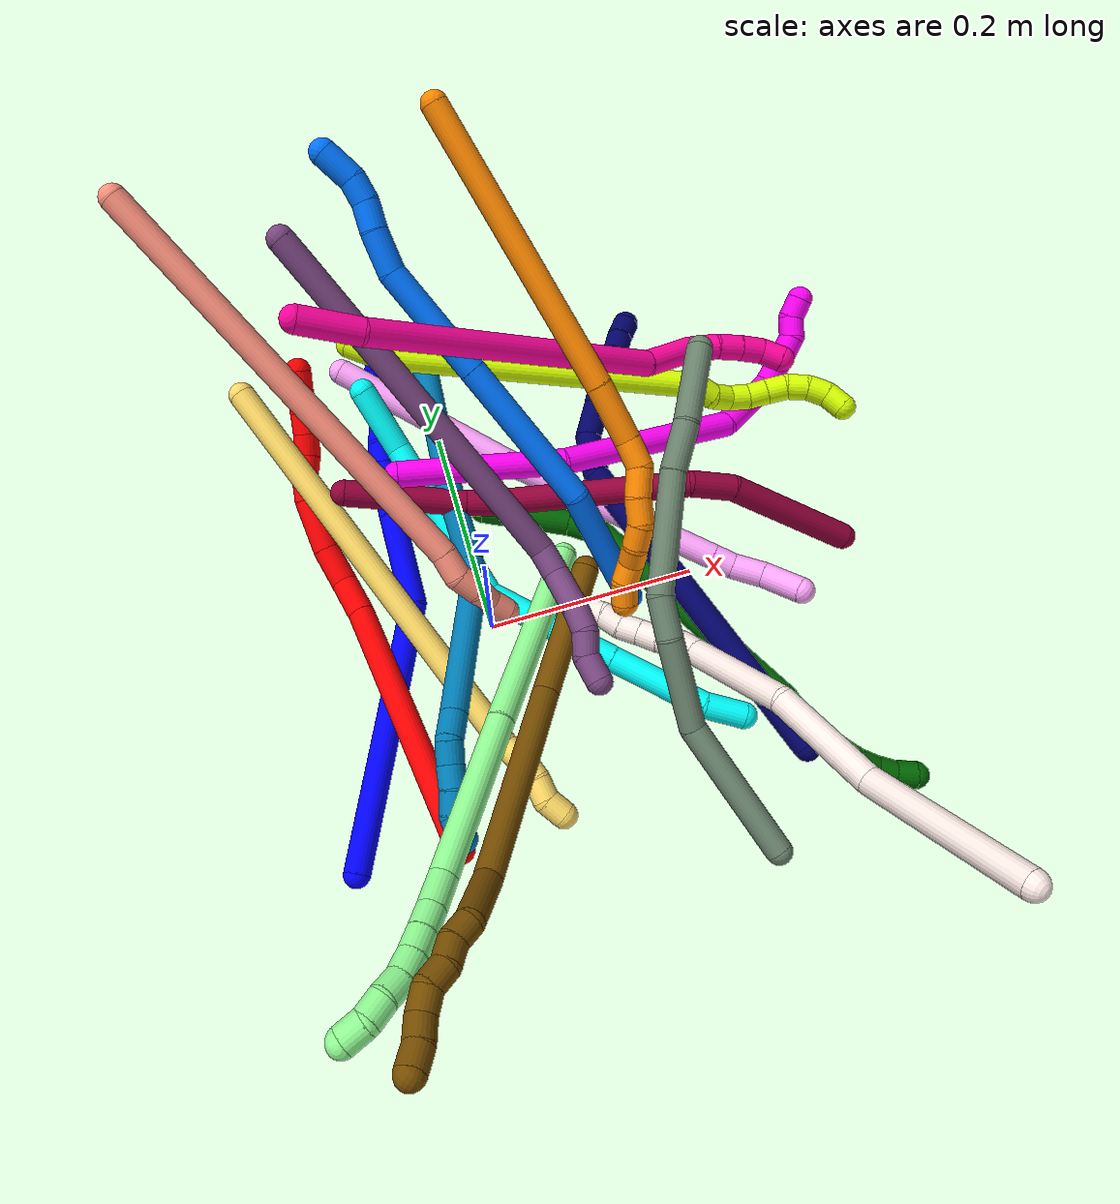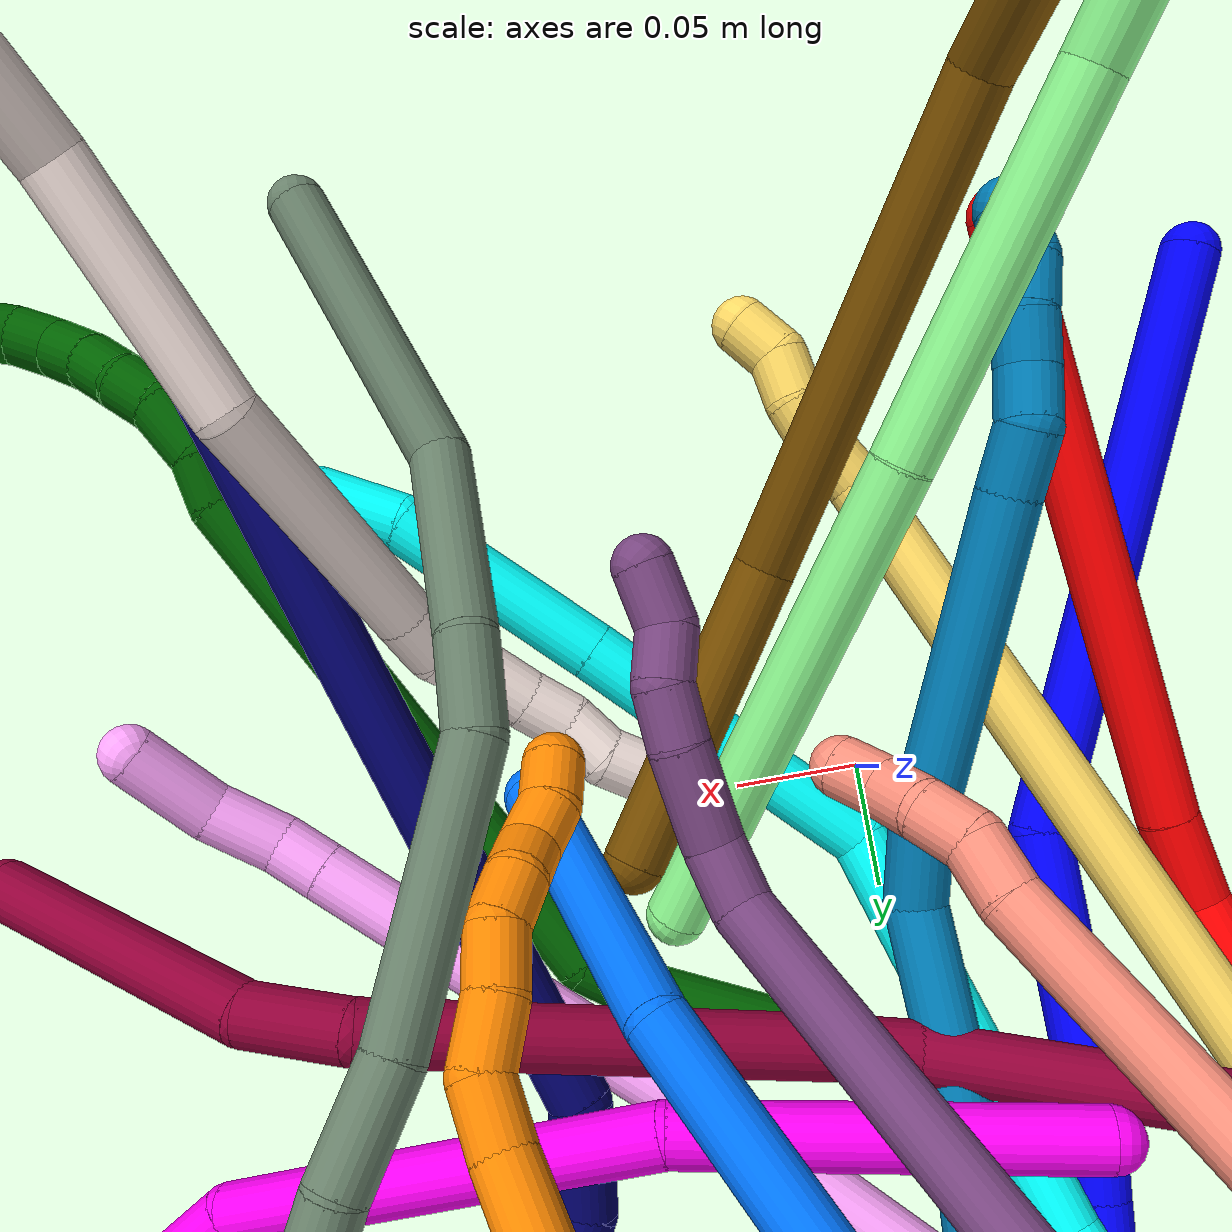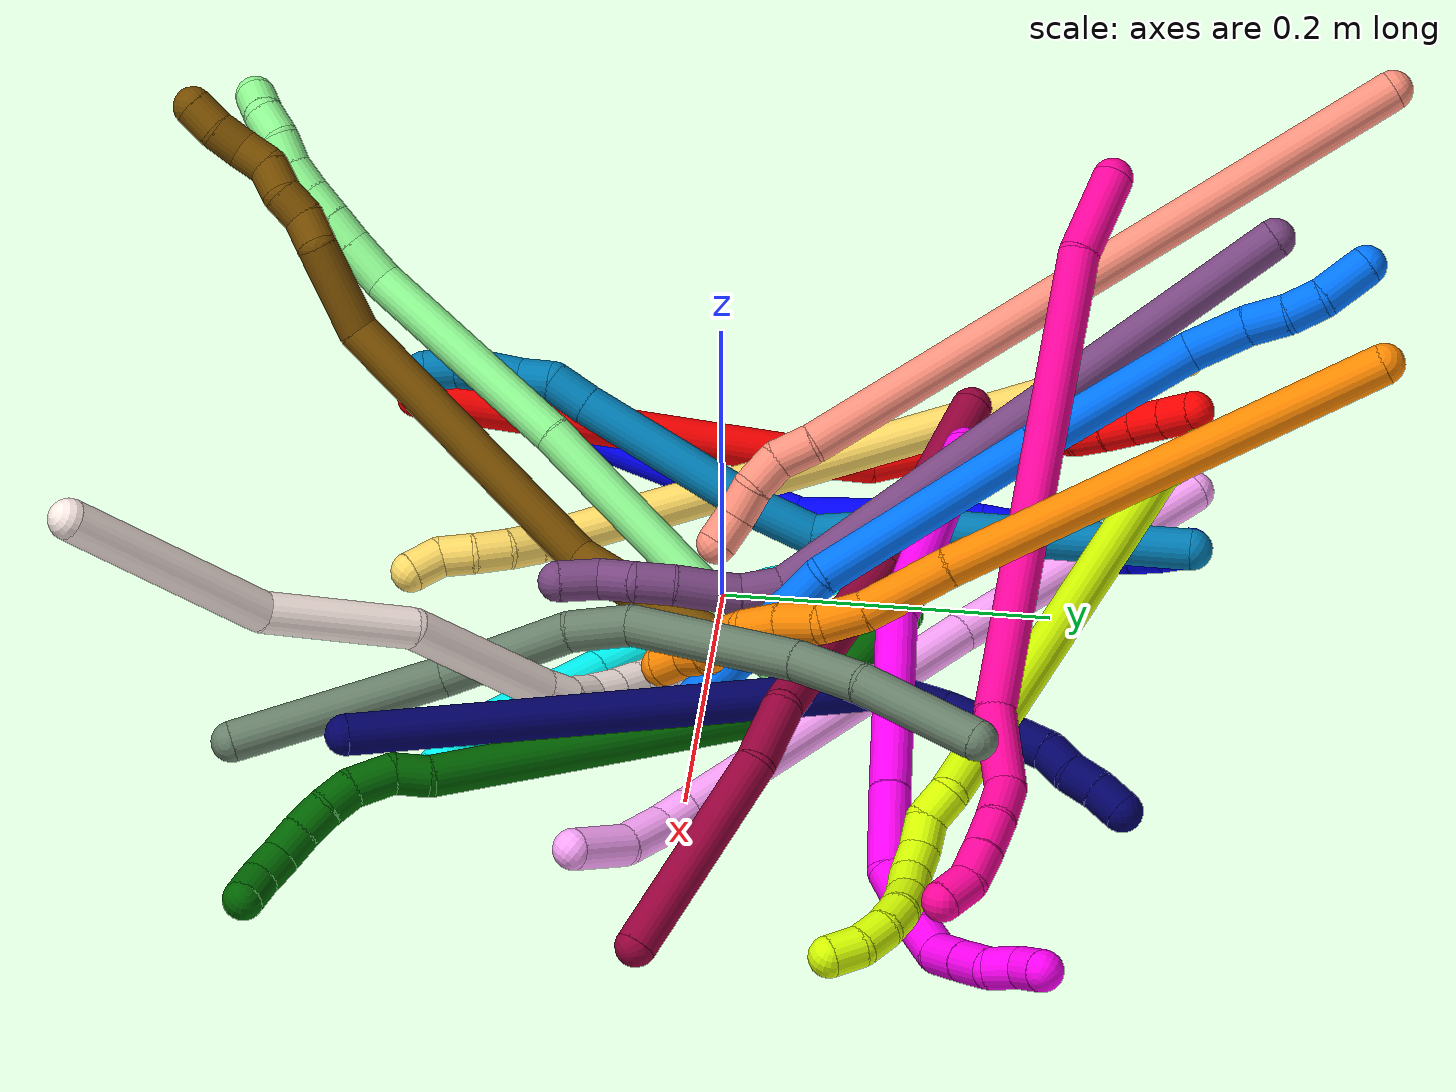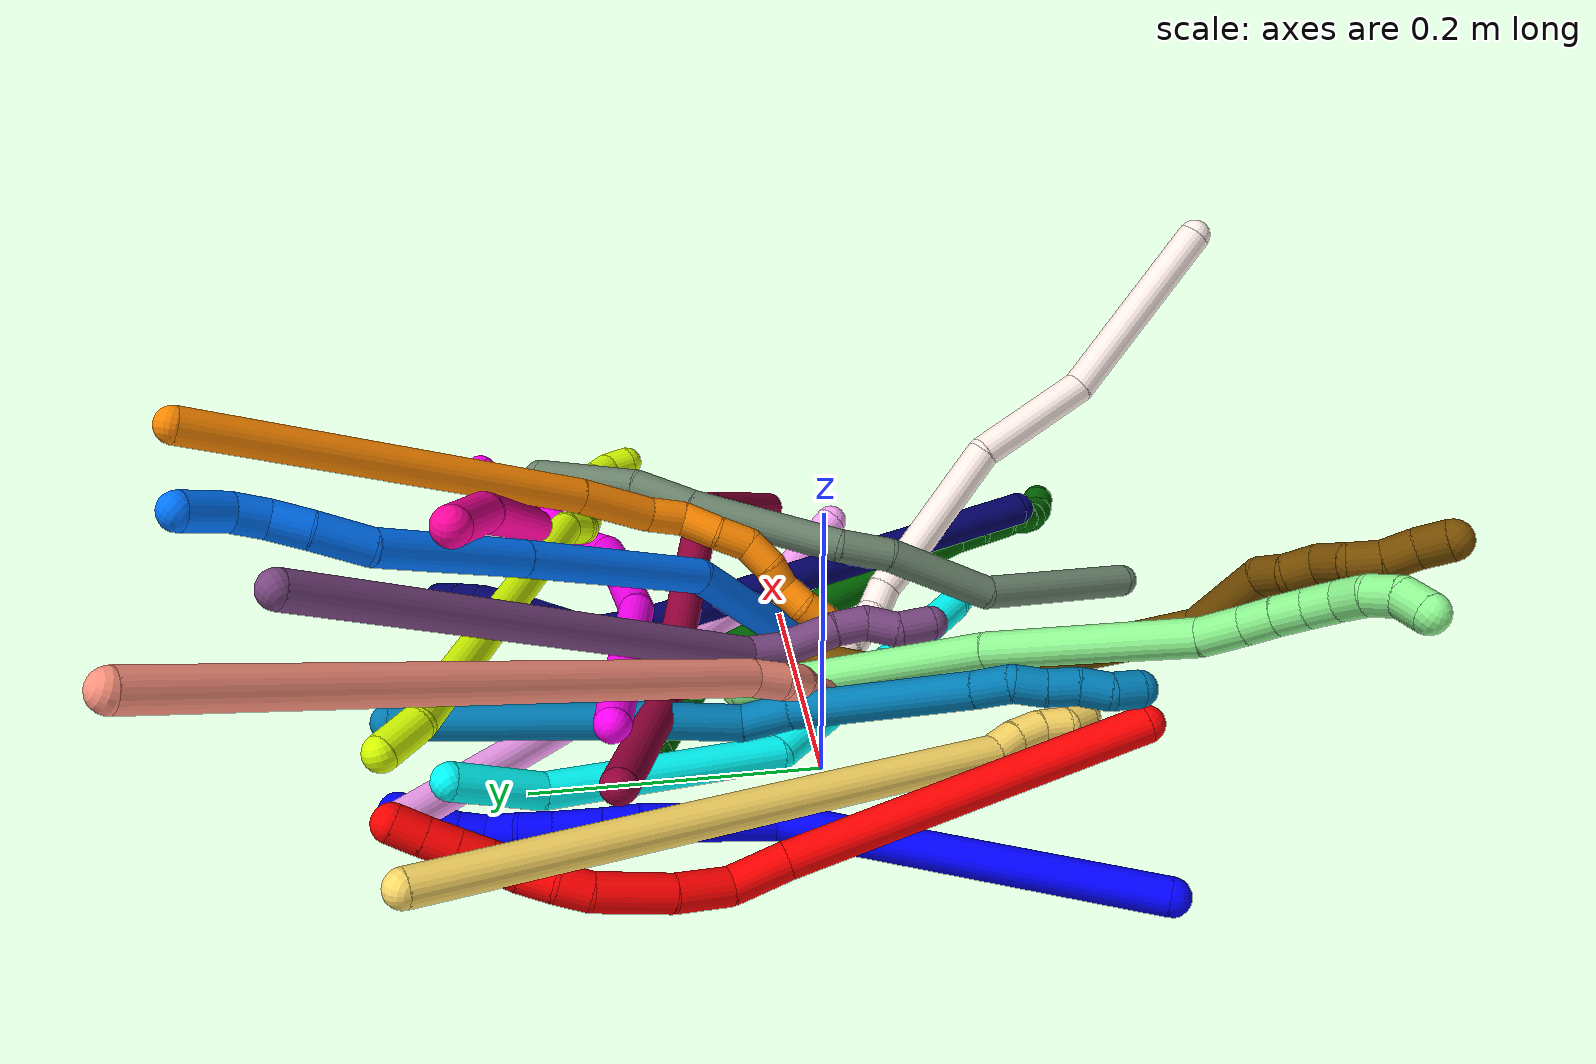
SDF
<sdf version="1.7">
 <world name="default">
  <plugin name="TubeGeneratorPlugin" filename="libtube_generator_plugin.so"/>
  <model name="photoneo_s_sensor">
   <static>1</static>
   <pose>0 0 2 1.57079 1.57079 3.14159</pose>
   <link name="link">
    <inertial><mass>0.1</mass></inertial>
    <sensor name="sensor" type="depth">
     <update_rate>30</update_rate>
     <camera>
      <horizontal_fov>1.22</horizontal_fov>
      <image><width>1920</width><height>1200</height><format>B8G8R8</format></image>
      <clip><near>0.1</near><far>4</far></clip>
      <depth_camera><output>points</output></depth_camera>
     </camera>
     <plugin name="camera_plugin" filename="libgazebo_ros_depth_camera.so">
      <baseline>0.2</baseline>
      <alwaysOn>1</alwaysOn>
      <updateRate>0.0</updateRate>
      <cameraName>camera_ir</cameraName>
      <imageTopicName>/camera/color/image_raw</imageTopicName>
      <cameraInfoTopicName>/camera/color/camera_info</cameraInfoTopicName>
      <depthImageTopicName>/camera/depth/image_raw</depthImageTopicName>
      <depthImageCameraInfoTopicName>/camera/depth/camera_info</depthImageCameraInfoTopicName>
      <pointCloudTopicName>/camera/depth/points</pointCloudTopicName>
      <frameName>fr_optical</frameName>
      <pointCloudCutoff>0.1</pointCloudCutoff>
      <pointCloudCutoffMax>2.0</pointCloudCutoffMax>
      <distortionK1>0</distortionK1>
      <distortionK2>0</distortionK2>
      <distortionK3>0</distortionK3>
      <distortionT1>0</distortionT1>
      <distortionT2>0</distortionT2>
      <CxPrime>0</CxPrime>
      <Cx>0</Cx>
      <Cy>0</Cy>
      <focalLength>0</focalLength>
      <hackBaseline>0</hackBaseline>
     </plugin>
    </sensor>
   </link>
  </model>
  <gravity>0 0 -9.8</gravity>
  <magnetic_field>6e-06 2.3e-05 -4.2e-05</magnetic_field>
  <atmosphere type="adiabatic"/>
  <physics name="default_physics" default="0" type="ode">
   <max_step_size>0.003</max_step_size>
   <real_time_factor>1</real_time_factor>
   <real_time_update_rate>1000</real_time_update_rate>
   <max_contacts>10000</max_contacts>
   <ode>
    <solver>
     <type>quick</type>
     <iters>100</iters>
     <sor>1.3</sor>
     <use_dynamic_moi_rescaling>0</use_dynamic_moi_rescaling>
    </solver>
    <constraints>
     <contact_max_correcting_vel>0</contact_max_correcting_vel>
     <contact_surface_layer>0.001</contact_surface_layer>
     <cfm>0</cfm>
     <erp>0.2</erp>
    </constraints>
   </ode>
  </physics>
  <scene><ambient>0.4 0.4 0.4 1</ambient><background>0.7 0.7 0.7 1</background><shadows>0</shadows></scene>
  <audio><device>default</device></audio>
  <spherical_coordinates>
   <surface_model>EARTH_WGS84</surface_model>
   <latitude_deg>0</latitude_deg>
   <longitude_deg>0</longitude_deg>
   <elevation>0</elevation>
   <heading_deg>0</heading_deg>
  </spherical_coordinates>
  <model name="bin">
   <static>1</static>
   <link name="bottom">
    <collision name="collision-bottom">
     <pose>0 0 -0.01 0 -0 0</pose>
     <geometry><box><size>0.8 0.6 0.02</size></box></geometry>
     <surface>
      <friction><ode><mu>100</mu><mu2>100</mu2></ode></friction>
      <contact><collide_bitmask>65535</collide_bitmask></contact>
     </surface>
    </collision>
   </link>
   <link name="west_wall">
    <collision name="collision-west_wall">
     <pose>-0.41 0 0.1 0 -0 0</pose>
     <geometry><box><size>0.02 0.6 0.2</size></box></geometry>
     <surface>
      <friction><ode><mu>100</mu><mu2>100</mu2></ode></friction>
      <contact><collide_bitmask>65535</collide_bitmask></contact>
     </surface>
    </collision>
   </link>
   <link name="east_wall">
    <collision name="collision-east_wall">
     <pose>0.41 0 0.1 0 -0 0</pose>
     <geometry><box><size>0.02 0.6 0.2</size></box></geometry>
     <surface>
      <friction><ode><mu>100</mu><mu2>100</mu2></ode></friction>
      <contact><collide_bitmask>65535</collide_bitmask></contact>
     </surface>
    </collision>
   </link>
   <link name="south_wall">
    <collision name="collision-south_wall">
     <pose>0 -0.31 0.1 0 -0 0</pose>
     <geometry><box><size>0.8 0.02 0.2</size></box></geometry>
     <surface>
      <friction><ode><mu>100</mu><mu2>100</mu2></ode></friction>
      <contact><collide_bitmask>65535</collide_bitmask></contact>
     </surface>
    </collision>
   </link>
   <link name="north_wall">
    <collision name="collision-north_wall">
     <pose>0 0.31 0.1 0 -0 0</pose>
     <geometry><box><size>0.8 0.02 0.2</size></box></geometry>
     <surface>
      <friction><ode><mu>100</mu><mu2>100</mu2></ode></friction>
      <contact><collide_bitmask>65535</collide_bitmask></contact>
     </surface>
    </collision>
   </link>
  </model>
  <model name="1">
   <static>0</static>
   <link name="1">
    <collision name="collision-cylinder-e_1_1_4">
     <pose>0.029111 0.109974 0.054061 -1.1139 0.233233 -0.145641</pose>
     <geometry><cylinder><radius>0.0125</radius><length>0.251907</length></cylinder></geometry>
     <surface>
      <friction><ode><mu>1.16</mu><mu2>1.16</mu2><slip1>0</slip1><slip2>0</slip2></ode></friction>
      <contact><ode><kp>1e+06</kp><kd>1</kd><max_vel>0</max_vel><min_depth>0.001</min_depth></ode></contact>
     </surface>
    </collision>
    <visual name="visual-cylinder-e_1_1_4">
     <pose>0.029111 0.109974 0.054061 -1.1139 0.233233 -0.145641</pose>
     <geometry><cylinder><radius>0.0125</radius><length>0.251907</length></cylinder></geometry>
     <material><ambient>0 0 1 1</ambient></material>
    </visual>
    <collision name="collision-cylinder-e_2_4_5">
     <pose>0.056324 0.264243 0.113251 -1.45553 -0.042545 0.037904</pose>
     <geometry><cylinder><radius>0.0125</radius><length>0.089263</length></cylinder></geometry>
     <surface>
      <friction><ode><mu>1.16</mu><mu2>1.16</mu2><slip1>0</slip1><slip2>0</slip2></ode></friction>
      <contact><ode><kp>1e+06</kp><kd>1</kd><max_vel>0</max_vel><min_depth>0.001</min_depth></ode></contact>
     </surface>
    </collision>
    <visual name="visual-cylinder-e_2_4_5">
     <pose>0.056324 0.264243 0.113251 -1.45553 -0.042545 0.037904</pose>
     <geometry><cylinder><radius>0.0125</radius><length>0.089263</length></cylinder></geometry>
     <material><ambient>0 0 1 1</ambient></material>
    </visual>
    <collision name="collision-cylinder-e_3_5_6">
     <pose>0.055462 0.320183 0.119123 -1.50702 0.088629 -0.083155</pose>
     <geometry><cylinder><radius>0.0125</radius><length>0.02343</length></cylinder></geometry>
     <surface>
      <friction><ode><mu>1.16</mu><mu2>1.16</mu2><slip1>0</slip1><slip2>0</slip2></ode></friction>
      <contact><ode><kp>1e+06</kp><kd>1</kd><max_vel>0</max_vel><min_depth>0.001</min_depth></ode></contact>
     </surface>
    </collision>
    <visual name="visual-cylinder-e_3_5_6">
     <pose>0.055462 0.320183 0.119123 -1.50702 0.088629 -0.083155</pose>
     <geometry><cylinder><radius>0.0125</radius><length>0.02343</length></cylinder></geometry>
     <material><ambient>0 0 1 1</ambient></material>
    </visual>
    <collision name="collision-cylinder-e_4_6_7">
     <pose>0.058563 0.347696 0.121768 -1.45156 0.128402 -0.113971</pose>
     <geometry><cylinder><radius>0.0125</radius><length>0.032228</length></cylinder></geometry>
     <surface>
      <friction><ode><mu>1.16</mu><mu2>1.16</mu2><slip1>0</slip1><slip2>0</slip2></ode></friction>
      <contact><ode><kp>1e+06</kp><kd>1</kd><max_vel>0</max_vel><min_depth>0.001</min_depth></ode></contact>
     </surface>
    </collision>
    <visual name="visual-cylinder-e_4_6_7">
     <pose>0.058563 0.347696 0.121768 -1.45156 0.128402 -0.113971</pose>
     <geometry><cylinder><radius>0.0125</radius><length>0.032228</length></cylinder></geometry>
     <material><ambient>0 0 1 1</ambient></material>
    </visual>
    <collision name="collision-cylinder-e_5_7_8">
     <pose>0.061497 0.374428 0.125251 -1.42618 0.079157 -0.068473</pose>
     <geometry><cylinder><radius>0.0125</radius><length>0.022026</length></cylinder></geometry>
     <surface>
      <friction><ode><mu>1.16</mu><mu2>1.16</mu2><slip1>0</slip1><slip2>0</slip2></ode></friction>
      <contact><ode><kp>1e+06</kp><kd>1</kd><max_vel>0</max_vel><min_depth>0.001</min_depth></ode></contact>
     </surface>
    </collision>
    <visual name="visual-cylinder-e_5_7_8">
     <pose>0.061497 0.374428 0.125251 -1.42618 0.079157 -0.068473</pose>
     <geometry><cylinder><radius>0.0125</radius><length>0.022026</length></cylinder></geometry>
     <material><ambient>0 0 1 1</ambient></material>
    </visual>
    <collision name="collision-cylinder-e_6_8_9">
     <pose>0.065758 0.394836 0.128829 -1.3647 0.334612 -0.272752</pose>
     <geometry><cylinder><radius>0.0125</radius><length>0.020646</length></cylinder></geometry>
     <surface>
      <friction><ode><mu>1.16</mu><mu2>1.16</mu2><slip1>0</slip1><slip2>0</slip2></ode></friction>
      <contact><ode><kp>1e+06</kp><kd>1</kd><max_vel>0</max_vel><min_depth>0.001</min_depth></ode></contact>
     </surface>
    </collision>
    <visual name="visual-cylinder-e_6_8_9">
     <pose>0.065758 0.394836 0.128829 -1.3647 0.334612 -0.272752</pose>
     <geometry><cylinder><radius>0.0125</radius><length>0.020646</length></cylinder></geometry>
     <material><ambient>0 0 1 1</ambient></material>
    </visual>
    <collision name="collision-cylinder-e_7_9_10">
     <pose>0.068948 0.414186 0.133451 -1.30899 -0.019641 0.015071</pose>
     <geometry><cylinder><radius>0.0125</radius><length>0.020307</length></cylinder></geometry>
     <surface>
      <friction><ode><mu>1.16</mu><mu2>1.16</mu2><slip1>0</slip1><slip2>0</slip2></ode></friction>
      <contact><ode><kp>1e+06</kp><kd>1</kd><max_vel>0</max_vel><min_depth>0.001</min_depth></ode></contact>
     </surface>
    </collision>
    <visual name="visual-cylinder-e_7_9_10">
     <pose>0.068948 0.414186 0.133451 -1.30899 -0.019641 0.015071</pose>
     <geometry><cylinder><radius>0.0125</radius><length>0.020307</length></cylinder></geometry>
     <material><ambient>0 0 1 1</ambient></material>
    </visual>
    <collision name="collision-cylinder-e_8_10_11">
     <pose>0.067218 0.433355 0.139254 -1.24384 -0.153639 0.110236</pose>
     <geometry><cylinder><radius>0.0125</radius><length>0.02001</length></cylinder></geometry>
     <surface>
      <friction><ode><mu>1.16</mu><mu2>1.16</mu2><slip1>0</slip1><slip2>0</slip2></ode></friction>
      <contact><ode><kp>1e+06</kp><kd>1</kd><max_vel>0</max_vel><min_depth>0.001</min_depth></ode></contact>
     </surface>
    </collision>
    <visual name="visual-cylinder-e_8_10_11">
     <pose>0.067218 0.433355 0.139254 -1.24384 -0.153639 0.110236</pose>
     <geometry><cylinder><radius>0.0125</radius><length>0.02001</length></cylinder></geometry>
     <material><ambient>0 0 1 1</ambient></material>
    </visual>
    <collision name="collision-cylinder-e_9_11_2">
     <pose>0.06329 0.451406 0.146971 -1.08915 -0.239777 0.145667</pose>
     <geometry><cylinder><radius>0.0125</radius><length>0.020183</length></cylinder></geometry>
     <surface>
      <friction><ode><mu>1.16</mu><mu2>1.16</mu2><slip1>0</slip1><slip2>0</slip2></ode></friction>
      <contact><ode><kp>1e+06</kp><kd>1</kd><max_vel>0</max_vel><min_depth>0.001</min_depth></ode></contact>
     </surface>
    </collision>
    <visual name="visual-cylinder-e_9_11_2">
     <pose>0.06329 0.451406 0.146971 -1.08915 -0.239777 0.145667</pose>
     <geometry><cylinder><radius>0.0125</radius><length>0.020183</length></cylinder></geometry>
     <material><ambient>0 0 1 1</ambient></material>
    </visual>
    <collision name="collision-sphere-2">
     <pose>0.060894 0.460093 0.151512 0 -0 0</pose>
     <geometry><sphere><radius>0.0125</radius></sphere></geometry>
     <surface>
      <friction><ode><mu>1.16</mu><mu2>1.16</mu2><slip1>0</slip1><slip2>0</slip2></ode></friction>
      <contact><ode><kp>1e+06</kp><kd>1</kd><max_vel>0</max_vel><min_depth>0.001</min_depth></ode></contact>
     </surface>
    </collision>
    <visual name="visual-sphere-2">
     <pose>0.060894 0.460093 0.151512 0 -0 0</pose>
     <geometry><sphere><radius>0.0125</radius></sphere></geometry>
     <material><ambient>0 0 1 1</ambient></material>
    </visual>
    <collision name="collision-sphere-11">
     <pose>0.065687 0.442719 0.14243 0 -0 0</pose>
     <geometry><sphere><radius>0.0125</radius></sphere></geometry>
     <surface>
      <friction><ode><mu>1.16</mu><mu2>1.16</mu2><slip1>0</slip1><slip2>0</slip2></ode></friction>
      <contact><ode><kp>1e+06</kp><kd>1</kd><max_vel>0</max_vel><min_depth>0.001</min_depth></ode></contact>
     </surface>
    </collision>
    <visual name="visual-sphere-11">
     <pose>0.065687 0.442719 0.14243 0 -0 0</pose>
     <geometry><sphere><radius>0.0125</radius></sphere></geometry>
     <material><ambient>0 0 1 1</ambient></material>
    </visual>
    <collision name="collision-sphere-10">
     <pose>0.068749 0.423992 0.136079 0 -0 0</pose>
     <geometry><sphere><radius>0.0125</radius></sphere></geometry>
     <surface>
      <friction><ode><mu>1.16</mu><mu2>1.16</mu2><slip1>0</slip1><slip2>0</slip2></ode></friction>
      <contact><ode><kp>1e+06</kp><kd>1</kd><max_vel>0</max_vel><min_depth>0.001</min_depth></ode></contact>
     </surface>
    </collision>
    <visual name="visual-sphere-10">
     <pose>0.068749 0.423992 0.136079 0 -0 0</pose>
     <geometry><sphere><radius>0.0125</radius></sphere></geometry>
     <material><ambient>0 0 1 1</ambient></material>
    </visual>
    <collision name="collision-sphere-9">
     <pose>0.069148 0.40438 0.130824 0 -0 0</pose>
     <geometry><sphere><radius>0.0125</radius></sphere></geometry>
     <surface>
      <friction><ode><mu>1.16</mu><mu2>1.16</mu2><slip1>0</slip1><slip2>0</slip2></ode></friction>
      <contact><ode><kp>1e+06</kp><kd>1</kd><max_vel>0</max_vel><min_depth>0.001</min_depth></ode></contact>
     </surface>
    </collision>
    <visual name="visual-sphere-9">
     <pose>0.069148 0.40438 0.130824 0 -0 0</pose>
     <geometry><sphere><radius>0.0125</radius></sphere></geometry>
     <material><ambient>0 0 1 1</ambient></material>
    </visual>
    <collision name="collision-sphere-4">
     <pose>0.058222 0.219947 0.108122 0 -0 0</pose>
     <geometry><sphere><radius>0.0125</radius></sphere></geometry>
     <surface>
      <friction><ode><mu>1.16</mu><mu2>1.16</mu2><slip1>0</slip1><slip2>0</slip2></ode></friction>
      <contact><ode><kp>1e+06</kp><kd>1</kd><max_vel>0</max_vel><min_depth>0.001</min_depth></ode></contact>
     </surface>
    </collision>
    <visual name="visual-sphere-4">
     <pose>0.058222 0.219947 0.108122 0 -0 0</pose>
     <geometry><sphere><radius>0.0125</radius></sphere></geometry>
     <material><ambient>0 0 1 1</ambient></material>
    </visual>
    <collision name="collision-sphere-1">
     <geometry><sphere><radius>0.0125</radius></sphere></geometry>
     <surface>
      <friction><ode><mu>1.16</mu><mu2>1.16</mu2><slip1>0</slip1><slip2>0</slip2></ode></friction>
      <contact><ode><kp>1e+06</kp><kd>1</kd><max_vel>0</max_vel><min_depth>0.001</min_depth></ode></contact>
     </surface>
    </collision>
    <visual name="visual-sphere-1">
     <geometry><sphere><radius>0.0125</radius></sphere></geometry>
     <material><ambient>0 0 1 1</ambient></material>
    </visual>
    <collision name="collision-sphere-8">
     <pose>0.062368 0.385292 0.126833 0 -0 0</pose>
     <geometry><sphere><radius>0.0125</radius></sphere></geometry>
     <surface>
      <friction><ode><mu>1.16</mu><mu2>1.16</mu2><slip1>0</slip1><slip2>0</slip2></ode></friction>
      <contact><ode><kp>1e+06</kp><kd>1</kd><max_vel>0</max_vel><min_depth>0.001</min_depth></ode></contact>
     </surface>
    </collision>
    <visual name="visual-sphere-8">
     <pose>0.062368 0.385292 0.126833 0 -0 0</pose>
     <geometry><sphere><radius>0.0125</radius></sphere></geometry>
     <material><ambient>0 0 1 1</ambient></material>
    </visual>
    <collision name="collision-sphere-5">
     <pose>0.054425 0.308538 0.11838 0 -0 0</pose>
     <geometry><sphere><radius>0.0125</radius></sphere></geometry>
     <surface>
      <friction><ode><mu>1.16</mu><mu2>1.16</mu2><slip1>0</slip1><slip2>0</slip2></ode></friction>
      <contact><ode><kp>1e+06</kp><kd>1</kd><max_vel>0</max_vel><min_depth>0.001</min_depth></ode></contact>
     </surface>
    </collision>
    <visual name="visual-sphere-5">
     <pose>0.054425 0.308538 0.11838 0 -0 0</pose>
     <geometry><sphere><radius>0.0125</radius></sphere></geometry>
     <material><ambient>0 0 1 1</ambient></material>
    </visual>
    <collision name="collision-sphere-6">
     <pose>0.056499 0.331828 0.119867 0 -0 0</pose>
     <geometry><sphere><radius>0.0125</radius></sphere></geometry>
     <surface>
      <friction><ode><mu>1.16</mu><mu2>1.16</mu2><slip1>0</slip1><slip2>0</slip2></ode></friction>
      <contact><ode><kp>1e+06</kp><kd>1</kd><max_vel>0</max_vel><min_depth>0.001</min_depth></ode></contact>
     </surface>
    </collision>
    <visual name="visual-sphere-6">
     <pose>0.056499 0.331828 0.119867 0 -0 0</pose>
     <geometry><sphere><radius>0.0125</radius></sphere></geometry>
     <material><ambient>0 0 1 1</ambient></material>
    </visual>
    <collision name="collision-sphere-7">
     <pose>0.060626 0.363564 0.123669 0 -0 0</pose>
     <geometry><sphere><radius>0.0125</radius></sphere></geometry>
     <surface>
      <friction><ode><mu>1.16</mu><mu2>1.16</mu2><slip1>0</slip1><slip2>0</slip2></ode></friction>
      <contact><ode><kp>1e+06</kp><kd>1</kd><max_vel>0</max_vel><min_depth>0.001</min_depth></ode></contact>
     </surface>
    </collision>
    <visual name="visual-sphere-7">
     <pose>0.060626 0.363564 0.123669 0 -0 0</pose>
     <geometry><sphere><radius>0.0125</radius></sphere></geometry>
     <material><ambient>0 0 1 1</ambient></material>
    </visual>
    <inertial>
     <pose>0.044565 0.225179 0.088649 0 -0 0</pose>
     <mass>0.5</mass>
     <inertia>
      <ixx>0.001185</ixx>
      <ixy>0</ixy>
      <ixz>0</ixz>
      <iyy>0.000485</iyy>
      <iyz>0</iyz>
      <izz>-0.001544</izz>
     </inertia>
    </inertial>
   </link>
   <pose>-0.176173 -0.187347 0.014209 -0.011574 1.08673 0.049725</pose>
  </model>
  <model name="2">
   <static>0</static>
   <link name="2">
    <collision name="collision-cylinder-e_1_1_4">
     <pose>0.025242 0.085342 -0.085449 -2.35682 0.206047 -0.489631</pose>
     <geometry><cylinder><radius>0.0125</radius><length>0.246755</length></cylinder></geometry>
     <surface>
      <friction><ode><mu>1.16</mu><mu2>1.16</mu2><slip1>0</slip1><slip2>0</slip2></ode></friction>
      <contact><ode><kp>1e+06</kp><kd>1</kd><max_vel>0</max_vel><min_depth>0.001</min_depth></ode></contact>
     </surface>
    </collision>
    <visual name="visual-cylinder-e_1_1_4">
     <pose>0.025242 0.085342 -0.085449 -2.35682 0.206047 -0.489631</pose>
     <geometry><cylinder><radius>0.0125</radius><length>0.246755</length></cylinder></geometry>
     <material><ambient>1 0 0 1</ambient></material>
    </visual>
    <collision name="collision-cylinder-e_2_4_5">
     <pose>0.054332 0.182892 -0.185481 -2.4446 0.199623 -0.537905</pose>
     <geometry><cylinder><radius>0.0125</radius><length>0.038807</length></cylinder></geometry>
     <surface>
      <friction><ode><mu>1.16</mu><mu2>1.16</mu2><slip1>0</slip1><slip2>0</slip2></ode></friction>
      <contact><ode><kp>1e+06</kp><kd>1</kd><max_vel>0</max_vel><min_depth>0.001</min_depth></ode></contact>
     </surface>
    </collision>
    <visual name="visual-cylinder-e_2_4_5">
     <pose>0.054332 0.182892 -0.185481 -2.4446 0.199623 -0.537905</pose>
     <geometry><cylinder><radius>0.0125</radius><length>0.038807</length></cylinder></geometry>
     <material><ambient>1 0 0 1</ambient></material>
    </visual>
    <collision name="collision-cylinder-e_3_5_6">
     <pose>0.054674 0.207017 -0.213855 -2.42899 -0.190034 0.501356</pose>
     <geometry><cylinder><radius>0.0125</radius><length>0.03712</length></cylinder></geometry>
     <surface>
      <friction><ode><mu>1.16</mu><mu2>1.16</mu2><slip1>0</slip1><slip2>0</slip2></ode></friction>
      <contact><ode><kp>1e+06</kp><kd>1</kd><max_vel>0</max_vel><min_depth>0.001</min_depth></ode></contact>
     </surface>
    </collision>
    <visual name="visual-cylinder-e_3_5_6">
     <pose>0.054674 0.207017 -0.213855 -2.42899 -0.190034 0.501356</pose>
     <geometry><cylinder><radius>0.0125</radius><length>0.03712</length></cylinder></geometry>
     <material><ambient>1 0 0 1</ambient></material>
    </visual>
    <collision name="collision-cylinder-e_4_6_7">
     <pose>0.045078 0.237785 -0.243729 -2.2771 -0.240978 0.513307</pose>
     <geometry><cylinder><radius>0.0125</radius><length>0.051037</length></cylinder></geometry>
     <surface>
      <friction><ode><mu>1.16</mu><mu2>1.16</mu2><slip1>0</slip1><slip2>0</slip2></ode></friction>
      <contact><ode><kp>1e+06</kp><kd>1</kd><max_vel>0</max_vel><min_depth>0.001</min_depth></ode></contact>
     </surface>
    </collision>
    <visual name="visual-cylinder-e_4_6_7">
     <pose>0.045078 0.237785 -0.243729 -2.2771 -0.240978 0.513307</pose>
     <geometry><cylinder><radius>0.0125</radius><length>0.051037</length></cylinder></geometry>
     <material><ambient>1 0 0 1</ambient></material>
    </visual>
    <collision name="collision-cylinder-e_5_7_8">
     <pose>0.035779 0.26564 -0.264299 -2.03312 -0.308808 0.492708</pose>
     <geometry><cylinder><radius>0.0125</radius><length>0.021116</length></cylinder></geometry>
     <surface>
      <friction><ode><mu>1.16</mu><mu2>1.16</mu2><slip1>0</slip1><slip2>0</slip2></ode></friction>
      <contact><ode><kp>1e+06</kp><kd>1</kd><max_vel>0</max_vel><min_depth>0.001</min_depth></ode></contact>
     </surface>
    </collision>
    <visual name="visual-cylinder-e_5_7_8">
     <pose>0.035779 0.26564 -0.264299 -2.03312 -0.308808 0.492708</pose>
     <geometry><cylinder><radius>0.0125</radius><length>0.021116</length></cylinder></geometry>
     <material><ambient>1 0 0 1</ambient></material>
    </visual>
    <collision name="collision-cylinder-e_6_8_9">
     <pose>0.030678 0.285478 -0.271506 -1.81683 -0.167816 0.214846</pose>
     <geometry><cylinder><radius>0.0125</radius><length>0.022662</length></cylinder></geometry>
     <surface>
      <friction><ode><mu>1.16</mu><mu2>1.16</mu2><slip1>0</slip1><slip2>0</slip2></ode></friction>
      <contact><ode><kp>1e+06</kp><kd>1</kd><max_vel>0</max_vel><min_depth>0.001</min_depth></ode></contact>
     </surface>
    </collision>
    <visual name="visual-cylinder-e_6_8_9">
     <pose>0.030678 0.285478 -0.271506 -1.81683 -0.167816 0.214846</pose>
     <geometry><cylinder><radius>0.0125</radius><length>0.022662</length></cylinder></geometry>
     <material><ambient>1 0 0 1</ambient></material>
    </visual>
    <collision name="collision-cylinder-e_7_9_10">
     <pose>0.024411 0.305543 -0.277718 -1.9324 -0.417265 0.594689</pose>
     <geometry><cylinder><radius>0.0125</radius><length>0.021587</length></cylinder></geometry>
     <surface>
      <friction><ode><mu>1.16</mu><mu2>1.16</mu2><slip1>0</slip1><slip2>0</slip2></ode></friction>
      <contact><ode><kp>1e+06</kp><kd>1</kd><max_vel>0</max_vel><min_depth>0.001</min_depth></ode></contact>
     </surface>
    </collision>
    <visual name="visual-cylinder-e_7_9_10">
     <pose>0.024411 0.305543 -0.277718 -1.9324 -0.417265 0.594689</pose>
     <geometry><cylinder><radius>0.0125</radius><length>0.021587</length></cylinder></geometry>
     <material><ambient>1 0 0 1</ambient></material>
    </visual>
    <collision name="collision-cylinder-e_8_10_11">
     <pose>0.01585 0.322967 -0.285141 -2.01814 -0.431611 0.670356</pose>
     <geometry><cylinder><radius>0.0125</radius><length>0.020014</length></cylinder></geometry>
     <surface>
      <friction><ode><mu>1.16</mu><mu2>1.16</mu2><slip1>0</slip1><slip2>0</slip2></ode></friction>
      <contact><ode><kp>1e+06</kp><kd>1</kd><max_vel>0</max_vel><min_depth>0.001</min_depth></ode></contact>
     </surface>
    </collision>
    <visual name="visual-cylinder-e_8_10_11">
     <pose>0.01585 0.322967 -0.285141 -2.01814 -0.431611 0.670356</pose>
     <geometry><cylinder><radius>0.0125</radius><length>0.020014</length></cylinder></geometry>
     <material><ambient>1 0 0 1</ambient></material>
    </visual>
    <collision name="collision-cylinder-e_9_11_12">
     <pose>0.007455 0.339576 -0.292898 -1.99749 -0.427301 0.650038</pose>
     <geometry><cylinder><radius>0.0125</radius><length>0.020312</length></cylinder></geometry>
     <surface>
      <friction><ode><mu>1.16</mu><mu2>1.16</mu2><slip1>0</slip1><slip2>0</slip2></ode></friction>
      <contact><ode><kp>1e+06</kp><kd>1</kd><max_vel>0</max_vel><min_depth>0.001</min_depth></ode></contact>
     </surface>
    </collision>
    <visual name="visual-cylinder-e_9_11_12">
     <pose>0.007455 0.339576 -0.292898 -1.99749 -0.427301 0.650038</pose>
     <geometry><cylinder><radius>0.0125</radius><length>0.020312</length></cylinder></geometry>
     <material><ambient>1 0 0 1</ambient></material>
    </visual>
    <collision name="collision-cylinder-e_10_12_2">
     <pose>-0.001395 0.35641 -0.300405 -1.98303 -0.467746 0.698524</pose>
     <geometry><cylinder><radius>0.0125</radius><length>0.02059</length></cylinder></geometry>
     <surface>
      <friction><ode><mu>1.16</mu><mu2>1.16</mu2><slip1>0</slip1><slip2>0</slip2></ode></friction>
      <contact><ode><kp>1e+06</kp><kd>1</kd><max_vel>0</max_vel><min_depth>0.001</min_depth></ode></contact>
     </surface>
    </collision>
    <visual name="visual-cylinder-e_10_12_2">
     <pose>-0.001395 0.35641 -0.300405 -1.98303 -0.467746 0.698524</pose>
     <geometry><cylinder><radius>0.0125</radius><length>0.02059</length></cylinder></geometry>
     <material><ambient>1 0 0 1</ambient></material>
    </visual>
    <collision name="collision-sphere-2">
     <pose>-0.006037 0.364829 -0.304087 0 -0 0</pose>
     <geometry><sphere><radius>0.0125</radius></sphere></geometry>
     <surface>
      <friction><ode><mu>1.16</mu><mu2>1.16</mu2><slip1>0</slip1><slip2>0</slip2></ode></friction>
      <contact><ode><kp>1e+06</kp><kd>1</kd><max_vel>0</max_vel><min_depth>0.001</min_depth></ode></contact>
     </surface>
    </collision>
    <visual name="visual-sphere-2">
     <pose>-0.006037 0.364829 -0.304087 0 -0 0</pose>
     <geometry><sphere><radius>0.0125</radius></sphere></geometry>
     <material><ambient>1 0 0 1</ambient></material>
    </visual>
    <collision name="collision-sphere-12">
     <pose>0.003247 0.34799 -0.296723 0 -0 0</pose>
     <geometry><sphere><radius>0.0125</radius></sphere></geometry>
     <surface>
      <friction><ode><mu>1.16</mu><mu2>1.16</mu2><slip1>0</slip1><slip2>0</slip2></ode></friction>
      <contact><ode><kp>1e+06</kp><kd>1</kd><max_vel>0</max_vel><min_depth>0.001</min_depth></ode></contact>
     </surface>
    </collision>
    <visual name="visual-sphere-12">
     <pose>0.003247 0.34799 -0.296723 0 -0 0</pose>
     <geometry><sphere><radius>0.0125</radius></sphere></geometry>
     <material><ambient>1 0 0 1</ambient></material>
    </visual>
    <collision name="collision-sphere-11">
     <pose>0.011664 0.331162 -0.289073 0 -0 0</pose>
     <geometry><sphere><radius>0.0125</radius></sphere></geometry>
     <surface>
      <friction><ode><mu>1.16</mu><mu2>1.16</mu2><slip1>0</slip1><slip2>0</slip2></ode></friction>
      <contact><ode><kp>1e+06</kp><kd>1</kd><max_vel>0</max_vel><min_depth>0.001</min_depth></ode></contact>
     </surface>
    </collision>
    <visual name="visual-sphere-11">
     <pose>0.011664 0.331162 -0.289073 0 -0 0</pose>
     <geometry><sphere><radius>0.0125</radius></sphere></geometry>
     <material><ambient>1 0 0 1</ambient></material>
    </visual>
    <collision name="collision-sphere-10">
     <pose>0.020037 0.314772 -0.281209 0 -0 0</pose>
     <geometry><sphere><radius>0.0125</radius></sphere></geometry>
     <surface>
      <friction><ode><mu>1.16</mu><mu2>1.16</mu2><slip1>0</slip1><slip2>0</slip2></ode></friction>
      <contact><ode><kp>1e+06</kp><kd>1</kd><max_vel>0</max_vel><min_depth>0.001</min_depth></ode></contact>
     </surface>
    </collision>
    <visual name="visual-sphere-10">
     <pose>0.020037 0.314772 -0.281209 0 -0 0</pose>
     <geometry><sphere><radius>0.0125</radius></sphere></geometry>
     <material><ambient>1 0 0 1</ambient></material>
    </visual>
    <collision name="collision-sphere-9">
     <pose>0.028785 0.296314 -0.274227 0 -0 0</pose>
     <geometry><sphere><radius>0.0125</radius></sphere></geometry>
     <surface>
      <friction><ode><mu>1.16</mu><mu2>1.16</mu2><slip1>0</slip1><slip2>0</slip2></ode></friction>
      <contact><ode><kp>1e+06</kp><kd>1</kd><max_vel>0</max_vel><min_depth>0.001</min_depth></ode></contact>
     </surface>
    </collision>
    <visual name="visual-sphere-9">
     <pose>0.028785 0.296314 -0.274227 0 -0 0</pose>
     <geometry><sphere><radius>0.0125</radius></sphere></geometry>
     <material><ambient>1 0 0 1</ambient></material>
    </visual>
    <collision name="collision-sphere-4">
     <pose>0.050484 0.170684 -0.170899 0 -0 0</pose>
     <geometry><sphere><radius>0.0125</radius></sphere></geometry>
     <surface>
      <friction><ode><mu>1.16</mu><mu2>1.16</mu2><slip1>0</slip1><slip2>0</slip2></ode></friction>
      <contact><ode><kp>1e+06</kp><kd>1</kd><max_vel>0</max_vel><min_depth>0.001</min_depth></ode></contact>
     </surface>
    </collision>
    <visual name="visual-sphere-4">
     <pose>0.050484 0.170684 -0.170899 0 -0 0</pose>
     <geometry><sphere><radius>0.0125</radius></sphere></geometry>
     <material><ambient>1 0 0 1</ambient></material>
    </visual>
    <collision name="collision-sphere-1">
     <geometry><sphere><radius>0.0125</radius></sphere></geometry>
     <surface>
      <friction><ode><mu>1.16</mu><mu2>1.16</mu2><slip1>0</slip1><slip2>0</slip2></ode></friction>
      <contact><ode><kp>1e+06</kp><kd>1</kd><max_vel>0</max_vel><min_depth>0.001</min_depth></ode></contact>
     </surface>
    </collision>
    <visual name="visual-sphere-1">
     <geometry><sphere><radius>0.0125</radius></sphere></geometry>
     <material><ambient>1 0 0 1</ambient></material>
    </visual>
    <collision name="collision-sphere-8">
     <pose>0.03257 0.274643 -0.268785 0 -0 0</pose>
     <geometry><sphere><radius>0.0125</radius></sphere></geometry>
     <surface>
      <friction><ode><mu>1.16</mu><mu2>1.16</mu2><slip1>0</slip1><slip2>0</slip2></ode></friction>
      <contact><ode><kp>1e+06</kp><kd>1</kd><max_vel>0</max_vel><min_depth>0.001</min_depth></ode></contact>
     </surface>
    </collision>
    <visual name="visual-sphere-8">
     <pose>0.03257 0.274643 -0.268785 0 -0 0</pose>
     <geometry><sphere><radius>0.0125</radius></sphere></geometry>
     <material><ambient>1 0 0 1</ambient></material>
    </visual>
    <collision name="collision-sphere-5">
     <pose>0.05818 0.1951 -0.200064 0 -0 0</pose>
     <geometry><sphere><radius>0.0125</radius></sphere></geometry>
     <surface>
      <friction><ode><mu>1.16</mu><mu2>1.16</mu2><slip1>0</slip1><slip2>0</slip2></ode></friction>
      <contact><ode><kp>1e+06</kp><kd>1</kd><max_vel>0</max_vel><min_depth>0.001</min_depth></ode></contact>
     </surface>
    </collision>
    <visual name="visual-sphere-5">
     <pose>0.05818 0.1951 -0.200064 0 -0 0</pose>
     <geometry><sphere><radius>0.0125</radius></sphere></geometry>
     <material><ambient>1 0 0 1</ambient></material>
    </visual>
    <collision name="collision-sphere-6">
     <pose>0.051168 0.218933 -0.227646 0 -0 0</pose>
     <geometry><sphere><radius>0.0125</radius></sphere></geometry>
     <surface>
      <friction><ode><mu>1.16</mu><mu2>1.16</mu2><slip1>0</slip1><slip2>0</slip2></ode></friction>
      <contact><ode><kp>1e+06</kp><kd>1</kd><max_vel>0</max_vel><min_depth>0.001</min_depth></ode></contact>
     </surface>
    </collision>
    <visual name="visual-sphere-6">
     <pose>0.051168 0.218933 -0.227646 0 -0 0</pose>
     <geometry><sphere><radius>0.0125</radius></sphere></geometry>
     <material><ambient>1 0 0 1</ambient></material>
    </visual>
    <collision name="collision-sphere-7">
     <pose>0.038988 0.256638 -0.259813 0 -0 0</pose>
     <geometry><sphere><radius>0.0125</radius></sphere></geometry>
     <surface>
      <friction><ode><mu>1.16</mu><mu2>1.16</mu2><slip1>0</slip1><slip2>0</slip2></ode></friction>
      <contact><ode><kp>1e+06</kp><kd>1</kd><max_vel>0</max_vel><min_depth>0.001</min_depth></ode></contact>
     </surface>
    </collision>
    <visual name="visual-sphere-7">
     <pose>0.038988 0.256638 -0.259813 0 -0 0</pose>
     <geometry><sphere><radius>0.0125</radius></sphere></geometry>
     <material><ambient>1 0 0 1</ambient></material>
    </visual>
    <inertial>
     <pose>0.03017 0.174702 -0.168462 0 -0 0</pose>
     <mass>0.5</mass>
     <inertia>
      <ixx>0.000548</ixx>
      <ixy>0</ixy>
      <ixz>0</ixz>
      <iyy>-0.001259</iyy>
      <iyz>0</iyz>
      <izz>-0.001174</izz>
     </inertia>
    </inertial>
   </link>
   <pose>-0.080093 -0.196928 0.074109 0.582392 1.50781 -0.039478</pose>
  </model>
  <model name="3">
   <static>0</static>
   <link name="3">
    <collision name="collision-cylinder-e_1_1_4">
     <pose>0.010417 -0.029861 0.008599 1.29041 0.323461 0.244379</pose>
     <geometry><cylinder><radius>0.0125</radius><length>0.065548</length></cylinder></geometry>
     <surface>
      <friction><ode><mu>1.16</mu><mu2>1.16</mu2><slip1>0</slip1><slip2>0</slip2></ode></friction>
      <contact><ode><kp>1e+06</kp><kd>1</kd><max_vel>0</max_vel><min_depth>0.001</min_depth></ode></contact>
     </surface>
    </collision>
    <visual name="visual-cylinder-e_1_1_4">
     <pose>0.010417 -0.029861 0.008599 1.29041 0.323461 0.244379</pose>
     <geometry><cylinder><radius>0.0125</radius><length>0.065548</length></cylinder></geometry>
     <material><ambient>0.003922 1 0.996078 1</ambient></material>
    </visual>
    <collision name="collision-cylinder-e_2_4_5">
     <pose>0.071344 -0.125309 0.033295 1.33013 0.642172 0.510306</pose>
     <geometry><cylinder><radius>0.0125</radius><length>0.168665</length></cylinder></geometry>
     <surface>
      <friction><ode><mu>1.16</mu><mu2>1.16</mu2><slip1>0</slip1><slip2>0</slip2></ode></friction>
      <contact><ode><kp>1e+06</kp><kd>1</kd><max_vel>0</max_vel><min_depth>0.001</min_depth></ode></contact>
     </surface>
    </collision>
    <visual name="visual-cylinder-e_2_4_5">
     <pose>0.071344 -0.125309 0.033295 1.33013 0.642172 0.510306</pose>
     <geometry><cylinder><radius>0.0125</radius><length>0.168665</length></cylinder></geometry>
     <material><ambient>0.003922 1 0.996078 1</ambient></material>
    </visual>
    <collision name="collision-cylinder-e_3_5_6">
     <pose>0.157525 -0.242766 0.028025 1.96154 0.566366 0.819942</pose>
     <geometry><cylinder><radius>0.0125</radius><length>0.132959</length></cylinder></geometry>
     <surface>
      <friction><ode><mu>1.16</mu><mu2>1.16</mu2><slip1>0</slip1><slip2>0</slip2></ode></friction>
      <contact><ode><kp>1e+06</kp><kd>1</kd><max_vel>0</max_vel><min_depth>0.001</min_depth></ode></contact>
     </surface>
    </collision>
    <visual name="visual-cylinder-e_3_5_6">
     <pose>0.157525 -0.242766 0.028025 1.96154 0.566366 0.819942</pose>
     <geometry><cylinder><radius>0.0125</radius><length>0.132959</length></cylinder></geometry>
     <material><ambient>0.003922 1 0.996078 1</ambient></material>
    </visual>
    <collision name="collision-cylinder-e_4_6_7">
     <pose>0.218288 -0.331309 -0.009322 1.98174 0.560227 0.827607</pose>
     <geometry><cylinder><radius>0.0125</radius><length>0.094441</length></cylinder></geometry>
     <surface>
      <friction><ode><mu>1.16</mu><mu2>1.16</mu2><slip1>0</slip1><slip2>0</slip2></ode></friction>
      <contact><ode><kp>1e+06</kp><kd>1</kd><max_vel>0</max_vel><min_depth>0.001</min_depth></ode></contact>
     </surface>
    </collision>
    <visual name="visual-cylinder-e_4_6_7">
     <pose>0.218288 -0.331309 -0.009322 1.98174 0.560227 0.827607</pose>
     <geometry><cylinder><radius>0.0125</radius><length>0.094441</length></cylinder></geometry>
     <material><ambient>0.003922 1 0.996078 1</ambient></material>
    </visual>
    <collision name="collision-cylinder-e_5_7_2">
     <pose>0.248713 -0.383937 -0.034539 2.09554 0.281587 0.482063</pose>
     <geometry><cylinder><radius>0.0125</radius><length>0.038387</length></cylinder></geometry>
     <surface>
      <friction><ode><mu>1.16</mu><mu2>1.16</mu2><slip1>0</slip1><slip2>0</slip2></ode></friction>
      <contact><ode><kp>1e+06</kp><kd>1</kd><max_vel>0</max_vel><min_depth>0.001</min_depth></ode></contact>
     </surface>
    </collision>
    <visual name="visual-cylinder-e_5_7_2">
     <pose>0.248713 -0.383937 -0.034539 2.09554 0.281587 0.482063</pose>
     <geometry><cylinder><radius>0.0125</radius><length>0.038387</length></cylinder></geometry>
     <material><ambient>0.003922 1 0.996078 1</ambient></material>
    </visual>
    <collision name="collision-sphere-2">
     <pose>0.254047 -0.399894 -0.043776 0 -0 0</pose>
     <geometry><sphere><radius>0.0125</radius></sphere></geometry>
     <surface>
      <friction><ode><mu>1.16</mu><mu2>1.16</mu2><slip1>0</slip1><slip2>0</slip2></ode></friction>
      <contact><ode><kp>1e+06</kp><kd>1</kd><max_vel>0</max_vel><min_depth>0.001</min_depth></ode></contact>
     </surface>
    </collision>
    <visual name="visual-sphere-2">
     <pose>0.254047 -0.399894 -0.043776 0 -0 0</pose>
     <geometry><sphere><radius>0.0125</radius></sphere></geometry>
     <material><ambient>0.003922 1 0.996078 1</ambient></material>
    </visual>
    <collision name="collision-sphere-7">
     <pose>0.24338 -0.36798 -0.025302 0 -0 0</pose>
     <geometry><sphere><radius>0.0125</radius></sphere></geometry>
     <surface>
      <friction><ode><mu>1.16</mu><mu2>1.16</mu2><slip1>0</slip1><slip2>0</slip2></ode></friction>
      <contact><ode><kp>1e+06</kp><kd>1</kd><max_vel>0</max_vel><min_depth>0.001</min_depth></ode></contact>
     </surface>
    </collision>
    <visual name="visual-sphere-7">
     <pose>0.24338 -0.36798 -0.025302 0 -0 0</pose>
     <geometry><sphere><radius>0.0125</radius></sphere></geometry>
     <material><ambient>0.003922 1 0.996078 1</ambient></material>
    </visual>
    <collision name="collision-sphere-6">
     <pose>0.193196 -0.294637 0.006658 0 -0 0</pose>
     <geometry><sphere><radius>0.0125</radius></sphere></geometry>
     <surface>
      <friction><ode><mu>1.16</mu><mu2>1.16</mu2><slip1>0</slip1><slip2>0</slip2></ode></friction>
      <contact><ode><kp>1e+06</kp><kd>1</kd><max_vel>0</max_vel><min_depth>0.001</min_depth></ode></contact>
     </surface>
    </collision>
    <visual name="visual-sphere-6">
     <pose>0.193196 -0.294637 0.006658 0 -0 0</pose>
     <geometry><sphere><radius>0.0125</radius></sphere></geometry>
     <material><ambient>0.003922 1 0.996078 1</ambient></material>
    </visual>
    <collision name="collision-sphere-5">
     <pose>0.121854 -0.190895 0.049392 0 -0 0</pose>
     <geometry><sphere><radius>0.0125</radius></sphere></geometry>
     <surface>
      <friction><ode><mu>1.16</mu><mu2>1.16</mu2><slip1>0</slip1><slip2>0</slip2></ode></friction>
      <contact><ode><kp>1e+06</kp><kd>1</kd><max_vel>0</max_vel><min_depth>0.001</min_depth></ode></contact>
     </surface>
    </collision>
    <visual name="visual-sphere-5">
     <pose>0.121854 -0.190895 0.049392 0 -0 0</pose>
     <geometry><sphere><radius>0.0125</radius></sphere></geometry>
     <material><ambient>0.003922 1 0.996078 1</ambient></material>
    </visual>
    <collision name="collision-sphere-1">
     <geometry><sphere><radius>0.0125</radius></sphere></geometry>
     <surface>
      <friction><ode><mu>1.16</mu><mu2>1.16</mu2><slip1>0</slip1><slip2>0</slip2></ode></friction>
      <contact><ode><kp>1e+06</kp><kd>1</kd><max_vel>0</max_vel><min_depth>0.001</min_depth></ode></contact>
     </surface>
    </collision>
    <visual name="visual-sphere-1">
     <geometry><sphere><radius>0.0125</radius></sphere></geometry>
     <material><ambient>0.003922 1 0.996078 1</ambient></material>
    </visual>
    <collision name="collision-sphere-4">
     <pose>0.020834 -0.059722 0.017198 0 -0 0</pose>
     <geometry><sphere><radius>0.0125</radius></sphere></geometry>
     <surface>
      <friction><ode><mu>1.16</mu><mu2>1.16</mu2><slip1>0</slip1><slip2>0</slip2></ode></friction>
      <contact><ode><kp>1e+06</kp><kd>1</kd><max_vel>0</max_vel><min_depth>0.001</min_depth></ode></contact>
     </surface>
    </collision>
    <visual name="visual-sphere-4">
     <pose>0.020834 -0.059722 0.017198 0 -0 0</pose>
     <geometry><sphere><radius>0.0125</radius></sphere></geometry>
     <material><ambient>0.003922 1 0.996078 1</ambient></material>
    </visual>
    <inertial>
     <pose>0.127646 -0.202795 0.015399 0 -0 0</pose>
     <mass>0.5</mass>
     <inertia>
      <ixx>0.000829</ixx>
      <ixy>0</ixy>
      <ixz>0</ixz>
      <iyy>0.000541</iyy>
      <iyz>0</iyz>
      <izz>0.000155</izz>
     </inertia>
    </inertial>
   </link>
   <pose>-0.06038 0.245132 0.06252 2.12259 -0.77068 -1.53394</pose>
  </model>
  <model name="4">
   <static>0</static>
   <link name="4">
    <collision name="collision-cylinder-e_1_1_4">
     <pose>0.005216 -0.051742 -0.077474 2.55277 0.055925 0.183962</pose>
     <geometry><cylinder><radius>0.0125</radius><length>0.186618</length></cylinder></geometry>
     <surface>
      <friction><ode><mu>1.16</mu><mu2>1.16</mu2><slip1>0</slip1><slip2>0</slip2></ode></friction>
      <contact><ode><kp>1e+06</kp><kd>1</kd><max_vel>0</max_vel><min_depth>0.001</min_depth></ode></contact>
     </surface>
    </collision>
    <visual name="visual-cylinder-e_1_1_4">
     <pose>0.005216 -0.051742 -0.077474 2.55277 0.055925 0.183962</pose>
     <geometry><cylinder><radius>0.0125</radius><length>0.186618</length></cylinder></geometry>
     <material><ambient>1 0.65098 0.996078 1</ambient></material>
    </visual>
    <collision name="collision-cylinder-e_2_4_5">
     <pose>0.023002 -0.166875 -0.244556 2.52589 0.114026 0.355226</pose>
     <geometry><cylinder><radius>0.0125</radius><length>0.220964</length></cylinder></geometry>
     <surface>
      <friction><ode><mu>1.16</mu><mu2>1.16</mu2><slip1>0</slip1><slip2>0</slip2></ode></friction>
      <contact><ode><kp>1e+06</kp><kd>1</kd><max_vel>0</max_vel><min_depth>0.001</min_depth></ode></contact>
     </surface>
    </collision>
    <visual name="visual-cylinder-e_2_4_5">
     <pose>0.023002 -0.166875 -0.244556 2.52589 0.114026 0.355226</pose>
     <geometry><cylinder><radius>0.0125</radius><length>0.220964</length></cylinder></geometry>
     <material><ambient>1 0.65098 0.996078 1</ambient></material>
    </visual>
    <collision name="collision-cylinder-e_3_5_6">
     <pose>0.036766 -0.236284 -0.342882 2.53757 0.112207 0.356713</pose>
     <geometry><cylinder><radius>0.0125</radius><length>0.021318</length></cylinder></geometry>
     <surface>
      <friction><ode><mu>1.16</mu><mu2>1.16</mu2><slip1>0</slip1><slip2>0</slip2></ode></friction>
      <contact><ode><kp>1e+06</kp><kd>1</kd><max_vel>0</max_vel><min_depth>0.001</min_depth></ode></contact>
     </surface>
    </collision>
    <visual name="visual-cylinder-e_3_5_6">
     <pose>0.036766 -0.236284 -0.342882 2.53757 0.112207 0.356713</pose>
     <geometry><cylinder><radius>0.0125</radius><length>0.021318</length></cylinder></geometry>
     <material><ambient>1 0.65098 0.996078 1</ambient></material>
    </visual>
    <collision name="collision-cylinder-e_4_6_7">
     <pose>0.041237 -0.25345 -0.362059 2.32424 0.211225 0.480132</pose>
     <geometry><cylinder><radius>0.0125</radius><length>0.031271</length></cylinder></geometry>
     <surface>
      <friction><ode><mu>1.16</mu><mu2>1.16</mu2><slip1>0</slip1><slip2>0</slip2></ode></friction>
      <contact><ode><kp>1e+06</kp><kd>1</kd><max_vel>0</max_vel><min_depth>0.001</min_depth></ode></contact>
     </surface>
    </collision>
    <visual name="visual-cylinder-e_4_6_7">
     <pose>0.041237 -0.25345 -0.362059 2.32424 0.211225 0.480132</pose>
     <geometry><cylinder><radius>0.0125</radius><length>0.031271</length></cylinder></geometry>
     <material><ambient>1 0.65098 0.996078 1</ambient></material>
    </visual>
    <collision name="collision-cylinder-e_5_7_2">
     <pose>0.044659 -0.281973 -0.382252 2.08149 0.007193 0.012275</pose>
     <geometry><cylinder><radius>0.0125</radius><length>0.039829</length></cylinder></geometry>
     <surface>
      <friction><ode><mu>1.16</mu><mu2>1.16</mu2><slip1>0</slip1><slip2>0</slip2></ode></friction>
      <contact><ode><kp>1e+06</kp><kd>1</kd><max_vel>0</max_vel><min_depth>0.001</min_depth></ode></contact>
     </surface>
    </collision>
    <visual name="visual-cylinder-e_5_7_2">
     <pose>0.044659 -0.281973 -0.382252 2.08149 0.007193 0.012275</pose>
     <geometry><cylinder><radius>0.0125</radius><length>0.039829</length></cylinder></geometry>
     <material><ambient>1 0.65098 0.996078 1</ambient></material>
    </visual>
    <collision name="collision-sphere-2">
     <pose>0.044802 -0.299346 -0.391986 0 -0 0</pose>
     <geometry><sphere><radius>0.0125</radius></sphere></geometry>
     <surface>
      <friction><ode><mu>1.16</mu><mu2>1.16</mu2><slip1>0</slip1><slip2>0</slip2></ode></friction>
      <contact><ode><kp>1e+06</kp><kd>1</kd><max_vel>0</max_vel><min_depth>0.001</min_depth></ode></contact>
     </surface>
    </collision>
    <visual name="visual-sphere-2">
     <pose>0.044802 -0.299346 -0.391986 0 -0 0</pose>
     <geometry><sphere><radius>0.0125</radius></sphere></geometry>
     <material><ambient>1 0.65098 0.996078 1</ambient></material>
    </visual>
    <collision name="collision-sphere-7">
     <pose>0.044516 -0.264599 -0.372519 0 -0 0</pose>
     <geometry><sphere><radius>0.0125</radius></sphere></geometry>
     <surface>
      <friction><ode><mu>1.16</mu><mu2>1.16</mu2><slip1>0</slip1><slip2>0</slip2></ode></friction>
      <contact><ode><kp>1e+06</kp><kd>1</kd><max_vel>0</max_vel><min_depth>0.001</min_depth></ode></contact>
     </surface>
    </collision>
    <visual name="visual-sphere-7">
     <pose>0.044516 -0.264599 -0.372519 0 -0 0</pose>
     <geometry><sphere><radius>0.0125</radius></sphere></geometry>
     <material><ambient>1 0.65098 0.996078 1</ambient></material>
    </visual>
    <collision name="collision-sphere-6">
     <pose>0.037959 -0.2423 -0.3516 0 -0 0</pose>
     <geometry><sphere><radius>0.0125</radius></sphere></geometry>
     <surface>
      <friction><ode><mu>1.16</mu><mu2>1.16</mu2><slip1>0</slip1><slip2>0</slip2></ode></friction>
      <contact><ode><kp>1e+06</kp><kd>1</kd><max_vel>0</max_vel><min_depth>0.001</min_depth></ode></contact>
     </surface>
    </collision>
    <visual name="visual-sphere-6">
     <pose>0.037959 -0.2423 -0.3516 0 -0 0</pose>
     <geometry><sphere><radius>0.0125</radius></sphere></geometry>
     <material><ambient>1 0.65098 0.996078 1</ambient></material>
    </visual>
    <collision name="collision-sphere-5">
     <pose>0.035572 -0.230268 -0.334164 0 -0 0</pose>
     <geometry><sphere><radius>0.0125</radius></sphere></geometry>
     <surface>
      <friction><ode><mu>1.16</mu><mu2>1.16</mu2><slip1>0</slip1><slip2>0</slip2></ode></friction>
      <contact><ode><kp>1e+06</kp><kd>1</kd><max_vel>0</max_vel><min_depth>0.001</min_depth></ode></contact>
     </surface>
    </collision>
    <visual name="visual-sphere-5">
     <pose>0.035572 -0.230268 -0.334164 0 -0 0</pose>
     <geometry><sphere><radius>0.0125</radius></sphere></geometry>
     <material><ambient>1 0.65098 0.996078 1</ambient></material>
    </visual>
    <collision name="collision-sphere-1">
     <geometry><sphere><radius>0.0125</radius></sphere></geometry>
     <surface>
      <friction><ode><mu>1.16</mu><mu2>1.16</mu2><slip1>0</slip1><slip2>0</slip2></ode></friction>
      <contact><ode><kp>1e+06</kp><kd>1</kd><max_vel>0</max_vel><min_depth>0.001</min_depth></ode></contact>
     </surface>
    </collision>
    <visual name="visual-sphere-1">
     <geometry><sphere><radius>0.0125</radius></sphere></geometry>
     <material><ambient>1 0.65098 0.996078 1</ambient></material>
    </visual>
    <collision name="collision-sphere-4">
     <pose>0.010431 -0.103483 -0.154948 0 -0 0</pose>
     <geometry><sphere><radius>0.0125</radius></sphere></geometry>
     <surface>
      <friction><ode><mu>1.16</mu><mu2>1.16</mu2><slip1>0</slip1><slip2>0</slip2></ode></friction>
      <contact><ode><kp>1e+06</kp><kd>1</kd><max_vel>0</max_vel><min_depth>0.001</min_depth></ode></contact>
     </surface>
    </collision>
    <visual name="visual-sphere-4">
     <pose>0.010431 -0.103483 -0.154948 0 -0 0</pose>
     <geometry><sphere><radius>0.0125</radius></sphere></geometry>
     <material><ambient>1 0.65098 0.996078 1</ambient></material>
    </visual>
    <inertial>
     <pose>0.019816 -0.141445 -0.204705 0 -0 0</pose>
     <mass>0.5</mass>
     <inertia>
      <ixx>0.001816</ixx>
      <ixy>0</ixy>
      <ixz>0</ixz>
      <iyy>-0.000733</iyy>
      <iyz>0</iyz>
      <izz>0.000669</izz>
     </inertia>
    </inertial>
   </link>
   <pose>-0.075575 0.280285 0.045383 -0.888596 -0.017824 0.735788</pose>
  </model>
  <model name="5">
   <static>0</static>
   <link name="5">
    <collision name="collision-cylinder-e_1_1_4">
     <pose>0.147677 -0.131278 -0.06509 2.03109 0.7893 1.18254</pose>
     <geometry><cylinder><radius>0.0125</radius><length>0.416072</length></cylinder></geometry>
     <surface>
      <friction><ode><mu>1.16</mu><mu2>1.16</mu2><slip1>0</slip1><slip2>0</slip2></ode></friction>
      <contact><ode><kp>1e+06</kp><kd>1</kd><max_vel>0</max_vel><min_depth>0.001</min_depth></ode></contact>
     </surface>
    </collision>
    <visual name="visual-cylinder-e_1_1_4">
     <pose>0.147677 -0.131278 -0.06509 2.03109 0.7893 1.18254</pose>
     <geometry><cylinder><radius>0.0125</radius><length>0.416072</length></cylinder></geometry>
     <material><ambient>1 0.858824 0.4 1</ambient></material>
    </visual>
    <collision name="collision-cylinder-e_2_4_5">
     <pose>0.300762 -0.271548 -0.131965 1.76677 0.533029 0.642064</pose>
     <geometry><cylinder><radius>0.0125</radius><length>0.021288</length></cylinder></geometry>
     <surface>
      <friction><ode><mu>1.16</mu><mu2>1.16</mu2><slip1>0</slip1><slip2>0</slip2></ode></friction>
      <contact><ode><kp>1e+06</kp><kd>1</kd><max_vel>0</max_vel><min_depth>0.001</min_depth></ode></contact>
     </surface>
    </collision>
    <visual name="visual-cylinder-e_2_4_5">
     <pose>0.300762 -0.271548 -0.131965 1.76677 0.533029 0.642064</pose>
     <geometry><cylinder><radius>0.0125</radius><length>0.021288</length></cylinder></geometry>
     <material><ambient>1 0.858824 0.4 1</ambient></material>
    </visual>
    <collision name="collision-cylinder-e_3_5_6">
     <pose>0.312286 -0.288538 -0.137534 2.01273 0.604765 0.915585</pose>
     <geometry><cylinder><radius>0.0125</radius><length>0.021512</length></cylinder></geometry>
     <surface>
      <friction><ode><mu>1.16</mu><mu2>1.16</mu2><slip1>0</slip1><slip2>0</slip2></ode></friction>
      <contact><ode><kp>1e+06</kp><kd>1</kd><max_vel>0</max_vel><min_depth>0.001</min_depth></ode></contact>
     </surface>
    </collision>
    <visual name="visual-cylinder-e_3_5_6">
     <pose>0.312286 -0.288538 -0.137534 2.01273 0.604765 0.915585</pose>
     <geometry><cylinder><radius>0.0125</radius><length>0.021512</length></cylinder></geometry>
     <material><ambient>1 0.858824 0.4 1</ambient></material>
    </visual>
    <collision name="collision-cylinder-e_4_6_7">
     <pose>0.324845 -0.302442 -0.146715 2.31112 0.678011 1.34926</pose>
     <geometry><cylinder><radius>0.0125</radius><length>0.020546</length></cylinder></geometry>
     <surface>
      <friction><ode><mu>1.16</mu><mu2>1.16</mu2><slip1>0</slip1><slip2>0</slip2></ode></friction>
      <contact><ode><kp>1e+06</kp><kd>1</kd><max_vel>0</max_vel><min_depth>0.001</min_depth></ode></contact>
     </surface>
    </collision>
    <visual name="visual-cylinder-e_4_6_7">
     <pose>0.324845 -0.302442 -0.146715 2.31112 0.678011 1.34926</pose>
     <geometry><cylinder><radius>0.0125</radius><length>0.020546</length></cylinder></geometry>
     <material><ambient>1 0.858824 0.4 1</ambient></material>
    </visual>
    <collision name="collision-cylinder-e_5_7_2">
     <pose>0.338944 -0.315197 -0.152754 1.66421 0.838882 0.910636</pose>
     <geometry><cylinder><radius>0.0125</radius><length>0.020583</length></cylinder></geometry>
     <surface>
      <friction><ode><mu>1.16</mu><mu2>1.16</mu2><slip1>0</slip1><slip2>0</slip2></ode></friction>
      <contact><ode><kp>1e+06</kp><kd>1</kd><max_vel>0</max_vel><min_depth>0.001</min_depth></ode></contact>
     </surface>
    </collision>
    <visual name="visual-cylinder-e_5_7_2">
     <pose>0.338944 -0.315197 -0.152754 1.66421 0.838882 0.910636</pose>
     <geometry><cylinder><radius>0.0125</radius><length>0.020583</length></cylinder></geometry>
     <material><ambient>1 0.858824 0.4 1</ambient></material>
    </visual>
    <collision name="collision-sphere-2">
     <pose>0.3466 -0.322044 -0.153395 0 -0 0</pose>
     <geometry><sphere><radius>0.0125</radius></sphere></geometry>
     <surface>
      <friction><ode><mu>1.16</mu><mu2>1.16</mu2><slip1>0</slip1><slip2>0</slip2></ode></friction>
      <contact><ode><kp>1e+06</kp><kd>1</kd><max_vel>0</max_vel><min_depth>0.001</min_depth></ode></contact>
     </surface>
    </collision>
    <visual name="visual-sphere-2">
     <pose>0.3466 -0.322044 -0.153395 0 -0 0</pose>
     <geometry><sphere><radius>0.0125</radius></sphere></geometry>
     <material><ambient>1 0.858824 0.4 1</ambient></material>
    </visual>
    <collision name="collision-sphere-7">
     <pose>0.331288 -0.308349 -0.152112 0 -0 0</pose>
     <geometry><sphere><radius>0.0125</radius></sphere></geometry>
     <surface>
      <friction><ode><mu>1.16</mu><mu2>1.16</mu2><slip1>0</slip1><slip2>0</slip2></ode></friction>
      <contact><ode><kp>1e+06</kp><kd>1</kd><max_vel>0</max_vel><min_depth>0.001</min_depth></ode></contact>
     </surface>
    </collision>
    <visual name="visual-sphere-7">
     <pose>0.331288 -0.308349 -0.152112 0 -0 0</pose>
     <geometry><sphere><radius>0.0125</radius></sphere></geometry>
     <material><ambient>1 0.858824 0.4 1</ambient></material>
    </visual>
    <collision name="collision-sphere-6">
     <pose>0.318401 -0.296536 -0.141319 0 -0 0</pose>
     <geometry><sphere><radius>0.0125</radius></sphere></geometry>
     <surface>
      <friction><ode><mu>1.16</mu><mu2>1.16</mu2><slip1>0</slip1><slip2>0</slip2></ode></friction>
      <contact><ode><kp>1e+06</kp><kd>1</kd><max_vel>0</max_vel><min_depth>0.001</min_depth></ode></contact>
     </surface>
    </collision>
    <visual name="visual-sphere-6">
     <pose>0.318401 -0.296536 -0.141319 0 -0 0</pose>
     <geometry><sphere><radius>0.0125</radius></sphere></geometry>
     <material><ambient>1 0.858824 0.4 1</ambient></material>
    </visual>
    <collision name="collision-sphere-5">
     <pose>0.30617 -0.280539 -0.13375 0 -0 0</pose>
     <geometry><sphere><radius>0.0125</radius></sphere></geometry>
     <surface>
      <friction><ode><mu>1.16</mu><mu2>1.16</mu2><slip1>0</slip1><slip2>0</slip2></ode></friction>
      <contact><ode><kp>1e+06</kp><kd>1</kd><max_vel>0</max_vel><min_depth>0.001</min_depth></ode></contact>
     </surface>
    </collision>
    <visual name="visual-sphere-5">
     <pose>0.30617 -0.280539 -0.13375 0 -0 0</pose>
     <geometry><sphere><radius>0.0125</radius></sphere></geometry>
     <material><ambient>1 0.858824 0.4 1</ambient></material>
    </visual>
    <collision name="collision-sphere-1">
     <geometry><sphere><radius>0.0125</radius></sphere></geometry>
     <surface>
      <friction><ode><mu>1.16</mu><mu2>1.16</mu2><slip1>0</slip1><slip2>0</slip2></ode></friction>
      <contact><ode><kp>1e+06</kp><kd>1</kd><max_vel>0</max_vel><min_depth>0.001</min_depth></ode></contact>
     </surface>
    </collision>
    <visual name="visual-sphere-1">
     <geometry><sphere><radius>0.0125</radius></sphere></geometry>
     <material><ambient>1 0.858824 0.4 1</ambient></material>
    </visual>
    <collision name="collision-sphere-4">
     <pose>0.295353 -0.262556 -0.13018 0 -0 0</pose>
     <geometry><sphere><radius>0.0125</radius></sphere></geometry>
     <surface>
      <friction><ode><mu>1.16</mu><mu2>1.16</mu2><slip1>0</slip1><slip2>0</slip2></ode></friction>
      <contact><ode><kp>1e+06</kp><kd>1</kd><max_vel>0</max_vel><min_depth>0.001</min_depth></ode></contact>
     </surface>
    </collision>
    <visual name="visual-sphere-4">
     <pose>0.295353 -0.262556 -0.13018 0 -0 0</pose>
     <geometry><sphere><radius>0.0125</radius></sphere></geometry>
     <material><ambient>1 0.858824 0.4 1</ambient></material>
    </visual>
    <inertial>
     <pose>0.17643 -0.15862 -0.078017 0 -0 0</pose>
     <mass>0.5</mass>
     <inertia>
      <ixx>0.005562</ixx>
      <ixy>0</ixy>
      <ixz>0</ixz>
      <iyy>0.006435</iyy>
      <iyz>0</iyz>
      <izz>-0.000486</izz>
     </inertia>
    </inertial>
   </link>
   <pose>-0.172406 0.267454 0.075313 -1.77916 0.913 -1.01131</pose>
  </model>
  <model name="6">
   <static>0</static>
   <link name="6">
    <collision name="collision-cylinder-e_1_1_4">
     <pose>0.028912 -0.029695 0.010367 1.23491 0.74334 0.540035</pose>
     <geometry><cylinder><radius>0.0125</radius><length>0.085445</length></cylinder></geometry>
     <surface>
      <friction><ode><mu>1.16</mu><mu2>1.16</mu2><slip1>0</slip1><slip2>0</slip2></ode></friction>
      <contact><ode><kp>1e+06</kp><kd>1</kd><max_vel>0</max_vel><min_depth>0.001</min_depth></ode></contact>
     </surface>
    </collision>
    <visual name="visual-cylinder-e_1_1_4">
     <pose>0.028912 -0.029695 0.010367 1.23491 0.74334 0.540035</pose>
     <geometry><cylinder><radius>0.0125</radius><length>0.085445</length></cylinder></geometry>
     <material><ambient>0 0.392157 0.003922 1</ambient></material>
    </visual>
    <collision name="collision-cylinder-e_2_4_5">
     <pose>0.065459 -0.072611 0.025333 1.23605 0.499288 0.358627</pose>
     <geometry><cylinder><radius>0.0125</radius><length>0.031888</length></cylinder></geometry>
     <surface>
      <friction><ode><mu>1.16</mu><mu2>1.16</mu2><slip1>0</slip1><slip2>0</slip2></ode></friction>
      <contact><ode><kp>1e+06</kp><kd>1</kd><max_vel>0</max_vel><min_depth>0.001</min_depth></ode></contact>
     </surface>
    </collision>
    <visual name="visual-cylinder-e_2_4_5">
     <pose>0.065459 -0.072611 0.025333 1.23605 0.499288 0.358627</pose>
     <geometry><cylinder><radius>0.0125</radius><length>0.031888</length></cylinder></geometry>
     <material><ambient>0 0.392157 0.003922 1</ambient></material>
    </visual>
    <collision name="collision-cylinder-e_3_5_6">
     <pose>0.090828 -0.201267 0.036263 1.516 0.152217 0.144126</pose>
     <geometry><cylinder><radius>0.0125</radius><length>0.233922</length></cylinder></geometry>
     <surface>
      <friction><ode><mu>1.16</mu><mu2>1.16</mu2><slip1>0</slip1><slip2>0</slip2></ode></friction>
      <contact><ode><kp>1e+06</kp><kd>1</kd><max_vel>0</max_vel><min_depth>0.001</min_depth></ode></contact>
     </surface>
    </collision>
    <visual name="visual-cylinder-e_3_5_6">
     <pose>0.090828 -0.201267 0.036263 1.516 0.152217 0.144126</pose>
     <geometry><cylinder><radius>0.0125</radius><length>0.233922</length></cylinder></geometry>
     <material><ambient>0 0.392157 0.003922 1</ambient></material>
    </visual>
    <collision name="collision-cylinder-e_4_6_7">
     <pose>0.106775 -0.32728 0.04256 1.574 -0.167418 -0.167953</pose>
     <geometry><cylinder><radius>0.0125</radius><length>0.021457</length></cylinder></geometry>
     <surface>
      <friction><ode><mu>1.16</mu><mu2>1.16</mu2><slip1>0</slip1><slip2>0</slip2></ode></friction>
      <contact><ode><kp>1e+06</kp><kd>1</kd><max_vel>0</max_vel><min_depth>0.001</min_depth></ode></contact>
     </surface>
    </collision>
    <visual name="visual-cylinder-e_4_6_7">
     <pose>0.106775 -0.32728 0.04256 1.574 -0.167418 -0.167953</pose>
     <geometry><cylinder><radius>0.0125</radius><length>0.021457</length></cylinder></geometry>
     <material><ambient>0 0.392157 0.003922 1</ambient></material>
    </visual>
    <collision name="collision-cylinder-e_5_7_8">
     <pose>0.108468 -0.350918 0.041372 1.65896 0.259565 0.283214</pose>
     <geometry><cylinder><radius>0.0125</radius><length>0.027129</length></cylinder></geometry>
     <surface>
      <friction><ode><mu>1.16</mu><mu2>1.16</mu2><slip1>0</slip1><slip2>0</slip2></ode></friction>
      <contact><ode><kp>1e+06</kp><kd>1</kd><max_vel>0</max_vel><min_depth>0.001</min_depth></ode></contact>
     </surface>
    </collision>
    <visual name="visual-cylinder-e_5_7_8">
     <pose>0.108468 -0.350918 0.041372 1.65896 0.259565 0.283214</pose>
     <geometry><cylinder><radius>0.0125</radius><length>0.027129</length></cylinder></geometry>
     <material><ambient>0 0.392157 0.003922 1</ambient></material>
    </visual>
    <collision name="collision-cylinder-e_6_8_9">
     <pose>0.117432 -0.372316 0.039266 1.68441 0.578571 0.643849</pose>
     <geometry><cylinder><radius>0.0125</radius><length>0.020049</length></cylinder></geometry>
     <surface>
      <friction><ode><mu>1.16</mu><mu2>1.16</mu2><slip1>0</slip1><slip2>0</slip2></ode></friction>
      <contact><ode><kp>1e+06</kp><kd>1</kd><max_vel>0</max_vel><min_depth>0.001</min_depth></ode></contact>
     </surface>
    </collision>
    <visual name="visual-cylinder-e_6_8_9">
     <pose>0.117432 -0.372316 0.039266 1.68441 0.578571 0.643849</pose>
     <geometry><cylinder><radius>0.0125</radius><length>0.020049</length></cylinder></geometry>
     <material><ambient>0 0.392157 0.003922 1</ambient></material>
    </visual>
    <collision name="collision-cylinder-e_7_9_10">
     <pose>0.128812 -0.388331 0.035654 1.90445 0.627962 0.856045</pose>
     <geometry><cylinder><radius>0.0125</radius><length>0.020079</length></cylinder></geometry>
     <surface>
      <friction><ode><mu>1.16</mu><mu2>1.16</mu2><slip1>0</slip1><slip2>0</slip2></ode></friction>
      <contact><ode><kp>1e+06</kp><kd>1</kd><max_vel>0</max_vel><min_depth>0.001</min_depth></ode></contact>
     </surface>
    </collision>
    <visual name="visual-cylinder-e_7_9_10">
     <pose>0.128812 -0.388331 0.035654 1.90445 0.627962 0.856045</pose>
     <geometry><cylinder><radius>0.0125</radius><length>0.020079</length></cylinder></geometry>
     <material><ambient>0 0.392157 0.003922 1</ambient></material>
    </visual>
    <collision name="collision-cylinder-e_8_10_11">
     <pose>0.141558 -0.403118 0.031306 1.80373 0.752943 0.927438</pose>
     <geometry><cylinder><radius>0.0125</radius><length>0.020029</length></cylinder></geometry>
     <surface>
      <friction><ode><mu>1.16</mu><mu2>1.16</mu2><slip1>0</slip1><slip2>0</slip2></ode></friction>
      <contact><ode><kp>1e+06</kp><kd>1</kd><max_vel>0</max_vel><min_depth>0.001</min_depth></ode></contact>
     </surface>
    </collision>
    <visual name="visual-cylinder-e_8_10_11">
     <pose>0.141558 -0.403118 0.031306 1.80373 0.752943 0.927438</pose>
     <geometry><cylinder><radius>0.0125</radius><length>0.020029</length></cylinder></geometry>
     <material><ambient>0 0.392157 0.003922 1</ambient></material>
    </visual>
    <collision name="collision-cylinder-e_9_11_12">
     <pose>0.155327 -0.417439 0.029946 1.5255 0.764408 0.733559</pose>
     <geometry><cylinder><radius>0.0125</radius><length>0.02</length></cylinder></geometry>
     <surface>
      <friction><ode><mu>1.16</mu><mu2>1.16</mu2><slip1>0</slip1><slip2>0</slip2></ode></friction>
      <contact><ode><kp>1e+06</kp><kd>1</kd><max_vel>0</max_vel><min_depth>0.001</min_depth></ode></contact>
     </surface>
    </collision>
    <visual name="visual-cylinder-e_9_11_12">
     <pose>0.155327 -0.417439 0.029946 1.5255 0.764408 0.733559</pose>
     <geometry><cylinder><radius>0.0125</radius><length>0.02</length></cylinder></geometry>
     <material><ambient>0 0.392157 0.003922 1</ambient></material>
    </visual>
    <collision name="collision-cylinder-e_10_12_2">
     <pose>0.169655 -0.430792 0.032995 1.15378 0.834093 0.56137</pose>
     <geometry><cylinder><radius>0.0125</radius><length>0.020001</length></cylinder></geometry>
     <surface>
      <friction><ode><mu>1.16</mu><mu2>1.16</mu2><slip1>0</slip1><slip2>0</slip2></ode></friction>
      <contact><ode><kp>1e+06</kp><kd>1</kd><max_vel>0</max_vel><min_depth>0.001</min_depth></ode></contact>
     </surface>
    </collision>
    <visual name="visual-cylinder-e_10_12_2">
     <pose>0.169655 -0.430792 0.032995 1.15378 0.834093 0.56137</pose>
     <geometry><cylinder><radius>0.0125</radius><length>0.020001</length></cylinder></geometry>
     <material><ambient>0 0.392157 0.003922 1</ambient></material>
    </visual>
    <collision name="collision-sphere-2">
     <pose>0.177063 -0.436935 0.035716 0 -0 0</pose>
     <geometry><sphere><radius>0.0125</radius></sphere></geometry>
     <surface>
      <friction><ode><mu>1.16</mu><mu2>1.16</mu2><slip1>0</slip1><slip2>0</slip2></ode></friction>
      <contact><ode><kp>1e+06</kp><kd>1</kd><max_vel>0</max_vel><min_depth>0.001</min_depth></ode></contact>
     </surface>
    </collision>
    <visual name="visual-sphere-2">
     <pose>0.177063 -0.436935 0.035716 0 -0 0</pose>
     <geometry><sphere><radius>0.0125</radius></sphere></geometry>
     <material><ambient>0 0.392157 0.003922 1</ambient></material>
    </visual>
    <collision name="collision-sphere-12">
     <pose>0.162248 -0.424649 0.030273 0 -0 0</pose>
     <geometry><sphere><radius>0.0125</radius></sphere></geometry>
     <surface>
      <friction><ode><mu>1.16</mu><mu2>1.16</mu2><slip1>0</slip1><slip2>0</slip2></ode></friction>
      <contact><ode><kp>1e+06</kp><kd>1</kd><max_vel>0</max_vel><min_depth>0.001</min_depth></ode></contact>
     </surface>
    </collision>
    <visual name="visual-sphere-12">
     <pose>0.162248 -0.424649 0.030273 0 -0 0</pose>
     <geometry><sphere><radius>0.0125</radius></sphere></geometry>
     <material><ambient>0 0.392157 0.003922 1</ambient></material>
    </visual>
    <collision name="collision-sphere-11">
     <pose>0.148406 -0.410228 0.02962 0 -0 0</pose>
     <geometry><sphere><radius>0.0125</radius></sphere></geometry>
     <surface>
      <friction><ode><mu>1.16</mu><mu2>1.16</mu2><slip1>0</slip1><slip2>0</slip2></ode></friction>
      <contact><ode><kp>1e+06</kp><kd>1</kd><max_vel>0</max_vel><min_depth>0.001</min_depth></ode></contact>
     </surface>
    </collision>
    <visual name="visual-sphere-11">
     <pose>0.148406 -0.410228 0.02962 0 -0 0</pose>
     <geometry><sphere><radius>0.0125</radius></sphere></geometry>
     <material><ambient>0 0.392157 0.003922 1</ambient></material>
    </visual>
    <collision name="collision-sphere-10">
     <pose>0.13471 -0.396008 0.032993 0 -0 0</pose>
     <geometry><sphere><radius>0.0125</radius></sphere></geometry>
     <surface>
      <friction><ode><mu>1.16</mu><mu2>1.16</mu2><slip1>0</slip1><slip2>0</slip2></ode></friction>
      <contact><ode><kp>1e+06</kp><kd>1</kd><max_vel>0</max_vel><min_depth>0.001</min_depth></ode></contact>
     </surface>
    </collision>
    <visual name="visual-sphere-10">
     <pose>0.13471 -0.396008 0.032993 0 -0 0</pose>
     <geometry><sphere><radius>0.0125</radius></sphere></geometry>
     <material><ambient>0 0.392157 0.003922 1</ambient></material>
    </visual>
    <collision name="collision-sphere-9">
     <pose>0.122913 -0.380655 0.038315 0 -0 0</pose>
     <geometry><sphere><radius>0.0125</radius></sphere></geometry>
     <surface>
      <friction><ode><mu>1.16</mu><mu2>1.16</mu2><slip1>0</slip1><slip2>0</slip2></ode></friction>
      <contact><ode><kp>1e+06</kp><kd>1</kd><max_vel>0</max_vel><min_depth>0.001</min_depth></ode></contact>
     </surface>
    </collision>
    <visual name="visual-sphere-9">
     <pose>0.122913 -0.380655 0.038315 0 -0 0</pose>
     <geometry><sphere><radius>0.0125</radius></sphere></geometry>
     <material><ambient>0 0.392157 0.003922 1</ambient></material>
    </visual>
    <collision name="collision-sphere-4">
     <pose>0.057825 -0.05939 0.020734 0 -0 0</pose>
     <geometry><sphere><radius>0.0125</radius></sphere></geometry>
     <surface>
      <friction><ode><mu>1.16</mu><mu2>1.16</mu2><slip1>0</slip1><slip2>0</slip2></ode></friction>
      <contact><ode><kp>1e+06</kp><kd>1</kd><max_vel>0</max_vel><min_depth>0.001</min_depth></ode></contact>
     </surface>
    </collision>
    <visual name="visual-sphere-4">
     <pose>0.057825 -0.05939 0.020734 0 -0 0</pose>
     <geometry><sphere><radius>0.0125</radius></sphere></geometry>
     <material><ambient>0 0.392157 0.003922 1</ambient></material>
    </visual>
    <collision name="collision-sphere-1">
     <geometry><sphere><radius>0.0125</radius></sphere></geometry>
     <surface>
      <friction><ode><mu>1.16</mu><mu2>1.16</mu2><slip1>0</slip1><slip2>0</slip2></ode></friction>
      <contact><ode><kp>1e+06</kp><kd>1</kd><max_vel>0</max_vel><min_depth>0.001</min_depth></ode></contact>
     </surface>
    </collision>
    <visual name="visual-sphere-1">
     <geometry><sphere><radius>0.0125</radius></sphere></geometry>
     <material><ambient>0 0.392157 0.003922 1</ambient></material>
    </visual>
    <collision name="collision-sphere-8">
     <pose>0.11195 -0.363977 0.040218 0 -0 0</pose>
     <geometry><sphere><radius>0.0125</radius></sphere></geometry>
     <surface>
      <friction><ode><mu>1.16</mu><mu2>1.16</mu2><slip1>0</slip1><slip2>0</slip2></ode></friction>
      <contact><ode><kp>1e+06</kp><kd>1</kd><max_vel>0</max_vel><min_depth>0.001</min_depth></ode></contact>
     </surface>
    </collision>
    <visual name="visual-sphere-8">
     <pose>0.11195 -0.363977 0.040218 0 -0 0</pose>
     <geometry><sphere><radius>0.0125</radius></sphere></geometry>
     <material><ambient>0 0.392157 0.003922 1</ambient></material>
    </visual>
    <collision name="collision-sphere-5">
     <pose>0.073093 -0.085831 0.029931 0 -0 0</pose>
     <geometry><sphere><radius>0.0125</radius></sphere></geometry>
     <surface>
      <friction><ode><mu>1.16</mu><mu2>1.16</mu2><slip1>0</slip1><slip2>0</slip2></ode></friction>
      <contact><ode><kp>1e+06</kp><kd>1</kd><max_vel>0</max_vel><min_depth>0.001</min_depth></ode></contact>
     </surface>
    </collision>
    <visual name="visual-sphere-5">
     <pose>0.073093 -0.085831 0.029931 0 -0 0</pose>
     <geometry><sphere><radius>0.0125</radius></sphere></geometry>
     <material><ambient>0 0.392157 0.003922 1</ambient></material>
    </visual>
    <collision name="collision-sphere-6">
     <pose>0.108562 -0.316702 0.042594 0 -0 0</pose>
     <geometry><sphere><radius>0.0125</radius></sphere></geometry>
     <surface>
      <friction><ode><mu>1.16</mu><mu2>1.16</mu2><slip1>0</slip1><slip2>0</slip2></ode></friction>
      <contact><ode><kp>1e+06</kp><kd>1</kd><max_vel>0</max_vel><min_depth>0.001</min_depth></ode></contact>
     </surface>
    </collision>
    <visual name="visual-sphere-6">
     <pose>0.108562 -0.316702 0.042594 0 -0 0</pose>
     <geometry><sphere><radius>0.0125</radius></sphere></geometry>
     <material><ambient>0 0.392157 0.003922 1</ambient></material>
    </visual>
    <collision name="collision-sphere-7">
     <pose>0.104987 -0.337859 0.042526 0 -0 0</pose>
     <geometry><sphere><radius>0.0125</radius></sphere></geometry>
     <surface>
      <friction><ode><mu>1.16</mu><mu2>1.16</mu2><slip1>0</slip1><slip2>0</slip2></ode></friction>
      <contact><ode><kp>1e+06</kp><kd>1</kd><max_vel>0</max_vel><min_depth>0.001</min_depth></ode></contact>
     </surface>
    </collision>
    <visual name="visual-sphere-7">
     <pose>0.104987 -0.337859 0.042526 0 -0 0</pose>
     <geometry><sphere><radius>0.0125</radius></sphere></geometry>
     <material><ambient>0 0.392157 0.003922 1</ambient></material>
    </visual>
    <inertial>
     <pose>0.090628 -0.217555 0.031202 0 -0 0</pose>
     <mass>0.5</mass>
     <inertia>
      <ixx>0.001292</ixx>
      <ixy>0</ixy>
      <ixz>0</ixz>
      <iyy>0.000265</iyy>
      <iyz>0</iyz>
      <izz>0.000908</izz>
     </inertia>
    </inertial>
   </link>
   <pose>0.02257 0.112496 0.01225 -0.114021 0.447343 0.288063</pose>
  </model>
  <model name="7">
   <static>0</static>
   <link name="7">
    <collision name="collision-cylinder-e_1_1_4">
     <pose>-0.000559 0.007345 -0.159491 -3.09557 -0.003502 0.151885</pose>
     <geometry><cylinder><radius>0.0125</radius><length>0.319322</length></cylinder></geometry>
     <surface>
      <friction><ode><mu>1.16</mu><mu2>1.16</mu2><slip1>0</slip1><slip2>0</slip2></ode></friction>
      <contact><ode><kp>1e+06</kp><kd>1</kd><max_vel>0</max_vel><min_depth>0.001</min_depth></ode></contact>
     </surface>
    </collision>
    <visual name="visual-cylinder-e_1_1_4">
     <pose>-0.000559 0.007345 -0.159491 -3.09557 -0.003502 0.151885</pose>
     <geometry><cylinder><radius>0.0125</radius><length>0.319322</length></cylinder></geometry>
     <material><ambient>0.003922 0 0.403922 1</ambient></material>
    </visual>
    <collision name="collision-cylinder-e_2_4_5">
     <pose>-0.00826 0.022249 -0.338441 -2.77106 -0.329612 1.45163</pose>
     <geometry><cylinder><radius>0.0125</radius><length>0.044129</length></cylinder></geometry>
     <surface>
      <friction><ode><mu>1.16</mu><mu2>1.16</mu2><slip1>0</slip1><slip2>0</slip2></ode></friction>
      <contact><ode><kp>1e+06</kp><kd>1</kd><max_vel>0</max_vel><min_depth>0.001</min_depth></ode></contact>
     </surface>
    </collision>
    <visual name="visual-cylinder-e_2_4_5">
     <pose>-0.00826 0.022249 -0.338441 -2.77106 -0.329612 1.45163</pose>
     <geometry><cylinder><radius>0.0125</radius><length>0.044129</length></cylinder></geometry>
     <material><ambient>0.003922 0 0.403922 1</ambient></material>
    </visual>
    <collision name="collision-cylinder-e_3_5_6">
     <pose>-0.028273 0.034045 -0.368767 -2.76991 -0.834641 2.33945</pose>
     <geometry><cylinder><radius>0.0125</radius><length>0.034738</length></cylinder></geometry>
     <surface>
      <friction><ode><mu>1.16</mu><mu2>1.16</mu2><slip1>0</slip1><slip2>0</slip2></ode></friction>
      <contact><ode><kp>1e+06</kp><kd>1</kd><max_vel>0</max_vel><min_depth>0.001</min_depth></ode></contact>
     </surface>
    </collision>
    <visual name="visual-cylinder-e_3_5_6">
     <pose>-0.028273 0.034045 -0.368767 -2.76991 -0.834641 2.33945</pose>
     <geometry><cylinder><radius>0.0125</radius><length>0.034738</length></cylinder></geometry>
     <material><ambient>0.003922 0 0.403922 1</ambient></material>
    </visual>
    <collision name="collision-cylinder-e_4_6_7">
     <pose>-0.048484 0.039988 -0.38634 -2.89233 -0.814722 2.57645</pose>
     <geometry><cylinder><radius>0.0125</radius><length>0.020175</length></cylinder></geometry>
     <surface>
      <friction><ode><mu>1.16</mu><mu2>1.16</mu2><slip1>0</slip1><slip2>0</slip2></ode></friction>
      <contact><ode><kp>1e+06</kp><kd>1</kd><max_vel>0</max_vel><min_depth>0.001</min_depth></ode></contact>
     </surface>
    </collision>
    <visual name="visual-cylinder-e_4_6_7">
     <pose>-0.048484 0.039988 -0.38634 -2.89233 -0.814722 2.57645</pose>
     <geometry><cylinder><radius>0.0125</radius><length>0.020175</length></cylinder></geometry>
     <material><ambient>0.003922 0 0.403922 1</ambient></material>
    </visual>
    <collision name="collision-cylinder-e_5_7_8">
     <pose>-0.063147 0.044737 -0.399657 -2.71025 -0.788656 2.17239</pose>
     <geometry><cylinder><radius>0.0125</radius><length>0.020649</length></cylinder></geometry>
     <surface>
      <friction><ode><mu>1.16</mu><mu2>1.16</mu2><slip1>0</slip1><slip2>0</slip2></ode></friction>
      <contact><ode><kp>1e+06</kp><kd>1</kd><max_vel>0</max_vel><min_depth>0.001</min_depth></ode></contact>
     </surface>
    </collision>
    <visual name="visual-cylinder-e_5_7_8">
     <pose>-0.063147 0.044737 -0.399657 -2.71025 -0.788656 2.17239</pose>
     <geometry><cylinder><radius>0.0125</radius><length>0.020649</length></cylinder></geometry>
     <material><ambient>0.003922 0 0.403922 1</ambient></material>
    </visual>
    <collision name="collision-cylinder-e_6_8_9">
     <pose>-0.078093 0.053043 -0.410633 -2.26324 -0.839534 1.51955</pose>
     <geometry><cylinder><radius>0.0125</radius><length>0.020481</length></cylinder></geometry>
     <surface>
      <friction><ode><mu>1.16</mu><mu2>1.16</mu2><slip1>0</slip1><slip2>0</slip2></ode></friction>
      <contact><ode><kp>1e+06</kp><kd>1</kd><max_vel>0</max_vel><min_depth>0.001</min_depth></ode></contact>
     </surface>
    </collision>
    <visual name="visual-cylinder-e_6_8_9">
     <pose>-0.078093 0.053043 -0.410633 -2.26324 -0.839534 1.51955</pose>
     <geometry><cylinder><radius>0.0125</radius><length>0.020481</length></cylinder></geometry>
     <material><ambient>0.003922 0 0.403922 1</ambient></material>
    </visual>
    <collision name="collision-cylinder-e_7_9_10">
     <pose>-0.092051 0.062962 -0.421445 -2.51606 -0.672778 1.64889</pose>
     <geometry><cylinder><radius>0.0125</radius><length>0.020332</length></cylinder></geometry>
     <surface>
      <friction><ode><mu>1.16</mu><mu2>1.16</mu2><slip1>0</slip1><slip2>0</slip2></ode></friction>
      <contact><ode><kp>1e+06</kp><kd>1</kd><max_vel>0</max_vel><min_depth>0.001</min_depth></ode></contact>
     </surface>
    </collision>
    <visual name="visual-cylinder-e_7_9_10">
     <pose>-0.092051 0.062962 -0.421445 -2.51606 -0.672778 1.64889</pose>
     <geometry><cylinder><radius>0.0125</radius><length>0.020332</length></cylinder></geometry>
     <material><ambient>0.003922 0 0.403922 1</ambient></material>
    </visual>
    <collision name="collision-cylinder-e_8_10_2">
     <pose>-0.104663 0.073406 -0.433261 -2.31883 -0.671627 1.34952</pose>
     <geometry><cylinder><radius>0.0125</radius><length>0.020175</length></cylinder></geometry>
     <surface>
      <friction><ode><mu>1.16</mu><mu2>1.16</mu2><slip1>0</slip1><slip2>0</slip2></ode></friction>
      <contact><ode><kp>1e+06</kp><kd>1</kd><max_vel>0</max_vel><min_depth>0.001</min_depth></ode></contact>
     </surface>
    </collision>
    <visual name="visual-cylinder-e_8_10_2">
     <pose>-0.104663 0.073406 -0.433261 -2.31883 -0.671627 1.34952</pose>
     <geometry><cylinder><radius>0.0125</radius><length>0.020175</length></cylinder></geometry>
     <material><ambient>0.003922 0 0.403922 1</ambient></material>
    </visual>
    <collision name="collision-sphere-2">
     <pose>-0.11094 0.079194 -0.438632 0 -0 0</pose>
     <geometry><sphere><radius>0.0125</radius></sphere></geometry>
     <surface>
      <friction><ode><mu>1.16</mu><mu2>1.16</mu2><slip1>0</slip1><slip2>0</slip2></ode></friction>
      <contact><ode><kp>1e+06</kp><kd>1</kd><max_vel>0</max_vel><min_depth>0.001</min_depth></ode></contact>
     </surface>
    </collision>
    <visual name="visual-sphere-2">
     <pose>-0.11094 0.079194 -0.438632 0 -0 0</pose>
     <geometry><sphere><radius>0.0125</radius></sphere></geometry>
     <material><ambient>0.003922 0 0.403922 1</ambient></material>
    </visual>
    <collision name="collision-sphere-10">
     <pose>-0.098386 0.067618 -0.42789 0 -0 0</pose>
     <geometry><sphere><radius>0.0125</radius></sphere></geometry>
     <surface>
      <friction><ode><mu>1.16</mu><mu2>1.16</mu2><slip1>0</slip1><slip2>0</slip2></ode></friction>
      <contact><ode><kp>1e+06</kp><kd>1</kd><max_vel>0</max_vel><min_depth>0.001</min_depth></ode></contact>
     </surface>
    </collision>
    <visual name="visual-sphere-10">
     <pose>-0.098386 0.067618 -0.42789 0 -0 0</pose>
     <geometry><sphere><radius>0.0125</radius></sphere></geometry>
     <material><ambient>0.003922 0 0.403922 1</ambient></material>
    </visual>
    <collision name="collision-sphere-9">
     <pose>-0.085716 0.058307 -0.414999 0 -0 0</pose>
     <geometry><sphere><radius>0.0125</radius></sphere></geometry>
     <surface>
      <friction><ode><mu>1.16</mu><mu2>1.16</mu2><slip1>0</slip1><slip2>0</slip2></ode></friction>
      <contact><ode><kp>1e+06</kp><kd>1</kd><max_vel>0</max_vel><min_depth>0.001</min_depth></ode></contact>
     </surface>
    </collision>
    <visual name="visual-sphere-9">
     <pose>-0.085716 0.058307 -0.414999 0 -0 0</pose>
     <geometry><sphere><radius>0.0125</radius></sphere></geometry>
     <material><ambient>0.003922 0 0.403922 1</ambient></material>
    </visual>
    <collision name="collision-sphere-4">
     <pose>-0.001118 0.01469 -0.318982 0 -0 0</pose>
     <geometry><sphere><radius>0.0125</radius></sphere></geometry>
     <surface>
      <friction><ode><mu>1.16</mu><mu2>1.16</mu2><slip1>0</slip1><slip2>0</slip2></ode></friction>
      <contact><ode><kp>1e+06</kp><kd>1</kd><max_vel>0</max_vel><min_depth>0.001</min_depth></ode></contact>
     </surface>
    </collision>
    <visual name="visual-sphere-4">
     <pose>-0.001118 0.01469 -0.318982 0 -0 0</pose>
     <geometry><sphere><radius>0.0125</radius></sphere></geometry>
     <material><ambient>0.003922 0 0.403922 1</ambient></material>
    </visual>
    <collision name="collision-sphere-1">
     <geometry><sphere><radius>0.0125</radius></sphere></geometry>
     <surface>
      <friction><ode><mu>1.16</mu><mu2>1.16</mu2><slip1>0</slip1><slip2>0</slip2></ode></friction>
      <contact><ode><kp>1e+06</kp><kd>1</kd><max_vel>0</max_vel><min_depth>0.001</min_depth></ode></contact>
     </surface>
    </collision>
    <visual name="visual-sphere-1">
     <geometry><sphere><radius>0.0125</radius></sphere></geometry>
     <material><ambient>0.003922 0 0.403922 1</ambient></material>
    </visual>
    <collision name="collision-sphere-8">
     <pose>-0.070471 0.047779 -0.406267 0 -0 0</pose>
     <geometry><sphere><radius>0.0125</radius></sphere></geometry>
     <surface>
      <friction><ode><mu>1.16</mu><mu2>1.16</mu2><slip1>0</slip1><slip2>0</slip2></ode></friction>
      <contact><ode><kp>1e+06</kp><kd>1</kd><max_vel>0</max_vel><min_depth>0.001</min_depth></ode></contact>
     </surface>
    </collision>
    <visual name="visual-sphere-8">
     <pose>-0.070471 0.047779 -0.406267 0 -0 0</pose>
     <geometry><sphere><radius>0.0125</radius></sphere></geometry>
     <material><ambient>0.003922 0 0.403922 1</ambient></material>
    </visual>
    <collision name="collision-sphere-5">
     <pose>-0.015402 0.029809 -0.357901 0 -0 0</pose>
     <geometry><sphere><radius>0.0125</radius></sphere></geometry>
     <surface>
      <friction><ode><mu>1.16</mu><mu2>1.16</mu2><slip1>0</slip1><slip2>0</slip2></ode></friction>
      <contact><ode><kp>1e+06</kp><kd>1</kd><max_vel>0</max_vel><min_depth>0.001</min_depth></ode></contact>
     </surface>
    </collision>
    <visual name="visual-sphere-5">
     <pose>-0.015402 0.029809 -0.357901 0 -0 0</pose>
     <geometry><sphere><radius>0.0125</radius></sphere></geometry>
     <material><ambient>0.003922 0 0.403922 1</ambient></material>
    </visual>
    <collision name="collision-sphere-6">
     <pose>-0.041145 0.03828 -0.379633 0 -0 0</pose>
     <geometry><sphere><radius>0.0125</radius></sphere></geometry>
     <surface>
      <friction><ode><mu>1.16</mu><mu2>1.16</mu2><slip1>0</slip1><slip2>0</slip2></ode></friction>
      <contact><ode><kp>1e+06</kp><kd>1</kd><max_vel>0</max_vel><min_depth>0.001</min_depth></ode></contact>
     </surface>
    </collision>
    <visual name="visual-sphere-6">
     <pose>-0.041145 0.03828 -0.379633 0 -0 0</pose>
     <geometry><sphere><radius>0.0125</radius></sphere></geometry>
     <material><ambient>0.003922 0 0.403922 1</ambient></material>
    </visual>
    <collision name="collision-sphere-7">
     <pose>-0.055823 0.041695 -0.393047 0 -0 0</pose>
     <geometry><sphere><radius>0.0125</radius></sphere></geometry>
     <surface>
      <friction><ode><mu>1.16</mu><mu2>1.16</mu2><slip1>0</slip1><slip2>0</slip2></ode></friction>
      <contact><ode><kp>1e+06</kp><kd>1</kd><max_vel>0</max_vel><min_depth>0.001</min_depth></ode></contact>
     </surface>
    </collision>
    <visual name="visual-sphere-7">
     <pose>-0.055823 0.041695 -0.393047 0 -0 0</pose>
     <geometry><sphere><radius>0.0125</radius></sphere></geometry>
     <material><ambient>0.003922 0 0.403922 1</ambient></material>
    </visual>
    <inertial>
     <pose>-0.01878 0.020176 -0.240882 0 -0 0</pose>
     <mass>0.5</mass>
     <inertia>
      <ixx>0.003111</ixx>
      <ixy>0</ixy>
      <ixz>0</ixz>
      <iyy>-0.002249</iyy>
      <iyz>0</iyz>
      <izz>-0.000146</izz>
     </inertia>
    </inertial>
   </link>
   <pose>0.234204 -0.196634 0.060926 -1.55355 0.431595 -2.79576</pose>
  </model>
  <model name="8">
   <static>0</static>
   <link name="8">
    <collision name="collision-cylinder-e_1_1_4">
     <pose>0.033567 -0.006019 -0.046216 3.01208 0.624171 2.74488</pose>
     <geometry><cylinder><radius>0.0125</radius><length>0.114872</length></cylinder></geometry>
     <surface>
      <friction><ode><mu>1.16</mu><mu2>1.16</mu2><slip1>0</slip1><slip2>0</slip2></ode></friction>
      <contact><ode><kp>1e+06</kp><kd>1</kd><max_vel>0</max_vel><min_depth>0.001</min_depth></ode></contact>
     </surface>
    </collision>
    <visual name="visual-cylinder-e_1_1_4">
     <pose>0.033567 -0.006019 -0.046216 3.01208 0.624171 2.74488</pose>
     <geometry><cylinder><radius>0.0125</radius><length>0.114872</length></cylinder></geometry>
     <material><ambient>0.584314 0 0.227451 1</ambient></material>
    </visual>
    <collision name="collision-cylinder-e_2_4_5">
     <pose>0.076119 -0.017161 -0.104934 2.75272 0.58686 1.98639</pose>
     <geometry><cylinder><radius>0.0125</radius><length>0.032451</length></cylinder></geometry>
     <surface>
      <friction><ode><mu>1.16</mu><mu2>1.16</mu2><slip1>0</slip1><slip2>0</slip2></ode></friction>
      <contact><ode><kp>1e+06</kp><kd>1</kd><max_vel>0</max_vel><min_depth>0.001</min_depth></ode></contact>
     </surface>
    </collision>
    <visual name="visual-cylinder-e_2_4_5">
     <pose>0.076119 -0.017161 -0.104934 2.75272 0.58686 1.98639</pose>
     <geometry><cylinder><radius>0.0125</radius><length>0.032451</length></cylinder></geometry>
     <material><ambient>0.584314 0 0.227451 1</ambient></material>
    </visual>
    <collision name="collision-cylinder-e_3_5_6">
     <pose>0.130561 -0.061023 -0.183222 2.6094 0.537051 1.58033</pose>
     <geometry><cylinder><radius>0.0125</radius><length>0.177705</length></cylinder></geometry>
     <surface>
      <friction><ode><mu>1.16</mu><mu2>1.16</mu2><slip1>0</slip1><slip2>0</slip2></ode></friction>
      <contact><ode><kp>1e+06</kp><kd>1</kd><max_vel>0</max_vel><min_depth>0.001</min_depth></ode></contact>
     </surface>
    </collision>
    <visual name="visual-cylinder-e_3_5_6">
     <pose>0.130561 -0.061023 -0.183222 2.6094 0.537051 1.58033</pose>
     <geometry><cylinder><radius>0.0125</radius><length>0.177705</length></cylinder></geometry>
     <material><ambient>0.584314 0 0.227451 1</ambient></material>
    </visual>
    <collision name="collision-cylinder-e_4_6_7">
     <pose>0.189275 -0.100688 -0.265848 3.08663 0.666108 2.98302</pose>
     <geometry><cylinder><radius>0.0125</radius><length>0.042905</length></cylinder></geometry>
     <surface>
      <friction><ode><mu>1.16</mu><mu2>1.16</mu2><slip1>0</slip1><slip2>0</slip2></ode></friction>
      <contact><ode><kp>1e+06</kp><kd>1</kd><max_vel>0</max_vel><min_depth>0.001</min_depth></ode></contact>
     </surface>
    </collision>
    <visual name="visual-cylinder-e_4_6_7">
     <pose>0.189275 -0.100688 -0.265848 3.08663 0.666108 2.98302</pose>
     <geometry><cylinder><radius>0.0125</radius><length>0.042905</length></cylinder></geometry>
     <material><ambient>0.584314 0 0.227451 1</ambient></material>
    </visual>
    <collision name="collision-cylinder-e_5_7_2">
     <pose>0.234184 -0.087052 -0.338782 -2.88758 0.499913 -2.21402</pose>
     <geometry><cylinder><radius>0.0125</radius><length>0.132067</length></cylinder></geometry>
     <surface>
      <friction><ode><mu>1.16</mu><mu2>1.16</mu2><slip1>0</slip1><slip2>0</slip2></ode></friction>
      <contact><ode><kp>1e+06</kp><kd>1</kd><max_vel>0</max_vel><min_depth>0.001</min_depth></ode></contact>
     </surface>
    </collision>
    <visual name="visual-cylinder-e_5_7_2">
     <pose>0.234184 -0.087052 -0.338782 -2.88758 0.499913 -2.21402</pose>
     <geometry><cylinder><radius>0.0125</radius><length>0.132067</length></cylinder></geometry>
     <material><ambient>0.584314 0 0.227451 1</ambient></material>
    </visual>
    <collision name="collision-sphere-2">
     <pose>0.265837 -0.072489 -0.394875 0 -0 0</pose>
     <geometry><sphere><radius>0.0125</radius></sphere></geometry>
     <surface>
      <friction><ode><mu>1.16</mu><mu2>1.16</mu2><slip1>0</slip1><slip2>0</slip2></ode></friction>
      <contact><ode><kp>1e+06</kp><kd>1</kd><max_vel>0</max_vel><min_depth>0.001</min_depth></ode></contact>
     </surface>
    </collision>
    <visual name="visual-sphere-2">
     <pose>0.265837 -0.072489 -0.394875 0 -0 0</pose>
     <geometry><sphere><radius>0.0125</radius></sphere></geometry>
     <material><ambient>0.584314 0 0.227451 1</ambient></material>
    </visual>
    <collision name="collision-sphere-7">
     <pose>0.202531 -0.101615 -0.282689 0 -0 0</pose>
     <geometry><sphere><radius>0.0125</radius></sphere></geometry>
     <surface>
      <friction><ode><mu>1.16</mu><mu2>1.16</mu2><slip1>0</slip1><slip2>0</slip2></ode></friction>
      <contact><ode><kp>1e+06</kp><kd>1</kd><max_vel>0</max_vel><min_depth>0.001</min_depth></ode></contact>
     </surface>
    </collision>
    <visual name="visual-sphere-7">
     <pose>0.202531 -0.101615 -0.282689 0 -0 0</pose>
     <geometry><sphere><radius>0.0125</radius></sphere></geometry>
     <material><ambient>0.584314 0 0.227451 1</ambient></material>
    </visual>
    <collision name="collision-sphere-6">
     <pose>0.176019 -0.099762 -0.249007 0 -0 0</pose>
     <geometry><sphere><radius>0.0125</radius></sphere></geometry>
     <surface>
      <friction><ode><mu>1.16</mu><mu2>1.16</mu2><slip1>0</slip1><slip2>0</slip2></ode></friction>
      <contact><ode><kp>1e+06</kp><kd>1</kd><max_vel>0</max_vel><min_depth>0.001</min_depth></ode></contact>
     </surface>
    </collision>
    <visual name="visual-sphere-6">
     <pose>0.176019 -0.099762 -0.249007 0 -0 0</pose>
     <geometry><sphere><radius>0.0125</radius></sphere></geometry>
     <material><ambient>0.584314 0 0.227451 1</ambient></material>
    </visual>
    <collision name="collision-sphere-5">
     <pose>0.085104 -0.022284 -0.117436 0 -0 0</pose>
     <geometry><sphere><radius>0.0125</radius></sphere></geometry>
     <surface>
      <friction><ode><mu>1.16</mu><mu2>1.16</mu2><slip1>0</slip1><slip2>0</slip2></ode></friction>
      <contact><ode><kp>1e+06</kp><kd>1</kd><max_vel>0</max_vel><min_depth>0.001</min_depth></ode></contact>
     </surface>
    </collision>
    <visual name="visual-sphere-5">
     <pose>0.085104 -0.022284 -0.117436 0 -0 0</pose>
     <geometry><sphere><radius>0.0125</radius></sphere></geometry>
     <material><ambient>0.584314 0 0.227451 1</ambient></material>
    </visual>
    <collision name="collision-sphere-1">
     <geometry><sphere><radius>0.0125</radius></sphere></geometry>
     <surface>
      <friction><ode><mu>1.16</mu><mu2>1.16</mu2><slip1>0</slip1><slip2>0</slip2></ode></friction>
      <contact><ode><kp>1e+06</kp><kd>1</kd><max_vel>0</max_vel><min_depth>0.001</min_depth></ode></contact>
     </surface>
    </collision>
    <visual name="visual-sphere-1">
     <geometry><sphere><radius>0.0125</radius></sphere></geometry>
     <material><ambient>0.584314 0 0.227451 1</ambient></material>
    </visual>
    <collision name="collision-sphere-4">
     <pose>0.067134 -0.012039 -0.092432 0 -0 0</pose>
     <geometry><sphere><radius>0.0125</radius></sphere></geometry>
     <surface>
      <friction><ode><mu>1.16</mu><mu2>1.16</mu2><slip1>0</slip1><slip2>0</slip2></ode></friction>
      <contact><ode><kp>1e+06</kp><kd>1</kd><max_vel>0</max_vel><min_depth>0.001</min_depth></ode></contact>
     </surface>
    </collision>
    <visual name="visual-sphere-4">
     <pose>0.067134 -0.012039 -0.092432 0 -0 0</pose>
     <geometry><sphere><radius>0.0125</radius></sphere></geometry>
     <material><ambient>0.584314 0 0.227451 1</ambient></material>
    </visual>
    <inertial>
     <pose>0.137152 -0.055818 -0.194843 0 -0 0</pose>
     <mass>0.5</mass>
     <inertia>
      <ixx>0.000122</ixx>
      <ixy>0</ixy>
      <ixz>0</ixz>
      <iyy>0.000703</iyy>
      <iyz>0</iyz>
      <izz>-0.000273</izz>
     </inertia>
    </inertial>
   </link>
   <pose>-0.101196 0.141475 0.078827 -1.4852 0.389124 0.668435</pose>
  </model>
  <model name="9">
   <static>0</static>
   <link name="9">
    <collision name="collision-cylinder-e_1_1_4">
     <pose>-0.063284 -0.040367 -0.035509 2.29225 -0.866574 -1.59357</pose>
     <geometry><cylinder><radius>0.0125</radius><length>0.166076</length></cylinder></geometry>
     <surface>
      <friction><ode><mu>1.16</mu><mu2>1.16</mu2><slip1>0</slip1><slip2>0</slip2></ode></friction>
      <contact><ode><kp>1e+06</kp><kd>1</kd><max_vel>0</max_vel><min_depth>0.001</min_depth></ode></contact>
     </surface>
    </collision>
    <visual name="visual-cylinder-e_1_1_4">
     <pose>-0.063284 -0.040367 -0.035509 2.29225 -0.866574 -1.59357</pose>
     <geometry><cylinder><radius>0.0125</radius><length>0.166076</length></cylinder></geometry>
     <material><ambient>0 0.490196 0.709804 1</ambient></material>
    </visual>
    <collision name="collision-cylinder-e_2_4_5">
     <pose>-0.15056 -0.094491 -0.088796 2.48303 -0.817909 -1.80622</pose>
     <geometry><cylinder><radius>0.0125</radius><length>0.065755</length></cylinder></geometry>
     <surface>
      <friction><ode><mu>1.16</mu><mu2>1.16</mu2><slip1>0</slip1><slip2>0</slip2></ode></friction>
      <contact><ode><kp>1e+06</kp><kd>1</kd><max_vel>0</max_vel><min_depth>0.001</min_depth></ode></contact>
     </surface>
    </collision>
    <visual name="visual-cylinder-e_2_4_5">
     <pose>-0.15056 -0.094491 -0.088796 2.48303 -0.817909 -1.80622</pose>
     <geometry><cylinder><radius>0.0125</radius><length>0.065755</length></cylinder></geometry>
     <material><ambient>0 0.490196 0.709804 1</ambient></material>
    </visual>
    <collision name="collision-cylinder-e_3_5_6">
     <pose>-0.1866 -0.120666 -0.108773 1.74599 -0.762628 -0.892009</pose>
     <geometry><cylinder><radius>0.0125</radius><length>0.034883</length></cylinder></geometry>
     <surface>
      <friction><ode><mu>1.16</mu><mu2>1.16</mu2><slip1>0</slip1><slip2>0</slip2></ode></friction>
      <contact><ode><kp>1e+06</kp><kd>1</kd><max_vel>0</max_vel><min_depth>0.001</min_depth></ode></contact>
     </surface>
    </collision>
    <visual name="visual-cylinder-e_3_5_6">
     <pose>-0.1866 -0.120666 -0.108773 1.74599 -0.762628 -0.892009</pose>
     <geometry><cylinder><radius>0.0125</radius><length>0.034883</length></cylinder></geometry>
     <material><ambient>0 0.490196 0.709804 1</ambient></material>
    </visual>
    <collision name="collision-cylinder-e_4_6_7">
     <pose>-0.247766 -0.172084 -0.110368 1.55534 -0.899656 -0.887612</pose>
     <geometry><cylinder><radius>0.0125</radius><length>0.125441</length></cylinder></geometry>
     <surface>
      <friction><ode><mu>1.16</mu><mu2>1.16</mu2><slip1>0</slip1><slip2>0</slip2></ode></friction>
      <contact><ode><kp>1e+06</kp><kd>1</kd><max_vel>0</max_vel><min_depth>0.001</min_depth></ode></contact>
     </surface>
    </collision>
    <visual name="visual-cylinder-e_4_6_7">
     <pose>-0.247766 -0.172084 -0.110368 1.55534 -0.899656 -0.887612</pose>
     <geometry><cylinder><radius>0.0125</radius><length>0.125441</length></cylinder></geometry>
     <material><ambient>0 0.490196 0.709804 1</ambient></material>
    </visual>
    <collision name="collision-cylinder-e_5_7_8">
     <pose>-0.306411 -0.219446 -0.109064 1.48715 -0.848668 -0.787571</pose>
     <geometry><cylinder><radius>0.0125</radius><length>0.025392</length></cylinder></geometry>
     <surface>
      <friction><ode><mu>1.16</mu><mu2>1.16</mu2><slip1>0</slip1><slip2>0</slip2></ode></friction>
      <contact><ode><kp>1e+06</kp><kd>1</kd><max_vel>0</max_vel><min_depth>0.001</min_depth></ode></contact>
     </surface>
    </collision>
    <visual name="visual-cylinder-e_5_7_8">
     <pose>-0.306411 -0.219446 -0.109064 1.48715 -0.848668 -0.787571</pose>
     <geometry><cylinder><radius>0.0125</radius><length>0.025392</length></cylinder></geometry>
     <material><ambient>0 0.490196 0.709804 1</ambient></material>
    </visual>
    <collision name="collision-cylinder-e_6_8_9">
     <pose>-0.324921 -0.231758 -0.11213 2.33265 -1.02488 -1.84068</pose>
     <geometry><cylinder><radius>0.0125</radius><length>0.021023</length></cylinder></geometry>
     <surface>
      <friction><ode><mu>1.16</mu><mu2>1.16</mu2><slip1>0</slip1><slip2>0</slip2></ode></friction>
      <contact><ode><kp>1e+06</kp><kd>1</kd><max_vel>0</max_vel><min_depth>0.001</min_depth></ode></contact>
     </surface>
    </collision>
    <visual name="visual-cylinder-e_6_8_9">
     <pose>-0.324921 -0.231758 -0.11213 2.33265 -1.02488 -1.84068</pose>
     <geometry><cylinder><radius>0.0125</radius><length>0.021023</length></cylinder></geometry>
     <material><ambient>0 0.490196 0.709804 1</ambient></material>
    </visual>
    <collision name="collision-cylinder-e_7_9_10">
     <pose>-0.341927 -0.241383 -0.119231 2.10176 -0.883575 -1.38105</pose>
     <geometry><cylinder><radius>0.0125</radius><length>0.020755</length></cylinder></geometry>
     <surface>
      <friction><ode><mu>1.16</mu><mu2>1.16</mu2><slip1>0</slip1><slip2>0</slip2></ode></friction>
      <contact><ode><kp>1e+06</kp><kd>1</kd><max_vel>0</max_vel><min_depth>0.001</min_depth></ode></contact>
     </surface>
    </collision>
    <visual name="visual-cylinder-e_7_9_10">
     <pose>-0.341927 -0.241383 -0.119231 2.10176 -0.883575 -1.38105</pose>
     <geometry><cylinder><radius>0.0125</radius><length>0.020755</length></cylinder></geometry>
     <material><ambient>0 0.490196 0.709804 1</ambient></material>
    </visual>
    <collision name="collision-cylinder-e_8_10_11">
     <pose>-0.358932 -0.250657 -0.125823 2.30694 -1.07547 -1.86298</pose>
     <geometry><cylinder><radius>0.0125</radius><length>0.02042</length></cylinder></geometry>
     <surface>
      <friction><ode><mu>1.16</mu><mu2>1.16</mu2><slip1>0</slip1><slip2>0</slip2></ode></friction>
      <contact><ode><kp>1e+06</kp><kd>1</kd><max_vel>0</max_vel><min_depth>0.001</min_depth></ode></contact>
     </surface>
    </collision>
    <visual name="visual-cylinder-e_8_10_11">
     <pose>-0.358932 -0.250657 -0.125823 2.30694 -1.07547 -1.86298</pose>
     <geometry><cylinder><radius>0.0125</radius><length>0.02042</length></cylinder></geometry>
     <material><ambient>0 0.490196 0.709804 1</ambient></material>
    </visual>
    <collision name="collision-cylinder-e_9_11_2">
     <pose>-0.374319 -0.259233 -0.135144 2.45399 -0.684638 -1.56611</pose>
     <geometry><cylinder><radius>0.0125</radius><length>0.020256</length></cylinder></geometry>
     <surface>
      <friction><ode><mu>1.16</mu><mu2>1.16</mu2><slip1>0</slip1><slip2>0</slip2></ode></friction>
      <contact><ode><kp>1e+06</kp><kd>1</kd><max_vel>0</max_vel><min_depth>0.001</min_depth></ode></contact>
     </surface>
    </collision>
    <visual name="visual-cylinder-e_9_11_2">
     <pose>-0.374319 -0.259233 -0.135144 2.45399 -0.684638 -1.56611</pose>
     <geometry><cylinder><radius>0.0125</radius><length>0.020256</length></cylinder></geometry>
     <material><ambient>0 0.490196 0.709804 1</ambient></material>
    </visual>
    <collision name="collision-sphere-2">
     <pose>-0.380724 -0.264212 -0.141207 0 -0 0</pose>
     <geometry><sphere><radius>0.0125</radius></sphere></geometry>
     <surface>
      <friction><ode><mu>1.16</mu><mu2>1.16</mu2><slip1>0</slip1><slip2>0</slip2></ode></friction>
      <contact><ode><kp>1e+06</kp><kd>1</kd><max_vel>0</max_vel><min_depth>0.001</min_depth></ode></contact>
     </surface>
    </collision>
    <visual name="visual-sphere-2">
     <pose>-0.380724 -0.264212 -0.141207 0 -0 0</pose>
     <geometry><sphere><radius>0.0125</radius></sphere></geometry>
     <material><ambient>0 0.490196 0.709804 1</ambient></material>
    </visual>
    <collision name="collision-sphere-11">
     <pose>-0.367914 -0.254253 -0.129081 0 -0 0</pose>
     <geometry><sphere><radius>0.0125</radius></sphere></geometry>
     <surface>
      <friction><ode><mu>1.16</mu><mu2>1.16</mu2><slip1>0</slip1><slip2>0</slip2></ode></friction>
      <contact><ode><kp>1e+06</kp><kd>1</kd><max_vel>0</max_vel><min_depth>0.001</min_depth></ode></contact>
     </surface>
    </collision>
    <visual name="visual-sphere-11">
     <pose>-0.367914 -0.254253 -0.129081 0 -0 0</pose>
     <geometry><sphere><radius>0.0125</radius></sphere></geometry>
     <material><ambient>0 0.490196 0.709804 1</ambient></material>
    </visual>
    <collision name="collision-sphere-10">
     <pose>-0.349949 -0.24706 -0.122564 0 -0 0</pose>
     <geometry><sphere><radius>0.0125</radius></sphere></geometry>
     <surface>
      <friction><ode><mu>1.16</mu><mu2>1.16</mu2><slip1>0</slip1><slip2>0</slip2></ode></friction>
      <contact><ode><kp>1e+06</kp><kd>1</kd><max_vel>0</max_vel><min_depth>0.001</min_depth></ode></contact>
     </surface>
    </collision>
    <visual name="visual-sphere-10">
     <pose>-0.349949 -0.24706 -0.122564 0 -0 0</pose>
     <geometry><sphere><radius>0.0125</radius></sphere></geometry>
     <material><ambient>0 0.490196 0.709804 1</ambient></material>
    </visual>
    <collision name="collision-sphere-9">
     <pose>-0.333905 -0.235706 -0.115897 0 -0 0</pose>
     <geometry><sphere><radius>0.0125</radius></sphere></geometry>
     <surface>
      <friction><ode><mu>1.16</mu><mu2>1.16</mu2><slip1>0</slip1><slip2>0</slip2></ode></friction>
      <contact><ode><kp>1e+06</kp><kd>1</kd><max_vel>0</max_vel><min_depth>0.001</min_depth></ode></contact>
     </surface>
    </collision>
    <visual name="visual-sphere-9">
     <pose>-0.333905 -0.235706 -0.115897 0 -0 0</pose>
     <geometry><sphere><radius>0.0125</radius></sphere></geometry>
     <material><ambient>0 0.490196 0.709804 1</ambient></material>
    </visual>
    <collision name="collision-sphere-4">
     <pose>-0.126569 -0.080734 -0.071017 0 -0 0</pose>
     <geometry><sphere><radius>0.0125</radius></sphere></geometry>
     <surface>
      <friction><ode><mu>1.16</mu><mu2>1.16</mu2><slip1>0</slip1><slip2>0</slip2></ode></friction>
      <contact><ode><kp>1e+06</kp><kd>1</kd><max_vel>0</max_vel><min_depth>0.001</min_depth></ode></contact>
     </surface>
    </collision>
    <visual name="visual-sphere-4">
     <pose>-0.126569 -0.080734 -0.071017 0 -0 0</pose>
     <geometry><sphere><radius>0.0125</radius></sphere></geometry>
     <material><ambient>0 0.490196 0.709804 1</ambient></material>
    </visual>
    <collision name="collision-sphere-1">
     <geometry><sphere><radius>0.0125</radius></sphere></geometry>
     <surface>
      <friction><ode><mu>1.16</mu><mu2>1.16</mu2><slip1>0</slip1><slip2>0</slip2></ode></friction>
      <contact><ode><kp>1e+06</kp><kd>1</kd><max_vel>0</max_vel><min_depth>0.001</min_depth></ode></contact>
     </surface>
    </collision>
    <visual name="visual-sphere-1">
     <geometry><sphere><radius>0.0125</radius></sphere></geometry>
     <material><ambient>0 0.490196 0.709804 1</ambient></material>
    </visual>
    <collision name="collision-sphere-8">
     <pose>-0.315938 -0.227809 -0.108363 0 -0 0</pose>
     <geometry><sphere><radius>0.0125</radius></sphere></geometry>
     <surface>
      <friction><ode><mu>1.16</mu><mu2>1.16</mu2><slip1>0</slip1><slip2>0</slip2></ode></friction>
      <contact><ode><kp>1e+06</kp><kd>1</kd><max_vel>0</max_vel><min_depth>0.001</min_depth></ode></contact>
     </surface>
    </collision>
    <visual name="visual-sphere-8">
     <pose>-0.315938 -0.227809 -0.108363 0 -0 0</pose>
     <geometry><sphere><radius>0.0125</radius></sphere></geometry>
     <material><ambient>0 0.490196 0.709804 1</ambient></material>
    </visual>
    <collision name="collision-sphere-5">
     <pose>-0.174551 -0.108249 -0.106575 0 -0 0</pose>
     <geometry><sphere><radius>0.0125</radius></sphere></geometry>
     <surface>
      <friction><ode><mu>1.16</mu><mu2>1.16</mu2><slip1>0</slip1><slip2>0</slip2></ode></friction>
      <contact><ode><kp>1e+06</kp><kd>1</kd><max_vel>0</max_vel><min_depth>0.001</min_depth></ode></contact>
     </surface>
    </collision>
    <visual name="visual-sphere-5">
     <pose>-0.174551 -0.108249 -0.106575 0 -0 0</pose>
     <geometry><sphere><radius>0.0125</radius></sphere></geometry>
     <material><ambient>0 0.490196 0.709804 1</ambient></material>
    </visual>
    <collision name="collision-sphere-6">
     <pose>-0.198649 -0.133084 -0.11097 0 -0 0</pose>
     <geometry><sphere><radius>0.0125</radius></sphere></geometry>
     <surface>
      <friction><ode><mu>1.16</mu><mu2>1.16</mu2><slip1>0</slip1><slip2>0</slip2></ode></friction>
      <contact><ode><kp>1e+06</kp><kd>1</kd><max_vel>0</max_vel><min_depth>0.001</min_depth></ode></contact>
     </surface>
    </collision>
    <visual name="visual-sphere-6">
     <pose>-0.198649 -0.133084 -0.11097 0 -0 0</pose>
     <geometry><sphere><radius>0.0125</radius></sphere></geometry>
     <material><ambient>0 0.490196 0.709804 1</ambient></material>
    </visual>
    <collision name="collision-sphere-7">
     <pose>-0.296884 -0.211084 -0.109765 0 -0 0</pose>
     <geometry><sphere><radius>0.0125</radius></sphere></geometry>
     <surface>
      <friction><ode><mu>1.16</mu><mu2>1.16</mu2><slip1>0</slip1><slip2>0</slip2></ode></friction>
      <contact><ode><kp>1e+06</kp><kd>1</kd><max_vel>0</max_vel><min_depth>0.001</min_depth></ode></contact>
     </surface>
    </collision>
    <visual name="visual-sphere-7">
     <pose>-0.296884 -0.211084 -0.109765 0 -0 0</pose>
     <geometry><sphere><radius>0.0125</radius></sphere></geometry>
     <material><ambient>0 0.490196 0.709804 1</ambient></material>
    </visual>
    <inertial>
     <pose>-0.189237 -0.129073 -0.084566 0 -0 0</pose>
     <mass>0.5</mass>
     <inertia>
      <ixx>-0.000328</ixx>
      <ixy>0</ixy>
      <ixz>0</ixz>
      <iyy>-2.2e-05</iyy>
      <iyz>0</iyz>
      <izz>0.000759</izz>
     </inertia>
    </inertial>
   </link>
   <pose>0.006011 0.285216 0.064315 -0.986793 -0.274365 0.825451</pose>
  </model>
  <model name="10">
   <static>0</static>
   <link name="10">
    <collision name="collision-cylinder-e_1_1_4">
     <pose>0.003994 0.003229 -0.07831 -3.10038 0.050911 -1.78067</pose>
     <geometry><cylinder><radius>0.0125</radius><length>0.156957</length></cylinder></geometry>
     <surface>
      <friction><ode><mu>1.16</mu><mu2>1.16</mu2><slip1>0</slip1><slip2>0</slip2></ode></friction>
      <contact><ode><kp>1e+06</kp><kd>1</kd><max_vel>0</max_vel><min_depth>0.001</min_depth></ode></contact>
     </surface>
    </collision>
    <visual name="visual-cylinder-e_1_1_4">
     <pose>0.003994 0.003229 -0.07831 -3.10038 0.050911 -1.78067</pose>
     <geometry><cylinder><radius>0.0125</radius><length>0.156957</length></cylinder></geometry>
     <material><ambient>1 0 0.964706 1</ambient></material>
    </visual>
    <collision name="collision-cylinder-e_2_4_5">
     <pose>0.023727 0.022132 -0.215648 -2.88205 0.252237 -1.54195</pose>
     <geometry><cylinder><radius>0.0125</radius><length>0.126138</length></cylinder></geometry>
     <surface>
      <friction><ode><mu>1.16</mu><mu2>1.16</mu2><slip1>0</slip1><slip2>0</slip2></ode></friction>
      <contact><ode><kp>1e+06</kp><kd>1</kd><max_vel>0</max_vel><min_depth>0.001</min_depth></ode></contact>
     </surface>
    </collision>
    <visual name="visual-cylinder-e_2_4_5">
     <pose>0.023727 0.022132 -0.215648 -2.88205 0.252237 -1.54195</pose>
     <geometry><cylinder><radius>0.0125</radius><length>0.126138</length></cylinder></geometry>
     <material><ambient>1 0 0.964706 1</ambient></material>
    </visual>
    <collision name="collision-cylinder-e_3_5_6">
     <pose>0.046336 0.046265 -0.299943 -2.81851 0.252261 -1.32252</pose>
     <geometry><cylinder><radius>0.0125</radius><length>0.055033</length></cylinder></geometry>
     <surface>
      <friction><ode><mu>1.16</mu><mu2>1.16</mu2><slip1>0</slip1><slip2>0</slip2></ode></friction>
      <contact><ode><kp>1e+06</kp><kd>1</kd><max_vel>0</max_vel><min_depth>0.001</min_depth></ode></contact>
     </surface>
    </collision>
    <visual name="visual-cylinder-e_3_5_6">
     <pose>0.046336 0.046265 -0.299943 -2.81851 0.252261 -1.32252</pose>
     <geometry><cylinder><radius>0.0125</radius><length>0.055033</length></cylinder></geometry>
     <material><ambient>1 0 0.964706 1</ambient></material>
    </visual>
    <collision name="collision-cylinder-e_4_6_7">
     <pose>0.067861 0.061253 -0.341316 -2.75649 0.700666 -2.16131</pose>
     <geometry><cylinder><radius>0.0125</radius><length>0.045469</length></cylinder></geometry>
     <surface>
      <friction><ode><mu>1.16</mu><mu2>1.16</mu2><slip1>0</slip1><slip2>0</slip2></ode></friction>
      <contact><ode><kp>1e+06</kp><kd>1</kd><max_vel>0</max_vel><min_depth>0.001</min_depth></ode></contact>
     </surface>
    </collision>
    <visual name="visual-cylinder-e_4_6_7">
     <pose>0.067861 0.061253 -0.341316 -2.75649 0.700666 -2.16131</pose>
     <geometry><cylinder><radius>0.0125</radius><length>0.045469</length></cylinder></geometry>
     <material><ambient>1 0 0.964706 1</ambient></material>
    </visual>
    <collision name="collision-cylinder-e_5_7_8">
     <pose>0.090552 0.068307 -0.366059 -3.08076 0.748292 -2.98691</pose>
     <geometry><cylinder><radius>0.0125</radius><length>0.023615</length></cylinder></geometry>
     <surface>
      <friction><ode><mu>1.16</mu><mu2>1.16</mu2><slip1>0</slip1><slip2>0</slip2></ode></friction>
      <contact><ode><kp>1e+06</kp><kd>1</kd><max_vel>0</max_vel><min_depth>0.001</min_depth></ode></contact>
     </surface>
    </collision>
    <visual name="visual-cylinder-e_5_7_8">
     <pose>0.090552 0.068307 -0.366059 -3.08076 0.748292 -2.98691</pose>
     <geometry><cylinder><radius>0.0125</radius><length>0.023615</length></cylinder></geometry>
     <material><ambient>1 0 0.964706 1</ambient></material>
    </visual>
    <collision name="collision-cylinder-e_6_8_9">
     <pose>0.109715 0.064166 -0.38172 2.55508 0.922368 2.04953</pose>
     <geometry><cylinder><radius>0.0125</radius><length>0.027928</length></cylinder></geometry>
     <surface>
      <friction><ode><mu>1.16</mu><mu2>1.16</mu2><slip1>0</slip1><slip2>0</slip2></ode></friction>
      <contact><ode><kp>1e+06</kp><kd>1</kd><max_vel>0</max_vel><min_depth>0.001</min_depth></ode></contact>
     </surface>
    </collision>
    <visual name="visual-cylinder-e_6_8_9">
     <pose>0.109715 0.064166 -0.38172 2.55508 0.922368 2.04953</pose>
     <geometry><cylinder><radius>0.0125</radius><length>0.027928</length></cylinder></geometry>
     <material><ambient>1 0 0.964706 1</ambient></material>
    </visual>
    <collision name="collision-cylinder-e_7_9_10">
     <pose>0.130911 0.055559 -0.394472 2.53908 0.966358 2.07224</pose>
     <geometry><cylinder><radius>0.0125</radius><length>0.024468</length></cylinder></geometry>
     <surface>
      <friction><ode><mu>1.16</mu><mu2>1.16</mu2><slip1>0</slip1><slip2>0</slip2></ode></friction>
      <contact><ode><kp>1e+06</kp><kd>1</kd><max_vel>0</max_vel><min_depth>0.001</min_depth></ode></contact>
     </surface>
    </collision>
    <visual name="visual-cylinder-e_7_9_10">
     <pose>0.130911 0.055559 -0.394472 2.53908 0.966358 2.07224</pose>
     <geometry><cylinder><radius>0.0125</radius><length>0.024468</length></cylinder></geometry>
     <material><ambient>1 0 0.964706 1</ambient></material>
    </visual>
    <collision name="collision-cylinder-e_8_10_11">
     <pose>0.150846 0.04964 -0.400265 1.60373 1.3728 1.4052</pose>
     <geometry><cylinder><radius>0.0125</radius><length>0.02013</length></cylinder></geometry>
     <surface>
      <friction><ode><mu>1.16</mu><mu2>1.16</mu2><slip1>0</slip1><slip2>0</slip2></ode></friction>
      <contact><ode><kp>1e+06</kp><kd>1</kd><max_vel>0</max_vel><min_depth>0.001</min_depth></ode></contact>
     </surface>
    </collision>
    <visual name="visual-cylinder-e_8_10_11">
     <pose>0.150846 0.04964 -0.400265 1.60373 1.3728 1.4052</pose>
     <geometry><cylinder><radius>0.0125</radius><length>0.02013</length></cylinder></geometry>
     <material><ambient>1 0 0.964706 1</ambient></material>
    </visual>
    <collision name="collision-cylinder-e_9_11_2">
     <pose>0.169077 0.043858 -0.404602 2.41422 0.970925 1.89163</pose>
     <geometry><cylinder><radius>0.0125</radius><length>0.020263</length></cylinder></geometry>
     <surface>
      <friction><ode><mu>1.16</mu><mu2>1.16</mu2><slip1>0</slip1><slip2>0</slip2></ode></friction>
      <contact><ode><kp>1e+06</kp><kd>1</kd><max_vel>0</max_vel><min_depth>0.001</min_depth></ode></contact>
     </surface>
    </collision>
    <visual name="visual-cylinder-e_9_11_2">
     <pose>0.169077 0.043858 -0.404602 2.41422 0.970925 1.89163</pose>
     <geometry><cylinder><radius>0.0125</radius><length>0.020263</length></cylinder></geometry>
     <material><ambient>1 0 0.964706 1</ambient></material>
    </visual>
    <collision name="collision-sphere-2">
     <pose>0.17744 0.040055 -0.408875 0 -0 0</pose>
     <geometry><sphere><radius>0.0125</radius></sphere></geometry>
     <surface>
      <friction><ode><mu>1.16</mu><mu2>1.16</mu2><slip1>0</slip1><slip2>0</slip2></ode></friction>
      <contact><ode><kp>1e+06</kp><kd>1</kd><max_vel>0</max_vel><min_depth>0.001</min_depth></ode></contact>
     </surface>
    </collision>
    <visual name="visual-sphere-2">
     <pose>0.17744 0.040055 -0.408875 0 -0 0</pose>
     <geometry><sphere><radius>0.0125</radius></sphere></geometry>
     <material><ambient>1 0 0.964706 1</ambient></material>
    </visual>
    <collision name="collision-sphere-11">
     <pose>0.160714 0.047661 -0.40033 0 -0 0</pose>
     <geometry><sphere><radius>0.0125</radius></sphere></geometry>
     <surface>
      <friction><ode><mu>1.16</mu><mu2>1.16</mu2><slip1>0</slip1><slip2>0</slip2></ode></friction>
      <contact><ode><kp>1e+06</kp><kd>1</kd><max_vel>0</max_vel><min_depth>0.001</min_depth></ode></contact>
     </surface>
    </collision>
    <visual name="visual-sphere-11">
     <pose>0.160714 0.047661 -0.40033 0 -0 0</pose>
     <geometry><sphere><radius>0.0125</radius></sphere></geometry>
     <material><ambient>1 0 0.964706 1</ambient></material>
    </visual>
    <collision name="collision-sphere-10">
     <pose>0.140978 0.051619 -0.4002 0 -0 0</pose>
     <geometry><sphere><radius>0.0125</radius></sphere></geometry>
     <surface>
      <friction><ode><mu>1.16</mu><mu2>1.16</mu2><slip1>0</slip1><slip2>0</slip2></ode></friction>
      <contact><ode><kp>1e+06</kp><kd>1</kd><max_vel>0</max_vel><min_depth>0.001</min_depth></ode></contact>
     </surface>
    </collision>
    <visual name="visual-sphere-10">
     <pose>0.140978 0.051619 -0.4002 0 -0 0</pose>
     <geometry><sphere><radius>0.0125</radius></sphere></geometry>
     <material><ambient>1 0 0.964706 1</ambient></material>
    </visual>
    <collision name="collision-sphere-9">
     <pose>0.120845 0.059499 -0.388743 0 -0 0</pose>
     <geometry><sphere><radius>0.0125</radius></sphere></geometry>
     <surface>
      <friction><ode><mu>1.16</mu><mu2>1.16</mu2><slip1>0</slip1><slip2>0</slip2></ode></friction>
      <contact><ode><kp>1e+06</kp><kd>1</kd><max_vel>0</max_vel><min_depth>0.001</min_depth></ode></contact>
     </surface>
    </collision>
    <visual name="visual-sphere-9">
     <pose>0.120845 0.059499 -0.388743 0 -0 0</pose>
     <geometry><sphere><radius>0.0125</radius></sphere></geometry>
     <material><ambient>1 0 0.964706 1</ambient></material>
    </visual>
    <collision name="collision-sphere-4">
     <pose>0.007987 0.006458 -0.156621 0 -0 0</pose>
     <geometry><sphere><radius>0.0125</radius></sphere></geometry>
     <surface>
      <friction><ode><mu>1.16</mu><mu2>1.16</mu2><slip1>0</slip1><slip2>0</slip2></ode></friction>
      <contact><ode><kp>1e+06</kp><kd>1</kd><max_vel>0</max_vel><min_depth>0.001</min_depth></ode></contact>
     </surface>
    </collision>
    <visual name="visual-sphere-4">
     <pose>0.007987 0.006458 -0.156621 0 -0 0</pose>
     <geometry><sphere><radius>0.0125</radius></sphere></geometry>
     <material><ambient>1 0 0.964706 1</ambient></material>
    </visual>
    <collision name="collision-sphere-1">
     <geometry><sphere><radius>0.0125</radius></sphere></geometry>
     <surface>
      <friction><ode><mu>1.16</mu><mu2>1.16</mu2><slip1>0</slip1><slip2>0</slip2></ode></friction>
      <contact><ode><kp>1e+06</kp><kd>1</kd><max_vel>0</max_vel><min_depth>0.001</min_depth></ode></contact>
     </surface>
    </collision>
    <visual name="visual-sphere-1">
     <geometry><sphere><radius>0.0125</radius></sphere></geometry>
     <material><ambient>1 0 0.964706 1</ambient></material>
    </visual>
    <collision name="collision-sphere-8">
     <pose>0.098586 0.068834 -0.374696 0 -0 0</pose>
     <geometry><sphere><radius>0.0125</radius></sphere></geometry>
     <surface>
      <friction><ode><mu>1.16</mu><mu2>1.16</mu2><slip1>0</slip1><slip2>0</slip2></ode></friction>
      <contact><ode><kp>1e+06</kp><kd>1</kd><max_vel>0</max_vel><min_depth>0.001</min_depth></ode></contact>
     </surface>
    </collision>
    <visual name="visual-sphere-8">
     <pose>0.098586 0.068834 -0.374696 0 -0 0</pose>
     <geometry><sphere><radius>0.0125</radius></sphere></geometry>
     <material><ambient>1 0 0.964706 1</ambient></material>
    </visual>
    <collision name="collision-sphere-5">
     <pose>0.039468 0.037805 -0.274676 0 -0 0</pose>
     <geometry><sphere><radius>0.0125</radius></sphere></geometry>
     <surface>
      <friction><ode><mu>1.16</mu><mu2>1.16</mu2><slip1>0</slip1><slip2>0</slip2></ode></friction>
      <contact><ode><kp>1e+06</kp><kd>1</kd><max_vel>0</max_vel><min_depth>0.001</min_depth></ode></contact>
     </surface>
    </collision>
    <visual name="visual-sphere-5">
     <pose>0.039468 0.037805 -0.274676 0 -0 0</pose>
     <geometry><sphere><radius>0.0125</radius></sphere></geometry>
     <material><ambient>1 0 0.964706 1</ambient></material>
    </visual>
    <collision name="collision-sphere-6">
     <pose>0.053204 0.054725 -0.32521 0 -0 0</pose>
     <geometry><sphere><radius>0.0125</radius></sphere></geometry>
     <surface>
      <friction><ode><mu>1.16</mu><mu2>1.16</mu2><slip1>0</slip1><slip2>0</slip2></ode></friction>
      <contact><ode><kp>1e+06</kp><kd>1</kd><max_vel>0</max_vel><min_depth>0.001</min_depth></ode></contact>
     </surface>
    </collision>
    <visual name="visual-sphere-6">
     <pose>0.053204 0.054725 -0.32521 0 -0 0</pose>
     <geometry><sphere><radius>0.0125</radius></sphere></geometry>
     <material><ambient>1 0 0.964706 1</ambient></material>
    </visual>
    <collision name="collision-sphere-7">
     <pose>0.082519 0.067781 -0.357422 0 -0 0</pose>
     <geometry><sphere><radius>0.0125</radius></sphere></geometry>
     <surface>
      <friction><ode><mu>1.16</mu><mu2>1.16</mu2><slip1>0</slip1><slip2>0</slip2></ode></friction>
      <contact><ode><kp>1e+06</kp><kd>1</kd><max_vel>0</max_vel><min_depth>0.001</min_depth></ode></contact>
     </surface>
    </collision>
    <visual name="visual-sphere-7">
     <pose>0.082519 0.067781 -0.357422 0 -0 0</pose>
     <geometry><sphere><radius>0.0125</radius></sphere></geometry>
     <material><ambient>1 0 0.964706 1</ambient></material>
    </visual>
    <inertial>
     <pose>0.048247 0.030564 -0.233463 0 -0 0</pose>
     <mass>0.5</mass>
     <inertia>
      <ixx>-0.000558</ixx>
      <ixy>0</ixy>
      <ixz>0</ixz>
      <iyy>-0.000414</iyy>
      <iyz>0</iyz>
      <izz>-0.000172</izz>
     </inertia>
    </inertial>
   </link>
   <pose>-0.049046 0.142095 0.087415 -1.52146 -0.11825 1.34399</pose>
  </model>
  <model name="11">
   <static>0</static>
   <link name="11">
    <collision name="collision-cylinder-e_1_1_4">
     <pose>0.000465 -0.002417 -0.075487 3.10958 0.006163 0.380352</pose>
     <geometry><cylinder><radius>0.0125</radius><length>0.151054</length></cylinder></geometry>
     <surface>
      <friction><ode><mu>1.16</mu><mu2>1.16</mu2><slip1>0</slip1><slip2>0</slip2></ode></friction>
      <contact><ode><kp>1e+06</kp><kd>1</kd><max_vel>0</max_vel><min_depth>0.001</min_depth></ode></contact>
     </surface>
    </collision>
    <visual name="visual-cylinder-e_1_1_4">
     <pose>0.000465 -0.002417 -0.075487 3.10958 0.006163 0.380352</pose>
     <geometry><cylinder><radius>0.0125</radius><length>0.151054</length></cylinder></geometry>
     <material><ambient>1 0.933333 0.909804 1</ambient></material>
    </visual>
    <collision name="collision-cylinder-e_2_4_5">
     <pose>-0.000202 0.011358 -0.196398 -2.79916 -0.023484 0.135615</pose>
     <geometry><cylinder><radius>0.0125</radius><length>0.096476</length></cylinder></geometry>
     <surface>
      <friction><ode><mu>1.16</mu><mu2>1.16</mu2><slip1>0</slip1><slip2>0</slip2></ode></friction>
      <contact><ode><kp>1e+06</kp><kd>1</kd><max_vel>0</max_vel><min_depth>0.001</min_depth></ode></contact>
     </surface>
    </collision>
    <visual name="visual-cylinder-e_2_4_5">
     <pose>-0.000202 0.011358 -0.196398 -2.79916 -0.023484 0.135615</pose>
     <geometry><cylinder><radius>0.0125</radius><length>0.096476</length></cylinder></geometry>
     <material><ambient>1 0.933333 0.909804 1</ambient></material>
    </visual>
    <collision name="collision-cylinder-e_3_5_6">
     <pose>-0.002792 0.02523 -0.295795 3.09861 -0.026977 -1.12079</pose>
     <geometry><cylinder><radius>0.0125</radius><length>0.108084</length></cylinder></geometry>
     <surface>
      <friction><ode><mu>1.16</mu><mu2>1.16</mu2><slip1>0</slip1><slip2>0</slip2></ode></friction>
      <contact><ode><kp>1e+06</kp><kd>1</kd><max_vel>0</max_vel><min_depth>0.001</min_depth></ode></contact>
     </surface>
    </collision>
    <visual name="visual-cylinder-e_3_5_6">
     <pose>-0.002792 0.02523 -0.295795 3.09861 -0.026977 -1.12079</pose>
     <geometry><cylinder><radius>0.0125</radius><length>0.108084</length></cylinder></geometry>
     <material><ambient>1 0.933333 0.909804 1</ambient></material>
    </visual>
    <collision name="collision-cylinder-e_4_6_7">
     <pose>-0.004882 0.023265 -0.360118 -3.10708 -0.060947 2.11135</pose>
     <geometry><cylinder><radius>0.0125</radius><length>0.020752</length></cylinder></geometry>
     <surface>
      <friction><ode><mu>1.16</mu><mu2>1.16</mu2><slip1>0</slip1><slip2>0</slip2></ode></friction>
      <contact><ode><kp>1e+06</kp><kd>1</kd><max_vel>0</max_vel><min_depth>0.001</min_depth></ode></contact>
     </surface>
    </collision>
    <visual name="visual-cylinder-e_4_6_7">
     <pose>-0.004882 0.023265 -0.360118 -3.10708 -0.060947 2.11135</pose>
     <geometry><cylinder><radius>0.0125</radius><length>0.020752</length></cylinder></geometry>
     <material><ambient>1 0.933333 0.909804 1</ambient></material>
    </visual>
    <collision name="collision-cylinder-e_5_7_8">
     <pose>-0.010526 0.023761 -0.380404 -3.12773 -0.467146 3.08332</pose>
     <geometry><cylinder><radius>0.0125</radius><length>0.022257</length></cylinder></geometry>
     <surface>
      <friction><ode><mu>1.16</mu><mu2>1.16</mu2><slip1>0</slip1><slip2>0</slip2></ode></friction>
      <contact><ode><kp>1e+06</kp><kd>1</kd><max_vel>0</max_vel><min_depth>0.001</min_depth></ode></contact>
     </surface>
    </collision>
    <visual name="visual-cylinder-e_5_7_8">
     <pose>-0.010526 0.023761 -0.380404 -3.12773 -0.467146 3.08332</pose>
     <geometry><cylinder><radius>0.0125</radius><length>0.022257</length></cylinder></geometry>
     <material><ambient>1 0.933333 0.909804 1</ambient></material>
    </visual>
    <collision name="collision-cylinder-e_6_8_9">
     <pose>-0.01973 0.026402 -0.399327 -2.86993 -0.422315 2.00636</pose>
     <geometry><cylinder><radius>0.0125</radius><length>0.020458</length></cylinder></geometry>
     <surface>
      <friction><ode><mu>1.16</mu><mu2>1.16</mu2><slip1>0</slip1><slip2>0</slip2></ode></friction>
      <contact><ode><kp>1e+06</kp><kd>1</kd><max_vel>0</max_vel><min_depth>0.001</min_depth></ode></contact>
     </surface>
    </collision>
    <visual name="visual-cylinder-e_6_8_9">
     <pose>-0.01973 0.026402 -0.399327 -2.86993 -0.422315 2.00636</pose>
     <geometry><cylinder><radius>0.0125</radius><length>0.020458</length></cylinder></geometry>
     <material><ambient>1 0.933333 0.909804 1</ambient></material>
    </visual>
    <collision name="collision-cylinder-e_7_9_10">
     <pose>-0.02872 0.031422 -0.416816 -2.8538 -0.496051 2.10218</pose>
     <geometry><cylinder><radius>0.0125</radius><length>0.02016</length></cylinder></geometry>
     <surface>
      <friction><ode><mu>1.16</mu><mu2>1.16</mu2><slip1>0</slip1><slip2>0</slip2></ode></friction>
      <contact><ode><kp>1e+06</kp><kd>1</kd><max_vel>0</max_vel><min_depth>0.001</min_depth></ode></contact>
     </surface>
    </collision>
    <visual name="visual-cylinder-e_7_9_10">
     <pose>-0.02872 0.031422 -0.416816 -2.8538 -0.496051 2.10218</pose>
     <geometry><cylinder><radius>0.0125</radius><length>0.02016</length></cylinder></geometry>
     <material><ambient>1 0.933333 0.909804 1</ambient></material>
    </visual>
    <collision name="collision-cylinder-e_8_10_11">
     <pose>-0.036659 0.03869 -0.433684 -2.62514 -0.315486 1.08412</pose>
     <geometry><cylinder><radius>0.0125</radius><length>0.020244</length></cylinder></geometry>
     <surface>
      <friction><ode><mu>1.16</mu><mu2>1.16</mu2><slip1>0</slip1><slip2>0</slip2></ode></friction>
      <contact><ode><kp>1e+06</kp><kd>1</kd><max_vel>0</max_vel><min_depth>0.001</min_depth></ode></contact>
     </surface>
    </collision>
    <visual name="visual-cylinder-e_8_10_11">
     <pose>-0.036659 0.03869 -0.433684 -2.62514 -0.315486 1.08412</pose>
     <geometry><cylinder><radius>0.0125</radius><length>0.020244</length></cylinder></geometry>
     <material><ambient>1 0.933333 0.909804 1</ambient></material>
    </visual>
    <collision name="collision-cylinder-e_9_11_12">
     <pose>-0.045612 0.04547 -0.450241 -2.89883 -0.603289 2.39433</pose>
     <geometry><cylinder><radius>0.0125</radius><length>0.020491</length></cylinder></geometry>
     <surface>
      <friction><ode><mu>1.16</mu><mu2>1.16</mu2><slip1>0</slip1><slip2>0</slip2></ode></friction>
      <contact><ode><kp>1e+06</kp><kd>1</kd><max_vel>0</max_vel><min_depth>0.001</min_depth></ode></contact>
     </surface>
    </collision>
    <visual name="visual-cylinder-e_9_11_12">
     <pose>-0.045612 0.04547 -0.450241 -2.89883 -0.603289 2.39433</pose>
     <geometry><cylinder><radius>0.0125</radius><length>0.020491</length></cylinder></geometry>
     <material><ambient>1 0.933333 0.909804 1</ambient></material>
    </visual>
    <collision name="collision-cylinder-e_10_12_2">
     <pose>-0.056758 0.051373 -0.465965 -2.6665 -0.561819 1.74532</pose>
     <geometry><cylinder><radius>0.0125</radius><length>0.020024</length></cylinder></geometry>
     <surface>
      <friction><ode><mu>1.16</mu><mu2>1.16</mu2><slip1>0</slip1><slip2>0</slip2></ode></friction>
      <contact><ode><kp>1e+06</kp><kd>1</kd><max_vel>0</max_vel><min_depth>0.001</min_depth></ode></contact>
     </surface>
    </collision>
    <visual name="visual-cylinder-e_10_12_2">
     <pose>-0.056758 0.051373 -0.465965 -2.6665 -0.561819 1.74532</pose>
     <geometry><cylinder><radius>0.0125</radius><length>0.020024</length></cylinder></geometry>
     <material><ambient>1 0.933333 0.909804 1</ambient></material>
    </visual>
    <collision name="collision-sphere-2">
     <pose>-0.062092 0.055249 -0.4735 0 -0 0</pose>
     <geometry><sphere><radius>0.0125</radius></sphere></geometry>
     <surface>
      <friction><ode><mu>1.16</mu><mu2>1.16</mu2><slip1>0</slip1><slip2>0</slip2></ode></friction>
      <contact><ode><kp>1e+06</kp><kd>1</kd><max_vel>0</max_vel><min_depth>0.001</min_depth></ode></contact>
     </surface>
    </collision>
    <visual name="visual-sphere-2">
     <pose>-0.062092 0.055249 -0.4735 0 -0 0</pose>
     <geometry><sphere><radius>0.0125</radius></sphere></geometry>
     <material><ambient>1 0.933333 0.909804 1</ambient></material>
    </visual>
    <collision name="collision-sphere-12">
     <pose>-0.051425 0.047498 -0.458431 0 -0 0</pose>
     <geometry><sphere><radius>0.0125</radius></sphere></geometry>
     <surface>
      <friction><ode><mu>1.16</mu><mu2>1.16</mu2><slip1>0</slip1><slip2>0</slip2></ode></friction>
      <contact><ode><kp>1e+06</kp><kd>1</kd><max_vel>0</max_vel><min_depth>0.001</min_depth></ode></contact>
     </surface>
    </collision>
    <visual name="visual-sphere-12">
     <pose>-0.051425 0.047498 -0.458431 0 -0 0</pose>
     <geometry><sphere><radius>0.0125</radius></sphere></geometry>
     <material><ambient>1 0.933333 0.909804 1</ambient></material>
    </visual>
    <collision name="collision-sphere-11">
     <pose>-0.039799 0.043441 -0.442052 0 -0 0</pose>
     <geometry><sphere><radius>0.0125</radius></sphere></geometry>
     <surface>
      <friction><ode><mu>1.16</mu><mu2>1.16</mu2><slip1>0</slip1><slip2>0</slip2></ode></friction>
      <contact><ode><kp>1e+06</kp><kd>1</kd><max_vel>0</max_vel><min_depth>0.001</min_depth></ode></contact>
     </surface>
    </collision>
    <visual name="visual-sphere-11">
     <pose>-0.039799 0.043441 -0.442052 0 -0 0</pose>
     <geometry><sphere><radius>0.0125</radius></sphere></geometry>
     <material><ambient>1 0.933333 0.909804 1</ambient></material>
    </visual>
    <collision name="collision-sphere-10">
     <pose>-0.033518 0.033938 -0.425317 0 -0 0</pose>
     <geometry><sphere><radius>0.0125</radius></sphere></geometry>
     <surface>
      <friction><ode><mu>1.16</mu><mu2>1.16</mu2><slip1>0</slip1><slip2>0</slip2></ode></friction>
      <contact><ode><kp>1e+06</kp><kd>1</kd><max_vel>0</max_vel><min_depth>0.001</min_depth></ode></contact>
     </surface>
    </collision>
    <visual name="visual-sphere-10">
     <pose>-0.033518 0.033938 -0.425317 0 -0 0</pose>
     <geometry><sphere><radius>0.0125</radius></sphere></geometry>
     <material><ambient>1 0.933333 0.909804 1</ambient></material>
    </visual>
    <collision name="collision-sphere-9">
     <pose>-0.023923 0.028906 -0.408316 0 -0 0</pose>
     <geometry><sphere><radius>0.0125</radius></sphere></geometry>
     <surface>
      <friction><ode><mu>1.16</mu><mu2>1.16</mu2><slip1>0</slip1><slip2>0</slip2></ode></friction>
      <contact><ode><kp>1e+06</kp><kd>1</kd><max_vel>0</max_vel><min_depth>0.001</min_depth></ode></contact>
     </surface>
    </collision>
    <visual name="visual-sphere-9">
     <pose>-0.023923 0.028906 -0.408316 0 -0 0</pose>
     <geometry><sphere><radius>0.0125</radius></sphere></geometry>
     <material><ambient>1 0.933333 0.909804 1</ambient></material>
    </visual>
    <collision name="collision-sphere-4">
     <pose>0.000931 -0.004835 -0.150973 0 -0 0</pose>
     <geometry><sphere><radius>0.0125</radius></sphere></geometry>
     <surface>
      <friction><ode><mu>1.16</mu><mu2>1.16</mu2><slip1>0</slip1><slip2>0</slip2></ode></friction>
      <contact><ode><kp>1e+06</kp><kd>1</kd><max_vel>0</max_vel><min_depth>0.001</min_depth></ode></contact>
     </surface>
    </collision>
    <visual name="visual-sphere-4">
     <pose>0.000931 -0.004835 -0.150973 0 -0 0</pose>
     <geometry><sphere><radius>0.0125</radius></sphere></geometry>
     <material><ambient>1 0.933333 0.909804 1</ambient></material>
    </visual>
    <collision name="collision-sphere-1">
     <geometry><sphere><radius>0.0125</radius></sphere></geometry>
     <surface>
      <friction><ode><mu>1.16</mu><mu2>1.16</mu2><slip1>0</slip1><slip2>0</slip2></ode></friction>
      <contact><ode><kp>1e+06</kp><kd>1</kd><max_vel>0</max_vel><min_depth>0.001</min_depth></ode></contact>
     </surface>
    </collision>
    <visual name="visual-sphere-1">
     <geometry><sphere><radius>0.0125</radius></sphere></geometry>
     <material><ambient>1 0.933333 0.909804 1</ambient></material>
    </visual>
    <collision name="collision-sphere-8">
     <pose>-0.015537 0.023898 -0.390339 0 -0 0</pose>
     <geometry><sphere><radius>0.0125</radius></sphere></geometry>
     <surface>
      <friction><ode><mu>1.16</mu><mu2>1.16</mu2><slip1>0</slip1><slip2>0</slip2></ode></friction>
      <contact><ode><kp>1e+06</kp><kd>1</kd><max_vel>0</max_vel><min_depth>0.001</min_depth></ode></contact>
     </surface>
    </collision>
    <visual name="visual-sphere-8">
     <pose>-0.015537 0.023898 -0.390339 0 -0 0</pose>
     <geometry><sphere><radius>0.0125</radius></sphere></geometry>
     <material><ambient>1 0.933333 0.909804 1</ambient></material>
    </visual>
    <collision name="collision-sphere-5">
     <pose>-0.001335 0.027551 -0.241823 0 -0 0</pose>
     <geometry><sphere><radius>0.0125</radius></sphere></geometry>
     <surface>
      <friction><ode><mu>1.16</mu><mu2>1.16</mu2><slip1>0</slip1><slip2>0</slip2></ode></friction>
      <contact><ode><kp>1e+06</kp><kd>1</kd><max_vel>0</max_vel><min_depth>0.001</min_depth></ode></contact>
     </surface>
    </collision>
    <visual name="visual-sphere-5">
     <pose>-0.001335 0.027551 -0.241823 0 -0 0</pose>
     <geometry><sphere><radius>0.0125</radius></sphere></geometry>
     <material><ambient>1 0.933333 0.909804 1</ambient></material>
    </visual>
    <collision name="collision-sphere-6">
     <pose>-0.00425 0.022908 -0.349768 0 -0 0</pose>
     <geometry><sphere><radius>0.0125</radius></sphere></geometry>
     <surface>
      <friction><ode><mu>1.16</mu><mu2>1.16</mu2><slip1>0</slip1><slip2>0</slip2></ode></friction>
      <contact><ode><kp>1e+06</kp><kd>1</kd><max_vel>0</max_vel><min_depth>0.001</min_depth></ode></contact>
     </surface>
    </collision>
    <visual name="visual-sphere-6">
     <pose>-0.00425 0.022908 -0.349768 0 -0 0</pose>
     <geometry><sphere><radius>0.0125</radius></sphere></geometry>
     <material><ambient>1 0.933333 0.909804 1</ambient></material>
    </visual>
    <collision name="collision-sphere-7">
     <pose>-0.005514 0.023623 -0.370469 0 -0 0</pose>
     <geometry><sphere><radius>0.0125</radius></sphere></geometry>
     <surface>
      <friction><ode><mu>1.16</mu><mu2>1.16</mu2><slip1>0</slip1><slip2>0</slip2></ode></friction>
      <contact><ode><kp>1e+06</kp><kd>1</kd><max_vel>0</max_vel><min_depth>0.001</min_depth></ode></contact>
     </surface>
    </collision>
    <visual name="visual-sphere-7">
     <pose>-0.005514 0.023623 -0.370469 0 -0 0</pose>
     <geometry><sphere><radius>0.0125</radius></sphere></geometry>
     <material><ambient>1 0.933333 0.909804 1</ambient></material>
    </visual>
    <inertial>
     <pose>-0.008765 0.016773 -0.244339 0 -0 0</pose>
     <mass>0.5</mass>
     <inertia>
      <ixx>0.000417</ixx>
      <ixy>0</ixy>
      <ixz>0</ixz>
      <iyy>-0.000355</iyy>
      <iyz>0</iyz>
      <izz>-4.4e-05</izz>
     </inertia>
    </inertial>
   </link>
   <pose>0.299003 -0.342713 0.258576 0.866284 0.198957 0.30912</pose>
  </model>
  <model name="12">
   <static>0</static>
   <link name="12">
    <collision name="collision-cylinder-e_1_1_4">
     <pose>-0.026213 -0.02048 0.053927 0.362946 -0.426531 -0.079432</pose>
     <geometry><cylinder><radius>0.0125</radius><length>0.126723</length></cylinder></geometry>
     <surface>
      <friction><ode><mu>1.16</mu><mu2>1.16</mu2><slip1>0</slip1><slip2>0</slip2></ode></friction>
      <contact><ode><kp>1e+06</kp><kd>1</kd><max_vel>0</max_vel><min_depth>0.001</min_depth></ode></contact>
     </surface>
    </collision>
    <visual name="visual-cylinder-e_1_1_4">
     <pose>-0.026213 -0.02048 0.053927 0.362946 -0.426531 -0.079432</pose>
     <geometry><cylinder><radius>0.0125</radius><length>0.126723</length></cylinder></geometry>
     <material><ambient>0.466667 0.301961 0 1</ambient></material>
    </visual>
    <collision name="collision-cylinder-e_2_4_5">
     <pose>-0.103641 -0.100862 0.165284 0.806456 -0.552933 -0.240911</pose>
     <geometry><cylinder><radius>0.0125</radius><length>0.195033</length></cylinder></geometry>
     <surface>
      <friction><ode><mu>1.16</mu><mu2>1.16</mu2><slip1>0</slip1><slip2>0</slip2></ode></friction>
      <contact><ode><kp>1e+06</kp><kd>1</kd><max_vel>0</max_vel><min_depth>0.001</min_depth></ode></contact>
     </surface>
    </collision>
    <visual name="visual-cylinder-e_2_4_5">
     <pose>-0.103641 -0.100862 0.165284 0.806456 -0.552933 -0.240911</pose>
     <geometry><cylinder><radius>0.0125</radius><length>0.195033</length></cylinder></geometry>
     <material><ambient>0.466667 0.301961 0 1</ambient></material>
    </visual>
    <collision name="collision-cylinder-e_3_5_6">
     <pose>-0.168919 -0.185594 0.228344 1.34787 -0.504655 -0.406157</pose>
     <geometry><cylinder><radius>0.0125</radius><length>0.058173</length></cylinder></geometry>
     <surface>
      <friction><ode><mu>1.16</mu><mu2>1.16</mu2><slip1>0</slip1><slip2>0</slip2></ode></friction>
      <contact><ode><kp>1e+06</kp><kd>1</kd><max_vel>0</max_vel><min_depth>0.001</min_depth></ode></contact>
     </surface>
    </collision>
    <visual name="visual-cylinder-e_3_5_6">
     <pose>-0.168919 -0.185594 0.228344 1.34787 -0.504655 -0.406157</pose>
     <geometry><cylinder><radius>0.0125</radius><length>0.058173</length></cylinder></geometry>
     <material><ambient>0.466667 0.301961 0 1</ambient></material>
    </visual>
    <collision name="collision-cylinder-e_4_6_7">
     <pose>-0.184935 -0.218163 0.240039 0.905994 -0.196049 -0.095662</pose>
     <geometry><cylinder><radius>0.0125</radius><length>0.020048</length></cylinder></geometry>
     <surface>
      <friction><ode><mu>1.16</mu><mu2>1.16</mu2><slip1>0</slip1><slip2>0</slip2></ode></friction>
      <contact><ode><kp>1e+06</kp><kd>1</kd><max_vel>0</max_vel><min_depth>0.001</min_depth></ode></contact>
     </surface>
    </collision>
    <visual name="visual-cylinder-e_4_6_7">
     <pose>-0.184935 -0.218163 0.240039 0.905994 -0.196049 -0.095662</pose>
     <geometry><cylinder><radius>0.0125</radius><length>0.020048</length></cylinder></geometry>
     <material><ambient>0.466667 0.301961 0 1</ambient></material>
    </visual>
    <collision name="collision-cylinder-e_5_7_8">
     <pose>-0.192365 -0.23243 0.251336 0.895227 -0.579674 -0.284441</pose>
     <geometry><cylinder><radius>0.0125</radius><length>0.02</length></cylinder></geometry>
     <surface>
      <friction><ode><mu>1.16</mu><mu2>1.16</mu2><slip1>0</slip1><slip2>0</slip2></ode></friction>
      <contact><ode><kp>1e+06</kp><kd>1</kd><max_vel>0</max_vel><min_depth>0.001</min_depth></ode></contact>
     </surface>
    </collision>
    <visual name="visual-cylinder-e_5_7_8">
     <pose>-0.192365 -0.23243 0.251336 0.895227 -0.579674 -0.284441</pose>
     <geometry><cylinder><radius>0.0125</radius><length>0.02</length></cylinder></geometry>
     <material><ambient>0.466667 0.301961 0 1</ambient></material>
    </visual>
    <collision name="collision-cylinder-e_6_8_9">
     <pose>-0.199669 -0.246317 0.263098 0.845015 -0.18355 -0.082706</pose>
     <geometry><cylinder><radius>0.0125</radius><length>0.020012</length></cylinder></geometry>
     <surface>
      <friction><ode><mu>1.16</mu><mu2>1.16</mu2><slip1>0</slip1><slip2>0</slip2></ode></friction>
      <contact><ode><kp>1e+06</kp><kd>1</kd><max_vel>0</max_vel><min_depth>0.001</min_depth></ode></contact>
     </surface>
    </collision>
    <visual name="visual-cylinder-e_6_8_9">
     <pose>-0.199669 -0.246317 0.263098 0.845015 -0.18355 -0.082706</pose>
     <geometry><cylinder><radius>0.0125</radius><length>0.020012</length></cylinder></geometry>
     <material><ambient>0.466667 0.301961 0 1</ambient></material>
    </visual>
    <collision name="collision-cylinder-e_7_9_10">
     <pose>-0.207017 -0.258002 0.276761 0.54517 -0.584592 -0.167842</pose>
     <geometry><cylinder><radius>0.0125</radius><length>0.020009</length></cylinder></geometry>
     <surface>
      <friction><ode><mu>1.16</mu><mu2>1.16</mu2><slip1>0</slip1><slip2>0</slip2></ode></friction>
      <contact><ode><kp>1e+06</kp><kd>1</kd><max_vel>0</max_vel><min_depth>0.001</min_depth></ode></contact>
     </surface>
    </collision>
    <visual name="visual-cylinder-e_7_9_10">
     <pose>-0.207017 -0.258002 0.276761 0.54517 -0.584592 -0.167842</pose>
     <geometry><cylinder><radius>0.0125</radius><length>0.020009</length></cylinder></geometry>
     <material><ambient>0.466667 0.301961 0 1</ambient></material>
    </visual>
    <collision name="collision-cylinder-e_8_10_11">
     <pose>-0.219676 -0.267463 0.288659 0.822763 -0.794944 -0.362295</pose>
     <geometry><cylinder><radius>0.0125</radius><length>0.020002</length></cylinder></geometry>
     <surface>
      <friction><ode><mu>1.16</mu><mu2>1.16</mu2><slip1>0</slip1><slip2>0</slip2></ode></friction>
      <contact><ode><kp>1e+06</kp><kd>1</kd><max_vel>0</max_vel><min_depth>0.001</min_depth></ode></contact>
     </surface>
    </collision>
    <visual name="visual-cylinder-e_8_10_11">
     <pose>-0.219676 -0.267463 0.288659 0.822763 -0.794944 -0.362295</pose>
     <geometry><cylinder><radius>0.0125</radius><length>0.020002</length></cylinder></geometry>
     <material><ambient>0.466667 0.301961 0 1</ambient></material>
    </visual>
    <collision name="collision-cylinder-e_9_11_2">
     <pose>-0.232249 -0.278709 0.299177 0.81556 -0.574424 -0.253833</pose>
     <geometry><cylinder><radius>0.0125</radius><length>0.020001</length></cylinder></geometry>
     <surface>
      <friction><ode><mu>1.16</mu><mu2>1.16</mu2><slip1>0</slip1><slip2>0</slip2></ode></friction>
      <contact><ode><kp>1e+06</kp><kd>1</kd><max_vel>0</max_vel><min_depth>0.001</min_depth></ode></contact>
     </surface>
    </collision>
    <visual name="visual-cylinder-e_9_11_2">
     <pose>-0.232249 -0.278709 0.299177 0.81556 -0.574424 -0.253833</pose>
     <geometry><cylinder><radius>0.0125</radius><length>0.020001</length></cylinder></geometry>
     <material><ambient>0.466667 0.301961 0 1</ambient></material>
    </visual>
    <collision name="collision-sphere-2">
     <pose>-0.237683 -0.284822 0.304932 0 -0 0</pose>
     <geometry><sphere><radius>0.0125</radius></sphere></geometry>
     <surface>
      <friction><ode><mu>1.16</mu><mu2>1.16</mu2><slip1>0</slip1><slip2>0</slip2></ode></friction>
      <contact><ode><kp>1e+06</kp><kd>1</kd><max_vel>0</max_vel><min_depth>0.001</min_depth></ode></contact>
     </surface>
    </collision>
    <visual name="visual-sphere-2">
     <pose>-0.237683 -0.284822 0.304932 0 -0 0</pose>
     <geometry><sphere><radius>0.0125</radius></sphere></geometry>
     <material><ambient>0.466667 0.301961 0 1</ambient></material>
    </visual>
    <collision name="collision-sphere-11">
     <pose>-0.226815 -0.272597 0.293423 0 -0 0</pose>
     <geometry><sphere><radius>0.0125</radius></sphere></geometry>
     <surface>
      <friction><ode><mu>1.16</mu><mu2>1.16</mu2><slip1>0</slip1><slip2>0</slip2></ode></friction>
      <contact><ode><kp>1e+06</kp><kd>1</kd><max_vel>0</max_vel><min_depth>0.001</min_depth></ode></contact>
     </surface>
    </collision>
    <visual name="visual-sphere-11">
     <pose>-0.226815 -0.272597 0.293423 0 -0 0</pose>
     <geometry><sphere><radius>0.0125</radius></sphere></geometry>
     <material><ambient>0.466667 0.301961 0 1</ambient></material>
    </visual>
    <collision name="collision-sphere-10">
     <pose>-0.212538 -0.262329 0.283895 0 -0 0</pose>
     <geometry><sphere><radius>0.0125</radius></sphere></geometry>
     <surface>
      <friction><ode><mu>1.16</mu><mu2>1.16</mu2><slip1>0</slip1><slip2>0</slip2></ode></friction>
      <contact><ode><kp>1e+06</kp><kd>1</kd><max_vel>0</max_vel><min_depth>0.001</min_depth></ode></contact>
     </surface>
    </collision>
    <visual name="visual-sphere-10">
     <pose>-0.212538 -0.262329 0.283895 0 -0 0</pose>
     <geometry><sphere><radius>0.0125</radius></sphere></geometry>
     <material><ambient>0.466667 0.301961 0 1</ambient></material>
    </visual>
    <collision name="collision-sphere-9">
     <pose>-0.201496 -0.253676 0.269627 0 -0 0</pose>
     <geometry><sphere><radius>0.0125</radius></sphere></geometry>
     <surface>
      <friction><ode><mu>1.16</mu><mu2>1.16</mu2><slip1>0</slip1><slip2>0</slip2></ode></friction>
      <contact><ode><kp>1e+06</kp><kd>1</kd><max_vel>0</max_vel><min_depth>0.001</min_depth></ode></contact>
     </surface>
    </collision>
    <visual name="visual-sphere-9">
     <pose>-0.201496 -0.253676 0.269627 0 -0 0</pose>
     <geometry><sphere><radius>0.0125</radius></sphere></geometry>
     <material><ambient>0.466667 0.301961 0 1</ambient></material>
    </visual>
    <collision name="collision-sphere-4">
     <pose>-0.052427 -0.040959 0.107853 0 -0 0</pose>
     <geometry><sphere><radius>0.0125</radius></sphere></geometry>
     <surface>
      <friction><ode><mu>1.16</mu><mu2>1.16</mu2><slip1>0</slip1><slip2>0</slip2></ode></friction>
      <contact><ode><kp>1e+06</kp><kd>1</kd><max_vel>0</max_vel><min_depth>0.001</min_depth></ode></contact>
     </surface>
    </collision>
    <visual name="visual-sphere-4">
     <pose>-0.052427 -0.040959 0.107853 0 -0 0</pose>
     <geometry><sphere><radius>0.0125</radius></sphere></geometry>
     <material><ambient>0.466667 0.301961 0 1</ambient></material>
    </visual>
    <collision name="collision-sphere-1">
     <geometry><sphere><radius>0.0125</radius></sphere></geometry>
     <surface>
      <friction><ode><mu>1.16</mu><mu2>1.16</mu2><slip1>0</slip1><slip2>0</slip2></ode></friction>
      <contact><ode><kp>1e+06</kp><kd>1</kd><max_vel>0</max_vel><min_depth>0.001</min_depth></ode></contact>
     </surface>
    </collision>
    <visual name="visual-sphere-1">
     <geometry><sphere><radius>0.0125</radius></sphere></geometry>
     <material><ambient>0.466667 0.301961 0 1</ambient></material>
    </visual>
    <collision name="collision-sphere-8">
     <pose>-0.197843 -0.238959 0.256568 0 -0 0</pose>
     <geometry><sphere><radius>0.0125</radius></sphere></geometry>
     <surface>
      <friction><ode><mu>1.16</mu><mu2>1.16</mu2><slip1>0</slip1><slip2>0</slip2></ode></friction>
      <contact><ode><kp>1e+06</kp><kd>1</kd><max_vel>0</max_vel><min_depth>0.001</min_depth></ode></contact>
     </surface>
    </collision>
    <visual name="visual-sphere-8">
     <pose>-0.197843 -0.238959 0.256568 0 -0 0</pose>
     <geometry><sphere><radius>0.0125</radius></sphere></geometry>
     <material><ambient>0.466667 0.301961 0 1</ambient></material>
    </visual>
    <collision name="collision-sphere-5">
     <pose>-0.154856 -0.160764 0.222715 0 -0 0</pose>
     <geometry><sphere><radius>0.0125</radius></sphere></geometry>
     <surface>
      <friction><ode><mu>1.16</mu><mu2>1.16</mu2><slip1>0</slip1><slip2>0</slip2></ode></friction>
      <contact><ode><kp>1e+06</kp><kd>1</kd><max_vel>0</max_vel><min_depth>0.001</min_depth></ode></contact>
     </surface>
    </collision>
    <visual name="visual-sphere-5">
     <pose>-0.154856 -0.160764 0.222715 0 -0 0</pose>
     <geometry><sphere><radius>0.0125</radius></sphere></geometry>
     <material><ambient>0.466667 0.301961 0 1</ambient></material>
    </visual>
    <collision name="collision-sphere-6">
     <pose>-0.182982 -0.210425 0.233973 0 -0 0</pose>
     <geometry><sphere><radius>0.0125</radius></sphere></geometry>
     <surface>
      <friction><ode><mu>1.16</mu><mu2>1.16</mu2><slip1>0</slip1><slip2>0</slip2></ode></friction>
      <contact><ode><kp>1e+06</kp><kd>1</kd><max_vel>0</max_vel><min_depth>0.001</min_depth></ode></contact>
     </surface>
    </collision>
    <visual name="visual-sphere-6">
     <pose>-0.182982 -0.210425 0.233973 0 -0 0</pose>
     <geometry><sphere><radius>0.0125</radius></sphere></geometry>
     <material><ambient>0.466667 0.301961 0 1</ambient></material>
    </visual>
    <collision name="collision-sphere-7">
     <pose>-0.186888 -0.225901 0.246104 0 -0 0</pose>
     <geometry><sphere><radius>0.0125</radius></sphere></geometry>
     <surface>
      <friction><ode><mu>1.16</mu><mu2>1.16</mu2><slip1>0</slip1><slip2>0</slip2></ode></friction>
      <contact><ode><kp>1e+06</kp><kd>1</kd><max_vel>0</max_vel><min_depth>0.001</min_depth></ode></contact>
     </surface>
    </collision>
    <visual name="visual-sphere-7">
     <pose>-0.186888 -0.225901 0.246104 0 -0 0</pose>
     <geometry><sphere><radius>0.0125</radius></sphere></geometry>
     <material><ambient>0.466667 0.301961 0 1</ambient></material>
    </visual>
    <inertial>
     <pose>-0.116187 -0.126202 0.169505 0 -0 0</pose>
     <mass>0.5</mass>
     <inertia><ixx>0.000532</ixx><ixy>0</ixy><ixz>0</ixz><iyy>0.000486</iyy><iyz>0</iyz><izz>0.0009</izz></inertia>
    </inertial>
   </link>
   <pose>0.098785 0.021354 0.034205 -2.01225 0.348169 2.12316</pose>
  </model>
  <model name="13">
   <static>0</static>
   <link name="13">
    <collision name="collision-cylinder-e_1_1_4">
     <pose>-0.027189 -0.058641 0.078983 0.638651 -0.269656 -0.089643</pose>
     <geometry><cylinder><radius>0.0125</radius><length>0.204121</length></cylinder></geometry>
     <surface>
      <friction><ode><mu>1.16</mu><mu2>1.16</mu2><slip1>0</slip1><slip2>0</slip2></ode></friction>
      <contact><ode><kp>1e+06</kp><kd>1</kd><max_vel>0</max_vel><min_depth>0.001</min_depth></ode></contact>
     </surface>
    </collision>
    <visual name="visual-cylinder-e_1_1_4">
     <pose>-0.027189 -0.058641 0.078983 0.638651 -0.269656 -0.089643</pose>
     <geometry><cylinder><radius>0.0125</radius><length>0.204121</length></cylinder></geometry>
     <material><ambient>0.564706 0.984314 0.572549 1</ambient></material>
    </visual>
    <collision name="collision-cylinder-e_2_4_5">
     <pose>-0.076399 -0.163528 0.209362 0.732703 -0.308344 -0.119108</pose>
     <geometry><cylinder><radius>0.0125</radius><length>0.145123</length></cylinder></geometry>
     <surface>
      <friction><ode><mu>1.16</mu><mu2>1.16</mu2><slip1>0</slip1><slip2>0</slip2></ode></friction>
      <contact><ode><kp>1e+06</kp><kd>1</kd><max_vel>0</max_vel><min_depth>0.001</min_depth></ode></contact>
     </surface>
    </collision>
    <visual name="visual-cylinder-e_2_4_5">
     <pose>-0.076399 -0.163528 0.209362 0.732703 -0.308344 -0.119108</pose>
     <geometry><cylinder><radius>0.0125</radius><length>0.145123</length></cylinder></geometry>
     <material><ambient>0.564706 0.984314 0.572549 1</ambient></material>
    </visual>
    <collision name="collision-cylinder-e_3_5_6">
     <pose>-0.101464 -0.217402 0.273077 0.554413 -0.207087 -0.059117</pose>
     <geometry><cylinder><radius>0.0125</radius><length>0.02961</length></cylinder></geometry>
     <surface>
      <friction><ode><mu>1.16</mu><mu2>1.16</mu2><slip1>0</slip1><slip2>0</slip2></ode></friction>
      <contact><ode><kp>1e+06</kp><kd>1</kd><max_vel>0</max_vel><min_depth>0.001</min_depth></ode></contact>
     </surface>
    </collision>
    <visual name="visual-cylinder-e_3_5_6">
     <pose>-0.101464 -0.217402 0.273077 0.554413 -0.207087 -0.059117</pose>
     <geometry><cylinder><radius>0.0125</radius><length>0.02961</length></cylinder></geometry>
     <material><ambient>0.564706 0.984314 0.572549 1</ambient></material>
    </visual>
    <collision name="collision-cylinder-e_4_6_7">
     <pose>-0.106721 -0.229918 0.294241 0.504886 -0.215568 -0.055807</pose>
     <geometry><cylinder><radius>0.0125</radius><length>0.020694</length></cylinder></geometry>
     <surface>
      <friction><ode><mu>1.16</mu><mu2>1.16</mu2><slip1>0</slip1><slip2>0</slip2></ode></friction>
      <contact><ode><kp>1e+06</kp><kd>1</kd><max_vel>0</max_vel><min_depth>0.001</min_depth></ode></contact>
     </surface>
    </collision>
    <visual name="visual-cylinder-e_4_6_7">
     <pose>-0.106721 -0.229918 0.294241 0.504886 -0.215568 -0.055807</pose>
     <geometry><cylinder><radius>0.0125</radius><length>0.020694</length></cylinder></geometry>
     <material><ambient>0.564706 0.984314 0.572549 1</ambient></material>
    </visual>
    <collision name="collision-cylinder-e_5_7_8">
     <pose>-0.111378 -0.239777 0.311523 0.532486 -0.244572 -0.067008</pose>
     <geometry><cylinder><radius>0.0125</radius><length>0.020182</length></cylinder></geometry>
     <surface>
      <friction><ode><mu>1.16</mu><mu2>1.16</mu2><slip1>0</slip1><slip2>0</slip2></ode></friction>
      <contact><ode><kp>1e+06</kp><kd>1</kd><max_vel>0</max_vel><min_depth>0.001</min_depth></ode></contact>
     </surface>
    </collision>
    <visual name="visual-cylinder-e_5_7_8">
     <pose>-0.111378 -0.239777 0.311523 0.532486 -0.244572 -0.067008</pose>
     <geometry><cylinder><radius>0.0125</radius><length>0.020182</length></cylinder></geometry>
     <material><ambient>0.564706 0.984314 0.572549 1</ambient></material>
    </visual>
    <collision name="collision-cylinder-e_6_8_9">
     <pose>-0.116683 -0.249271 0.32847 0.488467 -0.288643 -0.072404</pose>
     <geometry><cylinder><radius>0.0125</radius><length>0.02011</length></cylinder></geometry>
     <surface>
      <friction><ode><mu>1.16</mu><mu2>1.16</mu2><slip1>0</slip1><slip2>0</slip2></ode></friction>
      <contact><ode><kp>1e+06</kp><kd>1</kd><max_vel>0</max_vel><min_depth>0.001</min_depth></ode></contact>
     </surface>
    </collision>
    <visual name="visual-cylinder-e_6_8_9">
     <pose>-0.116683 -0.249271 0.32847 0.488467 -0.288643 -0.072404</pose>
     <geometry><cylinder><radius>0.0125</radius><length>0.02011</length></cylinder></geometry>
     <material><ambient>0.564706 0.984314 0.572549 1</ambient></material>
    </visual>
    <collision name="collision-cylinder-e_7_9_10">
     <pose>-0.123932 -0.25648 0.345647 0.300539 -0.450331 -0.069333</pose>
     <geometry><cylinder><radius>0.0125</radius><length>0.020154</length></cylinder></geometry>
     <surface>
      <friction><ode><mu>1.16</mu><mu2>1.16</mu2><slip1>0</slip1><slip2>0</slip2></ode></friction>
      <contact><ode><kp>1e+06</kp><kd>1</kd><max_vel>0</max_vel><min_depth>0.001</min_depth></ode></contact>
     </surface>
    </collision>
    <visual name="visual-cylinder-e_7_9_10">
     <pose>-0.123932 -0.25648 0.345647 0.300539 -0.450331 -0.069333</pose>
     <geometry><cylinder><radius>0.0125</radius><length>0.020154</length></cylinder></geometry>
     <material><ambient>0.564706 0.984314 0.572549 1</ambient></material>
    </visual>
    <collision name="collision-cylinder-e_8_10_11">
     <pose>-0.133623 -0.263732 0.361457 0.568676 -0.559105 -0.167404</pose>
     <geometry><cylinder><radius>0.0125</radius><length>0.020002</length></cylinder></geometry>
     <surface>
      <friction><ode><mu>1.16</mu><mu2>1.16</mu2><slip1>0</slip1><slip2>0</slip2></ode></friction>
      <contact><ode><kp>1e+06</kp><kd>1</kd><max_vel>0</max_vel><min_depth>0.001</min_depth></ode></contact>
     </surface>
    </collision>
    <visual name="visual-cylinder-e_8_10_11">
     <pose>-0.133623 -0.263732 0.361457 0.568676 -0.559105 -0.167404</pose>
     <geometry><cylinder><radius>0.0125</radius><length>0.020002</length></cylinder></geometry>
     <material><ambient>0.564706 0.984314 0.572549 1</ambient></material>
    </visual>
    <collision name="collision-cylinder-e_9_11_2">
     <pose>-0.147235 -0.272349 0.372423 0.814532 -0.980196 -0.452421</pose>
     <geometry><cylinder><radius>0.0125</radius><length>0.020005</length></cylinder></geometry>
     <surface>
      <friction><ode><mu>1.16</mu><mu2>1.16</mu2><slip1>0</slip1><slip2>0</slip2></ode></friction>
      <contact><ode><kp>1e+06</kp><kd>1</kd><max_vel>0</max_vel><min_depth>0.001</min_depth></ode></contact>
     </surface>
    </collision>
    <visual name="visual-cylinder-e_9_11_2">
     <pose>-0.147235 -0.272349 0.372423 0.814532 -0.980196 -0.452421</pose>
     <geometry><cylinder><radius>0.0125</radius><length>0.020005</length></cylinder></geometry>
     <material><ambient>0.564706 0.984314 0.572549 1</ambient></material>
    </visual>
    <collision name="collision-sphere-2">
     <pose>-0.155543 -0.2764 0.376245 0 -0 0</pose>
     <geometry><sphere><radius>0.0125</radius></sphere></geometry>
     <surface>
      <friction><ode><mu>1.16</mu><mu2>1.16</mu2><slip1>0</slip1><slip2>0</slip2></ode></friction>
      <contact><ode><kp>1e+06</kp><kd>1</kd><max_vel>0</max_vel><min_depth>0.001</min_depth></ode></contact>
     </surface>
    </collision>
    <visual name="visual-sphere-2">
     <pose>-0.155543 -0.2764 0.376245 0 -0 0</pose>
     <geometry><sphere><radius>0.0125</radius></sphere></geometry>
     <material><ambient>0.564706 0.984314 0.572549 1</ambient></material>
    </visual>
    <collision name="collision-sphere-11">
     <pose>-0.138928 -0.268297 0.368601 0 -0 0</pose>
     <geometry><sphere><radius>0.0125</radius></sphere></geometry>
     <surface>
      <friction><ode><mu>1.16</mu><mu2>1.16</mu2><slip1>0</slip1><slip2>0</slip2></ode></friction>
      <contact><ode><kp>1e+06</kp><kd>1</kd><max_vel>0</max_vel><min_depth>0.001</min_depth></ode></contact>
     </surface>
    </collision>
    <visual name="visual-sphere-11">
     <pose>-0.138928 -0.268297 0.368601 0 -0 0</pose>
     <geometry><sphere><radius>0.0125</radius></sphere></geometry>
     <material><ambient>0.564706 0.984314 0.572549 1</ambient></material>
    </visual>
    <collision name="collision-sphere-10">
     <pose>-0.128318 -0.259166 0.354313 0 -0 0</pose>
     <geometry><sphere><radius>0.0125</radius></sphere></geometry>
     <surface>
      <friction><ode><mu>1.16</mu><mu2>1.16</mu2><slip1>0</slip1><slip2>0</slip2></ode></friction>
      <contact><ode><kp>1e+06</kp><kd>1</kd><max_vel>0</max_vel><min_depth>0.001</min_depth></ode></contact>
     </surface>
    </collision>
    <visual name="visual-sphere-10">
     <pose>-0.128318 -0.259166 0.354313 0 -0 0</pose>
     <geometry><sphere><radius>0.0125</radius></sphere></geometry>
     <material><ambient>0.564706 0.984314 0.572549 1</ambient></material>
    </visual>
    <collision name="collision-sphere-9">
     <pose>-0.119546 -0.253794 0.336981 0 -0 0</pose>
     <geometry><sphere><radius>0.0125</radius></sphere></geometry>
     <surface>
      <friction><ode><mu>1.16</mu><mu2>1.16</mu2><slip1>0</slip1><slip2>0</slip2></ode></friction>
      <contact><ode><kp>1e+06</kp><kd>1</kd><max_vel>0</max_vel><min_depth>0.001</min_depth></ode></contact>
     </surface>
    </collision>
    <visual name="visual-sphere-9">
     <pose>-0.119546 -0.253794 0.336981 0 -0 0</pose>
     <geometry><sphere><radius>0.0125</radius></sphere></geometry>
     <material><ambient>0.564706 0.984314 0.572549 1</ambient></material>
    </visual>
    <collision name="collision-sphere-4">
     <pose>-0.054378 -0.117282 0.157966 0 -0 0</pose>
     <geometry><sphere><radius>0.0125</radius></sphere></geometry>
     <surface>
      <friction><ode><mu>1.16</mu><mu2>1.16</mu2><slip1>0</slip1><slip2>0</slip2></ode></friction>
      <contact><ode><kp>1e+06</kp><kd>1</kd><max_vel>0</max_vel><min_depth>0.001</min_depth></ode></contact>
     </surface>
    </collision>
    <visual name="visual-sphere-4">
     <pose>-0.054378 -0.117282 0.157966 0 -0 0</pose>
     <geometry><sphere><radius>0.0125</radius></sphere></geometry>
     <material><ambient>0.564706 0.984314 0.572549 1</ambient></material>
    </visual>
    <collision name="collision-sphere-1">
     <geometry><sphere><radius>0.0125</radius></sphere></geometry>
     <surface>
      <friction><ode><mu>1.16</mu><mu2>1.16</mu2><slip1>0</slip1><slip2>0</slip2></ode></friction>
      <contact><ode><kp>1e+06</kp><kd>1</kd><max_vel>0</max_vel><min_depth>0.001</min_depth></ode></contact>
     </surface>
    </collision>
    <visual name="visual-sphere-1">
     <geometry><sphere><radius>0.0125</radius></sphere></geometry>
     <material><ambient>0.564706 0.984314 0.572549 1</ambient></material>
    </visual>
    <collision name="collision-sphere-8">
     <pose>-0.113821 -0.244748 0.319958 0 -0 0</pose>
     <geometry><sphere><radius>0.0125</radius></sphere></geometry>
     <surface>
      <friction><ode><mu>1.16</mu><mu2>1.16</mu2><slip1>0</slip1><slip2>0</slip2></ode></friction>
      <contact><ode><kp>1e+06</kp><kd>1</kd><max_vel>0</max_vel><min_depth>0.001</min_depth></ode></contact>
     </surface>
    </collision>
    <visual name="visual-sphere-8">
     <pose>-0.113821 -0.244748 0.319958 0 -0 0</pose>
     <geometry><sphere><radius>0.0125</radius></sphere></geometry>
     <material><ambient>0.564706 0.984314 0.572549 1</ambient></material>
    </visual>
    <collision name="collision-sphere-5">
     <pose>-0.09842 -0.209774 0.260759 0 -0 0</pose>
     <geometry><sphere><radius>0.0125</radius></sphere></geometry>
     <surface>
      <friction><ode><mu>1.16</mu><mu2>1.16</mu2><slip1>0</slip1><slip2>0</slip2></ode></friction>
      <contact><ode><kp>1e+06</kp><kd>1</kd><max_vel>0</max_vel><min_depth>0.001</min_depth></ode></contact>
     </surface>
    </collision>
    <visual name="visual-sphere-5">
     <pose>-0.09842 -0.209774 0.260759 0 -0 0</pose>
     <geometry><sphere><radius>0.0125</radius></sphere></geometry>
     <material><ambient>0.564706 0.984314 0.572549 1</ambient></material>
    </visual>
    <collision name="collision-sphere-6">
     <pose>-0.104508 -0.225029 0.285395 0 -0 0</pose>
     <geometry><sphere><radius>0.0125</radius></sphere></geometry>
     <surface>
      <friction><ode><mu>1.16</mu><mu2>1.16</mu2><slip1>0</slip1><slip2>0</slip2></ode></friction>
      <contact><ode><kp>1e+06</kp><kd>1</kd><max_vel>0</max_vel><min_depth>0.001</min_depth></ode></contact>
     </surface>
    </collision>
    <visual name="visual-sphere-6">
     <pose>-0.104508 -0.225029 0.285395 0 -0 0</pose>
     <geometry><sphere><radius>0.0125</radius></sphere></geometry>
     <material><ambient>0.564706 0.984314 0.572549 1</ambient></material>
    </visual>
    <collision name="collision-sphere-7">
     <pose>-0.108934 -0.234807 0.303088 0 -0 0</pose>
     <geometry><sphere><radius>0.0125</radius></sphere></geometry>
     <surface>
      <friction><ode><mu>1.16</mu><mu2>1.16</mu2><slip1>0</slip1><slip2>0</slip2></ode></friction>
      <contact><ode><kp>1e+06</kp><kd>1</kd><max_vel>0</max_vel><min_depth>0.001</min_depth></ode></contact>
     </surface>
    </collision>
    <visual name="visual-sphere-7">
     <pose>-0.108934 -0.234807 0.303088 0 -0 0</pose>
     <geometry><sphere><radius>0.0125</radius></sphere></geometry>
     <material><ambient>0.564706 0.984314 0.572549 1</ambient></material>
    </visual>
    <inertial>
     <pose>-0.06912 -0.145282 0.190438 0 -0 0</pose>
     <mass>0.5</mass>
     <inertia>
      <ixx>0.000841</ixx>
      <ixy>0</ixy>
      <ixz>0</ixz>
      <iyy>0.000678</iyy>
      <iyz>0</iyz>
      <izz>0.000887</izz>
     </inertia>
    </inertial>
   </link>
   <pose>0.085 0.046444 0.011608 0.364461 -0.265401 -0.15041</pose>
  </model>
  <model name="14">
   <static>0</static>
   <link name="14">
    <collision name="collision-cylinder-e_1_1_4">
     <pose>-0.02722 0.031948 0.046031 -0.606729 -0.452229 0.143774</pose>
     <geometry><cylinder><radius>0.0125</radius><length>0.124587</length></cylinder></geometry>
     <surface>
      <friction><ode><mu>1.16</mu><mu2>1.16</mu2><slip1>0</slip1><slip2>0</slip2></ode></friction>
      <contact><ode><kp>1e+06</kp><kd>1</kd><max_vel>0</max_vel><min_depth>0.001</min_depth></ode></contact>
     </surface>
    </collision>
    <visual name="visual-cylinder-e_1_1_4">
     <pose>-0.02722 0.031948 0.046031 -0.606729 -0.452229 0.143774</pose>
     <geometry><cylinder><radius>0.0125</radius><length>0.124587</length></cylinder></geometry>
     <material><ambient>0 0.462745 1 1</ambient></material>
    </visual>
    <collision name="collision-cylinder-e_2_4_5">
     <pose>-0.067832 0.119528 0.138174 -0.878692 -0.18325 0.086312</pose>
     <geometry><cylinder><radius>0.0125</radius><length>0.146978</length></cylinder></geometry>
     <surface>
      <friction><ode><mu>1.16</mu><mu2>1.16</mu2><slip1>0</slip1><slip2>0</slip2></ode></friction>
      <contact><ode><kp>1e+06</kp><kd>1</kd><max_vel>0</max_vel><min_depth>0.001</min_depth></ode></contact>
     </surface>
    </collision>
    <visual name="visual-cylinder-e_2_4_5">
     <pose>-0.067832 0.119528 0.138174 -0.878692 -0.18325 0.086312</pose>
     <geometry><cylinder><radius>0.0125</radius><length>0.146978</length></cylinder></geometry>
     <material><ambient>0 0.462745 1 1</ambient></material>
    </visual>
    <collision name="collision-cylinder-e_3_5_6">
     <pose>-0.090008 0.216925 0.218328 -0.886922 -0.16161 0.076897</pose>
     <geometry><cylinder><radius>0.0125</radius><length>0.109183</length></cylinder></geometry>
     <surface>
      <friction><ode><mu>1.16</mu><mu2>1.16</mu2><slip1>0</slip1><slip2>0</slip2></ode></friction>
      <contact><ode><kp>1e+06</kp><kd>1</kd><max_vel>0</max_vel><min_depth>0.001</min_depth></ode></contact>
     </surface>
    </collision>
    <visual name="visual-cylinder-e_3_5_6">
     <pose>-0.090008 0.216925 0.218328 -0.886922 -0.16161 0.076897</pose>
     <geometry><cylinder><radius>0.0125</radius><length>0.109183</length></cylinder></geometry>
     <material><ambient>0 0.462745 1 1</ambient></material>
    </visual>
    <collision name="collision-cylinder-e_4_6_7">
     <pose>-0.100895 0.269382 0.268215 -0.593641 -0.109558 0.033539</pose>
     <geometry><cylinder><radius>0.0125</radius><length>0.038464</length></cylinder></geometry>
     <surface>
      <friction><ode><mu>1.16</mu><mu2>1.16</mu2><slip1>0</slip1><slip2>0</slip2></ode></friction>
      <contact><ode><kp>1e+06</kp><kd>1</kd><max_vel>0</max_vel><min_depth>0.001</min_depth></ode></contact>
     </surface>
    </collision>
    <visual name="visual-cylinder-e_4_6_7">
     <pose>-0.100895 0.269382 0.268215 -0.593641 -0.109558 0.033539</pose>
     <geometry><cylinder><radius>0.0125</radius><length>0.038464</length></cylinder></geometry>
     <material><ambient>0 0.462745 1 1</ambient></material>
    </visual>
    <collision name="collision-cylinder-e_5_7_8">
     <pose>-0.10271 0.286321 0.295198 -0.511083 0.022576 -0.005898</pose>
     <geometry><cylinder><radius>0.0125</radius><length>0.025543</length></cylinder></geometry>
     <surface>
      <friction><ode><mu>1.16</mu><mu2>1.16</mu2><slip1>0</slip1><slip2>0</slip2></ode></friction>
      <contact><ode><kp>1e+06</kp><kd>1</kd><max_vel>0</max_vel><min_depth>0.001</min_depth></ode></contact>
     </surface>
    </collision>
    <visual name="visual-cylinder-e_5_7_8">
     <pose>-0.10271 0.286321 0.295198 -0.511083 0.022576 -0.005898</pose>
     <geometry><cylinder><radius>0.0125</radius><length>0.025543</length></cylinder></geometry>
     <material><ambient>0 0.462745 1 1</ambient></material>
    </visual>
    <collision name="collision-cylinder-e_6_8_9">
     <pose>-0.103568 0.299818 0.3147 -0.714169 -0.103203 0.038532</pose>
     <geometry><cylinder><radius>0.0125</radius><length>0.022261</length></cylinder></geometry>
     <surface>
      <friction><ode><mu>1.16</mu><mu2>1.16</mu2><slip1>0</slip1><slip2>0</slip2></ode></friction>
      <contact><ode><kp>1e+06</kp><kd>1</kd><max_vel>0</max_vel><min_depth>0.001</min_depth></ode></contact>
     </surface>
    </collision>
    <visual name="visual-cylinder-e_6_8_9">
     <pose>-0.103568 0.299818 0.3147 -0.714169 -0.103203 0.038532</pose>
     <geometry><cylinder><radius>0.0125</radius><length>0.022261</length></cylinder></geometry>
     <material><ambient>0 0.462745 1 1</ambient></material>
    </visual>
    <collision name="collision-cylinder-e_7_9_2">
     <pose>-0.108494 0.320807 0.331373 -1.02694 -0.231234 0.130795</pose>
     <geometry><cylinder><radius>0.0125</radius><length>0.032985</length></cylinder></geometry>
     <surface>
      <friction><ode><mu>1.16</mu><mu2>1.16</mu2><slip1>0</slip1><slip2>0</slip2></ode></friction>
      <contact><ode><kp>1e+06</kp><kd>1</kd><max_vel>0</max_vel><min_depth>0.001</min_depth></ode></contact>
     </surface>
    </collision>
    <visual name="visual-cylinder-e_7_9_2">
     <pose>-0.108494 0.320807 0.331373 -1.02694 -0.231234 0.130795</pose>
     <geometry><cylinder><radius>0.0125</radius><length>0.032985</length></cylinder></geometry>
     <material><ambient>0 0.462745 1 1</ambient></material>
    </visual>
    <collision name="collision-sphere-2">
     <pose>-0.112274 0.334544 0.339679 0 -0 0</pose>
     <geometry><sphere><radius>0.0125</radius></sphere></geometry>
     <surface>
      <friction><ode><mu>1.16</mu><mu2>1.16</mu2><slip1>0</slip1><slip2>0</slip2></ode></friction>
      <contact><ode><kp>1e+06</kp><kd>1</kd><max_vel>0</max_vel><min_depth>0.001</min_depth></ode></contact>
     </surface>
    </collision>
    <visual name="visual-sphere-2">
     <pose>-0.112274 0.334544 0.339679 0 -0 0</pose>
     <geometry><sphere><radius>0.0125</radius></sphere></geometry>
     <material><ambient>0 0.462745 1 1</ambient></material>
    </visual>
    <collision name="collision-sphere-9">
     <pose>-0.104715 0.307069 0.323066 0 -0 0</pose>
     <geometry><sphere><radius>0.0125</radius></sphere></geometry>
     <surface>
      <friction><ode><mu>1.16</mu><mu2>1.16</mu2><slip1>0</slip1><slip2>0</slip2></ode></friction>
      <contact><ode><kp>1e+06</kp><kd>1</kd><max_vel>0</max_vel><min_depth>0.001</min_depth></ode></contact>
     </surface>
    </collision>
    <visual name="visual-sphere-9">
     <pose>-0.104715 0.307069 0.323066 0 -0 0</pose>
     <geometry><sphere><radius>0.0125</radius></sphere></geometry>
     <material><ambient>0 0.462745 1 1</ambient></material>
    </visual>
    <collision name="collision-sphere-4">
     <pose>-0.054441 0.063896 0.092061 0 -0 0</pose>
     <geometry><sphere><radius>0.0125</radius></sphere></geometry>
     <surface>
      <friction><ode><mu>1.16</mu><mu2>1.16</mu2><slip1>0</slip1><slip2>0</slip2></ode></friction>
      <contact><ode><kp>1e+06</kp><kd>1</kd><max_vel>0</max_vel><min_depth>0.001</min_depth></ode></contact>
     </surface>
    </collision>
    <visual name="visual-sphere-4">
     <pose>-0.054441 0.063896 0.092061 0 -0 0</pose>
     <geometry><sphere><radius>0.0125</radius></sphere></geometry>
     <material><ambient>0 0.462745 1 1</ambient></material>
    </visual>
    <collision name="collision-sphere-1">
     <geometry><sphere><radius>0.0125</radius></sphere></geometry>
     <surface>
      <friction><ode><mu>1.16</mu><mu2>1.16</mu2><slip1>0</slip1><slip2>0</slip2></ode></friction>
      <contact><ode><kp>1e+06</kp><kd>1</kd><max_vel>0</max_vel><min_depth>0.001</min_depth></ode></contact>
     </surface>
    </collision>
    <visual name="visual-sphere-1">
     <geometry><sphere><radius>0.0125</radius></sphere></geometry>
     <material><ambient>0 0.462745 1 1</ambient></material>
    </visual>
    <collision name="collision-sphere-8">
     <pose>-0.102421 0.292566 0.306334 0 -0 0</pose>
     <geometry><sphere><radius>0.0125</radius></sphere></geometry>
     <surface>
      <friction><ode><mu>1.16</mu><mu2>1.16</mu2><slip1>0</slip1><slip2>0</slip2></ode></friction>
      <contact><ode><kp>1e+06</kp><kd>1</kd><max_vel>0</max_vel><min_depth>0.001</min_depth></ode></contact>
     </surface>
    </collision>
    <visual name="visual-sphere-8">
     <pose>-0.102421 0.292566 0.306334 0 -0 0</pose>
     <geometry><sphere><radius>0.0125</radius></sphere></geometry>
     <material><ambient>0 0.462745 1 1</ambient></material>
    </visual>
    <collision name="collision-sphere-5">
     <pose>-0.081224 0.175161 0.184286 0 -0 0</pose>
     <geometry><sphere><radius>0.0125</radius></sphere></geometry>
     <surface>
      <friction><ode><mu>1.16</mu><mu2>1.16</mu2><slip1>0</slip1><slip2>0</slip2></ode></friction>
      <contact><ode><kp>1e+06</kp><kd>1</kd><max_vel>0</max_vel><min_depth>0.001</min_depth></ode></contact>
     </surface>
    </collision>
    <visual name="visual-sphere-5">
     <pose>-0.081224 0.175161 0.184286 0 -0 0</pose>
     <geometry><sphere><radius>0.0125</radius></sphere></geometry>
     <material><ambient>0 0.462745 1 1</ambient></material>
    </visual>
    <collision name="collision-sphere-6">
     <pose>-0.098792 0.258689 0.252369 0 -0 0</pose>
     <geometry><sphere><radius>0.0125</radius></sphere></geometry>
     <surface>
      <friction><ode><mu>1.16</mu><mu2>1.16</mu2><slip1>0</slip1><slip2>0</slip2></ode></friction>
      <contact><ode><kp>1e+06</kp><kd>1</kd><max_vel>0</max_vel><min_depth>0.001</min_depth></ode></contact>
     </surface>
    </collision>
    <visual name="visual-sphere-6">
     <pose>-0.098792 0.258689 0.252369 0 -0 0</pose>
     <geometry><sphere><radius>0.0125</radius></sphere></geometry>
     <material><ambient>0 0.462745 1 1</ambient></material>
    </visual>
    <collision name="collision-sphere-7">
     <pose>-0.102998 0.280076 0.284061 0 -0 0</pose>
     <geometry><sphere><radius>0.0125</radius></sphere></geometry>
     <surface>
      <friction><ode><mu>1.16</mu><mu2>1.16</mu2><slip1>0</slip1><slip2>0</slip2></ode></friction>
      <contact><ode><kp>1e+06</kp><kd>1</kd><max_vel>0</max_vel><min_depth>0.001</min_depth></ode></contact>
     </surface>
    </collision>
    <visual name="visual-sphere-7">
     <pose>-0.102998 0.280076 0.284061 0 -0 0</pose>
     <geometry><sphere><radius>0.0125</radius></sphere></geometry>
     <material><ambient>0 0.462745 1 1</ambient></material>
    </visual>
    <inertial>
     <pose>-0.071154 0.160328 0.171347 0 -0 0</pose>
     <mass>0.5</mass>
     <inertia>
      <ixx>0.000583</ixx>
      <ixy>0</ixy>
      <ixz>0</ixz>
      <iyy>0.000479</iyy>
      <iyz>0</iyz>
      <izz>-0.000217</izz>
     </inertia>
    </inertial>
   </link>
   <pose>0.133861 -0.010661 0.01235 -0.169364 1.02676 0.847794</pose>
  </model>
  <model name="15">
   <static>0</static>
   <link name="15">
    <collision name="collision-cylinder-e_1_1_4">
     <pose>0.012456 -0.011518 -0.00041 1.60635 0.824198 0.850617</pose>
     <geometry><cylinder><radius>0.0125</radius><length>0.033941</length></cylinder></geometry>
     <surface>
      <friction><ode><mu>1.16</mu><mu2>1.16</mu2><slip1>0</slip1><slip2>0</slip2></ode></friction>
      <contact><ode><kp>1e+06</kp><kd>1</kd><max_vel>0</max_vel><min_depth>0.001</min_depth></ode></contact>
     </surface>
    </collision>
    <visual name="visual-cylinder-e_1_1_4">
     <pose>0.012456 -0.011518 -0.00041 1.60635 0.824198 0.850617</pose>
     <geometry><cylinder><radius>0.0125</radius><length>0.033941</length></cylinder></geometry>
     <material><ambient>0.835294 1 0 1</ambient></material>
    </visual>
    <collision name="collision-cylinder-e_2_4_5">
     <pose>0.093287 -0.159259 -0.000978 1.57196 0.465191 0.465713</pose>
     <geometry><cylinder><radius>0.0125</radius><length>0.30484</length></cylinder></geometry>
     <surface>
      <friction><ode><mu>1.16</mu><mu2>1.16</mu2><slip1>0</slip1><slip2>0</slip2></ode></friction>
      <contact><ode><kp>1e+06</kp><kd>1</kd><max_vel>0</max_vel><min_depth>0.001</min_depth></ode></contact>
     </surface>
    </collision>
    <visual name="visual-cylinder-e_2_4_5">
     <pose>0.093287 -0.159259 -0.000978 1.57196 0.465191 0.465713</pose>
     <geometry><cylinder><radius>0.0125</radius><length>0.30484</length></cylinder></geometry>
     <material><ambient>0.835294 1 0 1</ambient></material>
    </visual>
    <collision name="collision-cylinder-e_3_5_6">
     <pose>0.167506 -0.302764 0.003415 1.01218 0.597618 0.338183</pose>
     <geometry><cylinder><radius>0.0125</radius><length>0.020774</length></cylinder></geometry>
     <surface>
      <friction><ode><mu>1.16</mu><mu2>1.16</mu2><slip1>0</slip1><slip2>0</slip2></ode></friction>
      <contact><ode><kp>1e+06</kp><kd>1</kd><max_vel>0</max_vel><min_depth>0.001</min_depth></ode></contact>
     </surface>
    </collision>
    <visual name="visual-cylinder-e_3_5_6">
     <pose>0.167506 -0.302764 0.003415 1.01218 0.597618 0.338183</pose>
     <geometry><cylinder><radius>0.0125</radius><length>0.020774</length></cylinder></geometry>
     <material><ambient>0.835294 1 0 1</ambient></material>
    </visual>
    <collision name="collision-cylinder-e_4_6_7">
     <pose>0.174789 -0.319292 0.011564 1.19977 0.143947 0.098546</pose>
     <geometry><cylinder><radius>0.0125</radius><length>0.020052</length></cylinder></geometry>
     <surface>
      <friction><ode><mu>1.16</mu><mu2>1.16</mu2><slip1>0</slip1><slip2>0</slip2></ode></friction>
      <contact><ode><kp>1e+06</kp><kd>1</kd><max_vel>0</max_vel><min_depth>0.001</min_depth></ode></contact>
     </surface>
    </collision>
    <visual name="visual-cylinder-e_4_6_7">
     <pose>0.174789 -0.319292 0.011564 1.19977 0.143947 0.098546</pose>
     <geometry><cylinder><radius>0.0125</radius><length>0.020052</length></cylinder></geometry>
     <material><ambient>0.835294 1 0 1</ambient></material>
    </visual>
    <collision name="collision-cylinder-e_5_7_8">
     <pose>0.179103 -0.338288 0.015083 1.57882 0.286836 0.289113</pose>
     <geometry><cylinder><radius>0.0125</radius><length>0.020328</length></cylinder></geometry>
     <surface>
      <friction><ode><mu>1.16</mu><mu2>1.16</mu2><slip1>0</slip1><slip2>0</slip2></ode></friction>
      <contact><ode><kp>1e+06</kp><kd>1</kd><max_vel>0</max_vel><min_depth>0.001</min_depth></ode></contact>
     </surface>
    </collision>
    <visual name="visual-cylinder-e_5_7_8">
     <pose>0.179103 -0.338288 0.015083 1.57882 0.286836 0.289113</pose>
     <geometry><cylinder><radius>0.0125</radius><length>0.020328</length></cylinder></geometry>
     <material><ambient>0.835294 1 0 1</ambient></material>
    </visual>
    <collision name="collision-cylinder-e_6_8_9">
     <pose>0.183808 -0.357609 0.01268 1.80901 0.183629 0.233152</pose>
     <geometry><cylinder><radius>0.0125</radius><length>0.020038</length></cylinder></geometry>
     <surface>
      <friction><ode><mu>1.16</mu><mu2>1.16</mu2><slip1>0</slip1><slip2>0</slip2></ode></friction>
      <contact><ode><kp>1e+06</kp><kd>1</kd><max_vel>0</max_vel><min_depth>0.001</min_depth></ode></contact>
     </surface>
    </collision>
    <visual name="visual-cylinder-e_6_8_9">
     <pose>0.183808 -0.357609 0.01268 1.80901 0.183629 0.233152</pose>
     <geometry><cylinder><radius>0.0125</radius><length>0.020038</length></cylinder></geometry>
     <material><ambient>0.835294 1 0 1</ambient></material>
    </visual>
    <collision name="collision-cylinder-e_7_9_10">
     <pose>0.188738 -0.375975 0.006708 1.96399 0.314815 0.466681</pose>
     <geometry><cylinder><radius>0.0125</radius><length>0.020025</length></cylinder></geometry>
     <surface>
      <friction><ode><mu>1.16</mu><mu2>1.16</mu2><slip1>0</slip1><slip2>0</slip2></ode></friction>
      <contact><ode><kp>1e+06</kp><kd>1</kd><max_vel>0</max_vel><min_depth>0.001</min_depth></ode></contact>
     </surface>
    </collision>
    <visual name="visual-cylinder-e_7_9_10">
     <pose>0.188738 -0.375975 0.006708 1.96399 0.314815 0.466681</pose>
     <geometry><cylinder><radius>0.0125</radius><length>0.020025</length></cylinder></geometry>
     <material><ambient>0.835294 1 0 1</ambient></material>
    </visual>
    <collision name="collision-cylinder-e_8_10_11">
     <pose>0.196876 -0.393264 0.001491 1.75349 0.527942 0.628079</pose>
     <geometry><cylinder><radius>0.0125</radius><length>0.020001</length></cylinder></geometry>
     <surface>
      <friction><ode><mu>1.16</mu><mu2>1.16</mu2><slip1>0</slip1><slip2>0</slip2></ode></friction>
      <contact><ode><kp>1e+06</kp><kd>1</kd><max_vel>0</max_vel><min_depth>0.001</min_depth></ode></contact>
     </surface>
    </collision>
    <visual name="visual-cylinder-e_8_10_11">
     <pose>0.196876 -0.393264 0.001491 1.75349 0.527942 0.628079</pose>
     <geometry><cylinder><radius>0.0125</radius><length>0.020001</length></cylinder></geometry>
     <material><ambient>0.835294 1 0 1</ambient></material>
    </visual>
    <collision name="collision-cylinder-e_9_11_12">
     <pose>0.208856 -0.408951 0.000223 1.52885 0.767261 0.738575</pose>
     <geometry><cylinder><radius>0.0125</radius><length>0.020001</length></cylinder></geometry>
     <surface>
      <friction><ode><mu>1.16</mu><mu2>1.16</mu2><slip1>0</slip1><slip2>0</slip2></ode></friction>
      <contact><ode><kp>1e+06</kp><kd>1</kd><max_vel>0</max_vel><min_depth>0.001</min_depth></ode></contact>
     </surface>
    </collision>
    <visual name="visual-cylinder-e_9_11_12">
     <pose>0.208856 -0.408951 0.000223 1.52885 0.767261 0.738575</pose>
     <geometry><cylinder><radius>0.0125</radius><length>0.020001</length></cylinder></geometry>
     <material><ambient>0.835294 1 0 1</ambient></material>
    </visual>
    <collision name="collision-cylinder-e_10_12_2">
     <pose>0.2248 -0.420295 0.00184 1.26408 1.12019 0.860917</pose>
     <geometry><cylinder><radius>0.0125</radius><length>0.02</length></cylinder></geometry>
     <surface>
      <friction><ode><mu>1.16</mu><mu2>1.16</mu2><slip1>0</slip1><slip2>0</slip2></ode></friction>
      <contact><ode><kp>1e+06</kp><kd>1</kd><max_vel>0</max_vel><min_depth>0.001</min_depth></ode></contact>
     </surface>
    </collision>
    <visual name="visual-cylinder-e_10_12_2">
     <pose>0.2248 -0.420295 0.00184 1.26408 1.12019 0.860917</pose>
     <geometry><cylinder><radius>0.0125</radius><length>0.02</length></cylinder></geometry>
     <material><ambient>0.835294 1 0 1</ambient></material>
    </visual>
    <collision name="collision-sphere-2">
     <pose>0.233802 -0.424447 0.003155 0 -0 0</pose>
     <geometry><sphere><radius>0.0125</radius></sphere></geometry>
     <surface>
      <friction><ode><mu>1.16</mu><mu2>1.16</mu2><slip1>0</slip1><slip2>0</slip2></ode></friction>
      <contact><ode><kp>1e+06</kp><kd>1</kd><max_vel>0</max_vel><min_depth>0.001</min_depth></ode></contact>
     </surface>
    </collision>
    <visual name="visual-sphere-2">
     <pose>0.233802 -0.424447 0.003155 0 -0 0</pose>
     <geometry><sphere><radius>0.0125</radius></sphere></geometry>
     <material><ambient>0.835294 1 0 1</ambient></material>
    </visual>
    <collision name="collision-sphere-12">
     <pose>0.215798 -0.416144 0.000525 0 -0 0</pose>
     <geometry><sphere><radius>0.0125</radius></sphere></geometry>
     <surface>
      <friction><ode><mu>1.16</mu><mu2>1.16</mu2><slip1>0</slip1><slip2>0</slip2></ode></friction>
      <contact><ode><kp>1e+06</kp><kd>1</kd><max_vel>0</max_vel><min_depth>0.001</min_depth></ode></contact>
     </surface>
    </collision>
    <visual name="visual-sphere-12">
     <pose>0.215798 -0.416144 0.000525 0 -0 0</pose>
     <geometry><sphere><radius>0.0125</radius></sphere></geometry>
     <material><ambient>0.835294 1 0 1</ambient></material>
    </visual>
    <collision name="collision-sphere-11">
     <pose>0.201914 -0.401759 -7.9e-05 0 -0 0</pose>
     <geometry><sphere><radius>0.0125</radius></sphere></geometry>
     <surface>
      <friction><ode><mu>1.16</mu><mu2>1.16</mu2><slip1>0</slip1><slip2>0</slip2></ode></friction>
      <contact><ode><kp>1e+06</kp><kd>1</kd><max_vel>0</max_vel><min_depth>0.001</min_depth></ode></contact>
     </surface>
    </collision>
    <visual name="visual-sphere-11">
     <pose>0.201914 -0.401759 -7.9e-05 0 -0 0</pose>
     <geometry><sphere><radius>0.0125</radius></sphere></geometry>
     <material><ambient>0.835294 1 0 1</ambient></material>
    </visual>
    <collision name="collision-sphere-10">
     <pose>0.191838 -0.384769 0.00306 0 -0 0</pose>
     <geometry><sphere><radius>0.0125</radius></sphere></geometry>
     <surface>
      <friction><ode><mu>1.16</mu><mu2>1.16</mu2><slip1>0</slip1><slip2>0</slip2></ode></friction>
      <contact><ode><kp>1e+06</kp><kd>1</kd><max_vel>0</max_vel><min_depth>0.001</min_depth></ode></contact>
     </surface>
    </collision>
    <visual name="visual-sphere-10">
     <pose>0.191838 -0.384769 0.00306 0 -0 0</pose>
     <geometry><sphere><radius>0.0125</radius></sphere></geometry>
     <material><ambient>0.835294 1 0 1</ambient></material>
    </visual>
    <collision name="collision-sphere-9">
     <pose>0.185637 -0.367181 0.010356 0 -0 0</pose>
     <geometry><sphere><radius>0.0125</radius></sphere></geometry>
     <surface>
      <friction><ode><mu>1.16</mu><mu2>1.16</mu2><slip1>0</slip1><slip2>0</slip2></ode></friction>
      <contact><ode><kp>1e+06</kp><kd>1</kd><max_vel>0</max_vel><min_depth>0.001</min_depth></ode></contact>
     </surface>
    </collision>
    <visual name="visual-sphere-9">
     <pose>0.185637 -0.367181 0.010356 0 -0 0</pose>
     <geometry><sphere><radius>0.0125</radius></sphere></geometry>
     <material><ambient>0.835294 1 0 1</ambient></material>
    </visual>
    <collision name="collision-sphere-4">
     <pose>0.024913 -0.023036 -0.000819 0 -0 0</pose>
     <geometry><sphere><radius>0.0125</radius></sphere></geometry>
     <surface>
      <friction><ode><mu>1.16</mu><mu2>1.16</mu2><slip1>0</slip1><slip2>0</slip2></ode></friction>
      <contact><ode><kp>1e+06</kp><kd>1</kd><max_vel>0</max_vel><min_depth>0.001</min_depth></ode></contact>
     </surface>
    </collision>
    <visual name="visual-sphere-4">
     <pose>0.024913 -0.023036 -0.000819 0 -0 0</pose>
     <geometry><sphere><radius>0.0125</radius></sphere></geometry>
     <material><ambient>0.835294 1 0 1</ambient></material>
    </visual>
    <collision name="collision-sphere-1">
     <geometry><sphere><radius>0.0125</radius></sphere></geometry>
     <surface>
      <friction><ode><mu>1.16</mu><mu2>1.16</mu2><slip1>0</slip1><slip2>0</slip2></ode></friction>
      <contact><ode><kp>1e+06</kp><kd>1</kd><max_vel>0</max_vel><min_depth>0.001</min_depth></ode></contact>
     </surface>
    </collision>
    <visual name="visual-sphere-1">
     <geometry><sphere><radius>0.0125</radius></sphere></geometry>
     <material><ambient>0.835294 1 0 1</ambient></material>
    </visual>
    <collision name="collision-sphere-8">
     <pose>0.181979 -0.348037 0.015005 0 -0 0</pose>
     <geometry><sphere><radius>0.0125</radius></sphere></geometry>
     <surface>
      <friction><ode><mu>1.16</mu><mu2>1.16</mu2><slip1>0</slip1><slip2>0</slip2></ode></friction>
      <contact><ode><kp>1e+06</kp><kd>1</kd><max_vel>0</max_vel><min_depth>0.001</min_depth></ode></contact>
     </surface>
    </collision>
    <visual name="visual-sphere-8">
     <pose>0.181979 -0.348037 0.015005 0 -0 0</pose>
     <geometry><sphere><radius>0.0125</radius></sphere></geometry>
     <material><ambient>0.835294 1 0 1</ambient></material>
    </visual>
    <collision name="collision-sphere-5">
     <pose>0.161662 -0.295482 -0.001136 0 -0 0</pose>
     <geometry><sphere><radius>0.0125</radius></sphere></geometry>
     <surface>
      <friction><ode><mu>1.16</mu><mu2>1.16</mu2><slip1>0</slip1><slip2>0</slip2></ode></friction>
      <contact><ode><kp>1e+06</kp><kd>1</kd><max_vel>0</max_vel><min_depth>0.001</min_depth></ode></contact>
     </surface>
    </collision>
    <visual name="visual-sphere-5">
     <pose>0.161662 -0.295482 -0.001136 0 -0 0</pose>
     <geometry><sphere><radius>0.0125</radius></sphere></geometry>
     <material><ambient>0.835294 1 0 1</ambient></material>
    </visual>
    <collision name="collision-sphere-6">
     <pose>0.173351 -0.310045 0.007966 0 -0 0</pose>
     <geometry><sphere><radius>0.0125</radius></sphere></geometry>
     <surface>
      <friction><ode><mu>1.16</mu><mu2>1.16</mu2><slip1>0</slip1><slip2>0</slip2></ode></friction>
      <contact><ode><kp>1e+06</kp><kd>1</kd><max_vel>0</max_vel><min_depth>0.001</min_depth></ode></contact>
     </surface>
    </collision>
    <visual name="visual-sphere-6">
     <pose>0.173351 -0.310045 0.007966 0 -0 0</pose>
     <geometry><sphere><radius>0.0125</radius></sphere></geometry>
     <material><ambient>0.835294 1 0 1</ambient></material>
    </visual>
    <collision name="collision-sphere-7">
     <pose>0.176227 -0.32854 0.015161 0 -0 0</pose>
     <geometry><sphere><radius>0.0125</radius></sphere></geometry>
     <surface>
      <friction><ode><mu>1.16</mu><mu2>1.16</mu2><slip1>0</slip1><slip2>0</slip2></ode></friction>
      <contact><ode><kp>1e+06</kp><kd>1</kd><max_vel>0</max_vel><min_depth>0.001</min_depth></ode></contact>
     </surface>
    </collision>
    <visual name="visual-sphere-7">
     <pose>0.176227 -0.32854 0.015161 0 -0 0</pose>
     <geometry><sphere><radius>0.0125</radius></sphere></geometry>
     <material><ambient>0.835294 1 0 1</ambient></material>
    </visual>
    <inertial>
     <pose>0.119119 -0.215308 0.001514 0 -0 0</pose>
     <mass>0.5</mass>
     <inertia>
      <ixx>0.002882</ixx>
      <ixy>0</ixy>
      <ixz>0</ixz>
      <iyy>0.001406</iyy>
      <iyz>0</iyz>
      <izz>0.00106</izz>
     </inertia>
    </inertial>
   </link>
   <pose>-0.061296 0.283819 0.089319 2.93221 -0.204283 -1.40996</pose>
  </model>
  <model name="16">
   <static>0</static>
   <link name="16">
    <collision name="collision-cylinder-e_1_1_4">
     <pose>0.038839 0.016047 -0.202164 -3.06238 0.189223 -2.35048</pose>
     <geometry><cylinder><radius>0.0125</radius><length>0.412972</length></cylinder></geometry>
     <surface>
      <friction><ode><mu>1.16</mu><mu2>1.16</mu2><slip1>0</slip1><slip2>0</slip2></ode></friction>
      <contact><ode><kp>1e+06</kp><kd>1</kd><max_vel>0</max_vel><min_depth>0.001</min_depth></ode></contact>
     </surface>
    </collision>
    <visual name="visual-cylinder-e_1_1_4">
     <pose>0.038839 0.016047 -0.202164 -3.06238 0.189223 -2.35048</pose>
     <geometry><cylinder><radius>0.0125</radius><length>0.412972</length></cylinder></geometry>
     <material><ambient>1 0.576471 0.494118 1</ambient></material>
    </visual>
    <collision name="collision-cylinder-e_2_4_5">
     <pose>0.079449 0.030681 -0.416182 3.02302 0.147257 1.78636</pose>
     <geometry><cylinder><radius>0.0125</radius><length>0.024135</length></cylinder></geometry>
     <surface>
      <friction><ode><mu>1.16</mu><mu2>1.16</mu2><slip1>0</slip1><slip2>0</slip2></ode></friction>
      <contact><ode><kp>1e+06</kp><kd>1</kd><max_vel>0</max_vel><min_depth>0.001</min_depth></ode></contact>
     </surface>
    </collision>
    <visual name="visual-cylinder-e_2_4_5">
     <pose>0.079449 0.030681 -0.416182 3.02302 0.147257 1.78636</pose>
     <geometry><cylinder><radius>0.0125</radius><length>0.024135</length></cylinder></geometry>
     <material><ambient>1 0.576471 0.494118 1</ambient></material>
    </visual>
    <collision name="collision-cylinder-e_3_5_6">
     <pose>0.081483 0.032639 -0.438546 -2.83127 0.023878 -0.152362</pose>
     <geometry><cylinder><radius>0.0125</radius><length>0.022081</length></cylinder></geometry>
     <surface>
      <friction><ode><mu>1.16</mu><mu2>1.16</mu2><slip1>0</slip1><slip2>0</slip2></ode></friction>
      <contact><ode><kp>1e+06</kp><kd>1</kd><max_vel>0</max_vel><min_depth>0.001</min_depth></ode></contact>
     </surface>
    </collision>
    <visual name="visual-cylinder-e_3_5_6">
     <pose>0.081483 0.032639 -0.438546 -2.83127 0.023878 -0.152362</pose>
     <geometry><cylinder><radius>0.0125</radius><length>0.022081</length></cylinder></geometry>
     <material><ambient>1 0.576471 0.494118 1</ambient></material>
    </visual>
    <collision name="collision-cylinder-e_4_6_7">
     <pose>0.078471 0.038586 -0.458412 -2.87293 -0.325524 1.76441</pose>
     <geometry><cylinder><radius>0.0125</radius><length>0.020485</length></cylinder></geometry>
     <surface>
      <friction><ode><mu>1.16</mu><mu2>1.16</mu2><slip1>0</slip1><slip2>0</slip2></ode></friction>
      <contact><ode><kp>1e+06</kp><kd>1</kd><max_vel>0</max_vel><min_depth>0.001</min_depth></ode></contact>
     </surface>
    </collision>
    <visual name="visual-cylinder-e_4_6_7">
     <pose>0.078471 0.038586 -0.458412 -2.87293 -0.325524 1.76441</pose>
     <geometry><cylinder><radius>0.0125</radius><length>0.020485</length></cylinder></geometry>
     <material><ambient>1 0.576471 0.494118 1</ambient></material>
    </visual>
    <collision name="collision-cylinder-e_5_7_2">
     <pose>0.07432 0.045033 -0.477125 -2.74931 -0.086257 0.427744</pose>
     <geometry><cylinder><radius>0.0125</radius><length>0.020327</length></cylinder></geometry>
     <surface>
      <friction><ode><mu>1.16</mu><mu2>1.16</mu2><slip1>0</slip1><slip2>0</slip2></ode></friction>
      <contact><ode><kp>1e+06</kp><kd>1</kd><max_vel>0</max_vel><min_depth>0.001</min_depth></ode></contact>
     </surface>
    </collision>
    <visual name="visual-cylinder-e_5_7_2">
     <pose>0.07432 0.045033 -0.477125 -2.74931 -0.086257 0.427744</pose>
     <geometry><cylinder><radius>0.0125</radius><length>0.020327</length></cylinder></geometry>
     <material><ambient>1 0.576471 0.494118 1</ambient></material>
    </visual>
    <collision name="collision-sphere-2">
     <pose>0.073444 0.048904 -0.486482 0 -0 0</pose>
     <geometry><sphere><radius>0.0125</radius></sphere></geometry>
     <surface>
      <friction><ode><mu>1.16</mu><mu2>1.16</mu2><slip1>0</slip1><slip2>0</slip2></ode></friction>
      <contact><ode><kp>1e+06</kp><kd>1</kd><max_vel>0</max_vel><min_depth>0.001</min_depth></ode></contact>
     </surface>
    </collision>
    <visual name="visual-sphere-2">
     <pose>0.073444 0.048904 -0.486482 0 -0 0</pose>
     <geometry><sphere><radius>0.0125</radius></sphere></geometry>
     <material><ambient>1 0.576471 0.494118 1</ambient></material>
    </visual>
    <collision name="collision-sphere-7">
     <pose>0.075196 0.041162 -0.467768 0 -0 0</pose>
     <geometry><sphere><radius>0.0125</radius></sphere></geometry>
     <surface>
      <friction><ode><mu>1.16</mu><mu2>1.16</mu2><slip1>0</slip1><slip2>0</slip2></ode></friction>
      <contact><ode><kp>1e+06</kp><kd>1</kd><max_vel>0</max_vel><min_depth>0.001</min_depth></ode></contact>
     </surface>
    </collision>
    <visual name="visual-sphere-7">
     <pose>0.075196 0.041162 -0.467768 0 -0 0</pose>
     <geometry><sphere><radius>0.0125</radius></sphere></geometry>
     <material><ambient>1 0.576471 0.494118 1</ambient></material>
    </visual>
    <collision name="collision-sphere-6">
     <pose>0.081747 0.03601 -0.449056 0 -0 0</pose>
     <geometry><sphere><radius>0.0125</radius></sphere></geometry>
     <surface>
      <friction><ode><mu>1.16</mu><mu2>1.16</mu2><slip1>0</slip1><slip2>0</slip2></ode></friction>
      <contact><ode><kp>1e+06</kp><kd>1</kd><max_vel>0</max_vel><min_depth>0.001</min_depth></ode></contact>
     </surface>
    </collision>
    <visual name="visual-sphere-6">
     <pose>0.081747 0.03601 -0.449056 0 -0 0</pose>
     <geometry><sphere><radius>0.0125</radius></sphere></geometry>
     <material><ambient>1 0.576471 0.494118 1</ambient></material>
    </visual>
    <collision name="collision-sphere-5">
     <pose>0.08122 0.029269 -0.428035 0 -0 0</pose>
     <geometry><sphere><radius>0.0125</radius></sphere></geometry>
     <surface>
      <friction><ode><mu>1.16</mu><mu2>1.16</mu2><slip1>0</slip1><slip2>0</slip2></ode></friction>
      <contact><ode><kp>1e+06</kp><kd>1</kd><max_vel>0</max_vel><min_depth>0.001</min_depth></ode></contact>
     </surface>
    </collision>
    <visual name="visual-sphere-5">
     <pose>0.08122 0.029269 -0.428035 0 -0 0</pose>
     <geometry><sphere><radius>0.0125</radius></sphere></geometry>
     <material><ambient>1 0.576471 0.494118 1</ambient></material>
    </visual>
    <collision name="collision-sphere-1">
     <geometry><sphere><radius>0.0125</radius></sphere></geometry>
     <surface>
      <friction><ode><mu>1.16</mu><mu2>1.16</mu2><slip1>0</slip1><slip2>0</slip2></ode></friction>
      <contact><ode><kp>1e+06</kp><kd>1</kd><max_vel>0</max_vel><min_depth>0.001</min_depth></ode></contact>
     </surface>
    </collision>
    <visual name="visual-sphere-1">
     <geometry><sphere><radius>0.0125</radius></sphere></geometry>
     <material><ambient>1 0.576471 0.494118 1</ambient></material>
    </visual>
    <collision name="collision-sphere-4">
     <pose>0.077678 0.032093 -0.404329 0 -0 0</pose>
     <geometry><sphere><radius>0.0125</radius></sphere></geometry>
     <surface>
      <friction><ode><mu>1.16</mu><mu2>1.16</mu2><slip1>0</slip1><slip2>0</slip2></ode></friction>
      <contact><ode><kp>1e+06</kp><kd>1</kd><max_vel>0</max_vel><min_depth>0.001</min_depth></ode></contact>
     </surface>
    </collision>
    <visual name="visual-sphere-4">
     <pose>0.077678 0.032093 -0.404329 0 -0 0</pose>
     <geometry><sphere><radius>0.0125</radius></sphere></geometry>
     <material><ambient>1 0.576471 0.494118 1</ambient></material>
    </visual>
    <inertial>
     <pose>0.045749 0.019588 -0.244611 0 -0 0</pose>
     <mass>0.5</mass>
     <inertia>
      <ixx>-0.008163</ixx>
      <ixy>0</ixy>
      <ixz>0</ixz>
      <iyy>8.2e-05</iyy>
      <iyz>0</iyz>
      <izz>-0.001603</izz>
     </inertia>
    </inertial>
   </link>
   <pose>-0.217714 0.384976 0.253043 -0.147253 -0.998585 -0.979951</pose>
  </model>
  <model name="17">
   <static>0</static>
   <link name="17">
    <collision name="collision-cylinder-e_1_1_4">
     <pose>-0.000701 0.061276 -0.02496 -1.9576 -0.010591 0.01575</pose>
     <geometry><cylinder><radius>0.0125</radius><length>0.132337</length></cylinder></geometry>
     <surface>
      <friction><ode><mu>1.16</mu><mu2>1.16</mu2><slip1>0</slip1><slip2>0</slip2></ode></friction>
      <contact><ode><kp>1e+06</kp><kd>1</kd><max_vel>0</max_vel><min_depth>0.001</min_depth></ode></contact>
     </surface>
    </collision>
    <visual name="visual-cylinder-e_1_1_4">
     <pose>-0.000701 0.061276 -0.02496 -1.9576 -0.010591 0.01575</pose>
     <geometry><cylinder><radius>0.0125</radius><length>0.132337</length></cylinder></geometry>
     <material><ambient>0.415686 0.509804 0.423529 1</ambient></material>
    </visual>
    <collision name="collision-cylinder-e_2_4_5">
     <pose>-0.004197 0.165454 -0.048626 -1.54066 -0.065044 0.063114</pose>
     <geometry><cylinder><radius>0.0125</radius><length>0.086023</length></cylinder></geometry>
     <surface>
      <friction><ode><mu>1.16</mu><mu2>1.16</mu2><slip1>0</slip1><slip2>0</slip2></ode></friction>
      <contact><ode><kp>1e+06</kp><kd>1</kd><max_vel>0</max_vel><min_depth>0.001</min_depth></ode></contact>
     </surface>
    </collision>
    <visual name="visual-cylinder-e_2_4_5">
     <pose>-0.004197 0.165454 -0.048626 -1.54066 -0.065044 0.063114</pose>
     <geometry><cylinder><radius>0.0125</radius><length>0.086023</length></cylinder></geometry>
     <material><ambient>0.415686 0.509804 0.423529 1</ambient></material>
    </visual>
    <collision name="collision-cylinder-e_3_5_6">
     <pose>-0.003757 0.227398 -0.048028 -1.60731 0.168185 -0.17441</pose>
     <geometry><cylinder><radius>0.0125</radius><length>0.038657</length></cylinder></geometry>
     <surface>
      <friction><ode><mu>1.16</mu><mu2>1.16</mu2><slip1>0</slip1><slip2>0</slip2></ode></friction>
      <contact><ode><kp>1e+06</kp><kd>1</kd><max_vel>0</max_vel><min_depth>0.001</min_depth></ode></contact>
     </surface>
    </collision>
    <visual name="visual-cylinder-e_3_5_6">
     <pose>-0.003757 0.227398 -0.048028 -1.60731 0.168185 -0.17441</pose>
     <geometry><cylinder><radius>0.0125</radius><length>0.038657</length></cylinder></geometry>
     <material><ambient>0.415686 0.509804 0.423529 1</ambient></material>
    </visual>
    <collision name="collision-cylinder-e_4_6_7">
     <pose>0.022398 0.297457 -0.036511 -1.33582 0.411917 -0.326682</pose>
     <geometry><cylinder><radius>0.0125</radius><length>0.114493</length></cylinder></geometry>
     <surface>
      <friction><ode><mu>1.16</mu><mu2>1.16</mu2><slip1>0</slip1><slip2>0</slip2></ode></friction>
      <contact><ode><kp>1e+06</kp><kd>1</kd><max_vel>0</max_vel><min_depth>0.001</min_depth></ode></contact>
     </surface>
    </collision>
    <visual name="visual-cylinder-e_4_6_7">
     <pose>0.022398 0.297457 -0.036511 -1.33582 0.411917 -0.326682</pose>
     <geometry><cylinder><radius>0.0125</radius><length>0.114493</length></cylinder></geometry>
     <material><ambient>0.415686 0.509804 0.423529 1</ambient></material>
    </visual>
    <collision name="collision-cylinder-e_5_7_8">
     <pose>0.056185 0.368086 -0.016085 -1.17424 0.472521 -0.317697</pose>
     <geometry><cylinder><radius>0.0125</radius><length>0.047758</length></cylinder></geometry>
     <surface>
      <friction><ode><mu>1.16</mu><mu2>1.16</mu2><slip1>0</slip1><slip2>0</slip2></ode></friction>
      <contact><ode><kp>1e+06</kp><kd>1</kd><max_vel>0</max_vel><min_depth>0.001</min_depth></ode></contact>
     </surface>
    </collision>
    <visual name="visual-cylinder-e_5_7_8">
     <pose>0.056185 0.368086 -0.016085 -1.17424 0.472521 -0.317697</pose>
     <geometry><cylinder><radius>0.0125</radius><length>0.047758</length></cylinder></geometry>
     <material><ambient>0.415686 0.509804 0.423529 1</ambient></material>
    </visual>
    <collision name="collision-cylinder-e_6_8_2">
     <pose>0.09139 0.419113 -0.000781 -1.34878 0.647118 -0.523847</pose>
     <geometry><cylinder><radius>0.0125</radius><length>0.080733</length></cylinder></geometry>
     <surface>
      <friction><ode><mu>1.16</mu><mu2>1.16</mu2><slip1>0</slip1><slip2>0</slip2></ode></friction>
      <contact><ode><kp>1e+06</kp><kd>1</kd><max_vel>0</max_vel><min_depth>0.001</min_depth></ode></contact>
     </surface>
    </collision>
    <visual name="visual-cylinder-e_6_8_2">
     <pose>0.09139 0.419113 -0.000781 -1.34878 0.647118 -0.523847</pose>
     <geometry><cylinder><radius>0.0125</radius><length>0.080733</length></cylinder></geometry>
     <material><ambient>0.415686 0.509804 0.423529 1</ambient></material>
    </visual>
    <collision name="collision-sphere-2">
     <pose>0.115726 0.450528 0.00631 0 -0 0</pose>
     <geometry><sphere><radius>0.0125</radius></sphere></geometry>
     <surface>
      <friction><ode><mu>1.16</mu><mu2>1.16</mu2><slip1>0</slip1><slip2>0</slip2></ode></friction>
      <contact><ode><kp>1e+06</kp><kd>1</kd><max_vel>0</max_vel><min_depth>0.001</min_depth></ode></contact>
     </surface>
    </collision>
    <visual name="visual-sphere-2">
     <pose>0.115726 0.450528 0.00631 0 -0 0</pose>
     <geometry><sphere><radius>0.0125</radius></sphere></geometry>
     <material><ambient>0.415686 0.509804 0.423529 1</ambient></material>
    </visual>
    <collision name="collision-sphere-4">
     <pose>-0.001402 0.122553 -0.049919 0 -0 0</pose>
     <geometry><sphere><radius>0.0125</radius></sphere></geometry>
     <surface>
      <friction><ode><mu>1.16</mu><mu2>1.16</mu2><slip1>0</slip1><slip2>0</slip2></ode></friction>
      <contact><ode><kp>1e+06</kp><kd>1</kd><max_vel>0</max_vel><min_depth>0.001</min_depth></ode></contact>
     </surface>
    </collision>
    <visual name="visual-sphere-4">
     <pose>-0.001402 0.122553 -0.049919 0 -0 0</pose>
     <geometry><sphere><radius>0.0125</radius></sphere></geometry>
     <material><ambient>0.415686 0.509804 0.423529 1</ambient></material>
    </visual>
    <collision name="collision-sphere-1">
     <geometry><sphere><radius>0.0125</radius></sphere></geometry>
     <surface>
      <friction><ode><mu>1.16</mu><mu2>1.16</mu2><slip1>0</slip1><slip2>0</slip2></ode></friction>
      <contact><ode><kp>1e+06</kp><kd>1</kd><max_vel>0</max_vel><min_depth>0.001</min_depth></ode></contact>
     </surface>
    </collision>
    <visual name="visual-sphere-1">
     <geometry><sphere><radius>0.0125</radius></sphere></geometry>
     <material><ambient>0.415686 0.509804 0.423529 1</ambient></material>
    </visual>
    <collision name="collision-sphere-8">
     <pose>0.067053 0.387698 -0.007873 0 -0 0</pose>
     <geometry><sphere><radius>0.0125</radius></sphere></geometry>
     <surface>
      <friction><ode><mu>1.16</mu><mu2>1.16</mu2><slip1>0</slip1><slip2>0</slip2></ode></friction>
      <contact><ode><kp>1e+06</kp><kd>1</kd><max_vel>0</max_vel><min_depth>0.001</min_depth></ode></contact>
     </surface>
    </collision>
    <visual name="visual-sphere-8">
     <pose>0.067053 0.387698 -0.007873 0 -0 0</pose>
     <geometry><sphere><radius>0.0125</radius></sphere></geometry>
     <material><ambient>0.415686 0.509804 0.423529 1</ambient></material>
    </visual>
    <collision name="collision-sphere-5">
     <pose>-0.006993 0.208355 -0.047333 0 -0 0</pose>
     <geometry><sphere><radius>0.0125</radius></sphere></geometry>
     <surface>
      <friction><ode><mu>1.16</mu><mu2>1.16</mu2><slip1>0</slip1><slip2>0</slip2></ode></friction>
      <contact><ode><kp>1e+06</kp><kd>1</kd><max_vel>0</max_vel><min_depth>0.001</min_depth></ode></contact>
     </surface>
    </collision>
    <visual name="visual-sphere-5">
     <pose>-0.006993 0.208355 -0.047333 0 -0 0</pose>
     <geometry><sphere><radius>0.0125</radius></sphere></geometry>
     <material><ambient>0.415686 0.509804 0.423529 1</ambient></material>
    </visual>
    <collision name="collision-sphere-6">
     <pose>-0.000522 0.246441 -0.048724 0 -0 0</pose>
     <geometry><sphere><radius>0.0125</radius></sphere></geometry>
     <surface>
      <friction><ode><mu>1.16</mu><mu2>1.16</mu2><slip1>0</slip1><slip2>0</slip2></ode></friction>
      <contact><ode><kp>1e+06</kp><kd>1</kd><max_vel>0</max_vel><min_depth>0.001</min_depth></ode></contact>
     </surface>
    </collision>
    <visual name="visual-sphere-6">
     <pose>-0.000522 0.246441 -0.048724 0 -0 0</pose>
     <geometry><sphere><radius>0.0125</radius></sphere></geometry>
     <material><ambient>0.415686 0.509804 0.423529 1</ambient></material>
    </visual>
    <collision name="collision-sphere-7">
     <pose>0.045317 0.348474 -0.024298 0 -0 0</pose>
     <geometry><sphere><radius>0.0125</radius></sphere></geometry>
     <surface>
      <friction><ode><mu>1.16</mu><mu2>1.16</mu2><slip1>0</slip1><slip2>0</slip2></ode></friction>
      <contact><ode><kp>1e+06</kp><kd>1</kd><max_vel>0</max_vel><min_depth>0.001</min_depth></ode></contact>
     </surface>
    </collision>
    <visual name="visual-sphere-7">
     <pose>0.045317 0.348474 -0.024298 0 -0 0</pose>
     <geometry><sphere><radius>0.0125</radius></sphere></geometry>
     <material><ambient>0.415686 0.509804 0.423529 1</ambient></material>
    </visual>
    <inertial>
     <pose>0.024053 0.233209 -0.028708 0 -0 0</pose>
     <mass>0.5</mass>
     <inertia>
      <ixx>0.000369</ixx>
      <ixy>0</ixy>
      <ixz>0</ixz>
      <iyy>-1.9e-05</iyy>
      <iyz>0</iyz>
      <izz>-0.000487</izz>
     </inertia>
    </inertial>
   </link>
   <pose>0.190161 -0.272617 0.013607 0.690209 0.888039 0.572956</pose>
  </model>
  <model name="18">
   <static>0</static>
   <link name="18">
    <collision name="collision-cylinder-e_1_1_4">
     <pose>0.019408 -0.008872 -0.018729 2.6992 0.752615 2.10681</pose>
     <geometry><cylinder><radius>0.0125</radius><length>0.056786</length></cylinder></geometry>
     <surface>
      <friction><ode><mu>1.16</mu><mu2>1.16</mu2><slip1>0</slip1><slip2>0</slip2></ode></friction>
      <contact><ode><kp>1e+06</kp><kd>1</kd><max_vel>0</max_vel><min_depth>0.001</min_depth></ode></contact>
     </surface>
    </collision>
    <visual name="visual-cylinder-e_1_1_4">
     <pose>0.019408 -0.008872 -0.018729 2.6992 0.752615 2.10681</pose>
     <geometry><cylinder><radius>0.0125</radius><length>0.056786</length></cylinder></geometry>
     <material><ambient>1 0.007843 0.615686 1</ambient></material>
    </visual>
    <collision name="collision-cylinder-e_2_4_5">
     <pose>0.128574 -0.03405 -0.152755 3.0011 0.656691 2.73425</pose>
     <geometry><cylinder><radius>0.0125</radius><length>0.294046</length></cylinder></geometry>
     <surface>
      <friction><ode><mu>1.16</mu><mu2>1.16</mu2><slip1>0</slip1><slip2>0</slip2></ode></friction>
      <contact><ode><kp>1e+06</kp><kd>1</kd><max_vel>0</max_vel><min_depth>0.001</min_depth></ode></contact>
     </surface>
    </collision>
    <visual name="visual-cylinder-e_2_4_5">
     <pose>0.128574 -0.03405 -0.152755 3.0011 0.656691 2.73425</pose>
     <geometry><cylinder><radius>0.0125</radius><length>0.294046</length></cylinder></geometry>
     <material><ambient>1 0.007843 0.615686 1</ambient></material>
    </visual>
    <collision name="collision-cylinder-e_3_5_6">
     <pose>0.238133 -0.045871 -0.285184 -2.88556 0.841129 -2.58114</pose>
     <geometry><cylinder><radius>0.0125</radius><length>0.05313</length></cylinder></geometry>
     <surface>
      <friction><ode><mu>1.16</mu><mu2>1.16</mu2><slip1>0</slip1><slip2>0</slip2></ode></friction>
      <contact><ode><kp>1e+06</kp><kd>1</kd><max_vel>0</max_vel><min_depth>0.001</min_depth></ode></contact>
     </surface>
    </collision>
    <visual name="visual-cylinder-e_3_5_6">
     <pose>0.238133 -0.045871 -0.285184 -2.88556 0.841129 -2.58114</pose>
     <geometry><cylinder><radius>0.0125</radius><length>0.05313</length></cylinder></geometry>
     <material><ambient>1 0.007843 0.615686 1</ambient></material>
    </visual>
    <collision name="collision-cylinder-e_4_6_7">
     <pose>0.270356 -0.044061 -0.308036 2.70422 1.10049 2.44643</pose>
     <geometry><cylinder><radius>0.0125</radius><length>0.027869</length></cylinder></geometry>
     <surface>
      <friction><ode><mu>1.16</mu><mu2>1.16</mu2><slip1>0</slip1><slip2>0</slip2></ode></friction>
      <contact><ode><kp>1e+06</kp><kd>1</kd><max_vel>0</max_vel><min_depth>0.001</min_depth></ode></contact>
     </surface>
    </collision>
    <visual name="visual-cylinder-e_4_6_7">
     <pose>0.270356 -0.044061 -0.308036 2.70422 1.10049 2.44643</pose>
     <geometry><cylinder><radius>0.0125</radius><length>0.027869</length></cylinder></geometry>
     <material><ambient>1 0.007843 0.615686 1</ambient></material>
    </visual>
    <collision name="collision-cylinder-e_5_7_8">
     <pose>0.292079 -0.049966 -0.320277 2.68159 0.906874 2.24575</pose>
     <geometry><cylinder><radius>0.0125</radius><length>0.023619</length></cylinder></geometry>
     <surface>
      <friction><ode><mu>1.16</mu><mu2>1.16</mu2><slip1>0</slip1><slip2>0</slip2></ode></friction>
      <contact><ode><kp>1e+06</kp><kd>1</kd><max_vel>0</max_vel><min_depth>0.001</min_depth></ode></contact>
     </surface>
    </collision>
    <visual name="visual-cylinder-e_5_7_8">
     <pose>0.292079 -0.049966 -0.320277 2.68159 0.906874 2.24575</pose>
     <geometry><cylinder><radius>0.0125</radius><length>0.023619</length></cylinder></geometry>
     <material><ambient>1 0.007843 0.615686 1</ambient></material>
    </visual>
    <collision name="collision-cylinder-e_6_8_9">
     <pose>0.31 -0.056982 -0.333404 2.62127 0.847339 2.07515</pose>
     <geometry><cylinder><radius>0.0125</radius><length>0.023003</length></cylinder></geometry>
     <surface>
      <friction><ode><mu>1.16</mu><mu2>1.16</mu2><slip1>0</slip1><slip2>0</slip2></ode></friction>
      <contact><ode><kp>1e+06</kp><kd>1</kd><max_vel>0</max_vel><min_depth>0.001</min_depth></ode></contact>
     </surface>
    </collision>
    <visual name="visual-cylinder-e_6_8_9">
     <pose>0.31 -0.056982 -0.333404 2.62127 0.847339 2.07515</pose>
     <geometry><cylinder><radius>0.0125</radius><length>0.023003</length></cylinder></geometry>
     <material><ambient>1 0.007843 0.615686 1</ambient></material>
    </visual>
    <collision name="collision-cylinder-e_7_9_2">
     <pose>0.32571 -0.067835 -0.343992 2.08388 0.718226 1.14199</pose>
     <geometry><cylinder><radius>0.0125</radius><length>0.021546</length></cylinder></geometry>
     <surface>
      <friction><ode><mu>1.16</mu><mu2>1.16</mu2><slip1>0</slip1><slip2>0</slip2></ode></friction>
      <contact><ode><kp>1e+06</kp><kd>1</kd><max_vel>0</max_vel><min_depth>0.001</min_depth></ode></contact>
     </surface>
    </collision>
    <visual name="visual-cylinder-e_7_9_2">
     <pose>0.32571 -0.067835 -0.343992 2.08388 0.718226 1.14199</pose>
     <geometry><cylinder><radius>0.0125</radius><length>0.021546</length></cylinder></geometry>
     <material><ambient>1 0.007843 0.615686 1</ambient></material>
    </visual>
    <collision name="collision-sphere-2">
     <pose>0.332799 -0.074902 -0.347974 0 -0 0</pose>
     <geometry><sphere><radius>0.0125</radius></sphere></geometry>
     <surface>
      <friction><ode><mu>1.16</mu><mu2>1.16</mu2><slip1>0</slip1><slip2>0</slip2></ode></friction>
      <contact><ode><kp>1e+06</kp><kd>1</kd><max_vel>0</max_vel><min_depth>0.001</min_depth></ode></contact>
     </surface>
    </collision>
    <visual name="visual-sphere-2">
     <pose>0.332799 -0.074902 -0.347974 0 -0 0</pose>
     <geometry><sphere><radius>0.0125</radius></sphere></geometry>
     <material><ambient>1 0.007843 0.615686 1</ambient></material>
    </visual>
    <collision name="collision-sphere-9">
     <pose>0.318621 -0.060768 -0.34001 0 -0 0</pose>
     <geometry><sphere><radius>0.0125</radius></sphere></geometry>
     <surface>
      <friction><ode><mu>1.16</mu><mu2>1.16</mu2><slip1>0</slip1><slip2>0</slip2></ode></friction>
      <contact><ode><kp>1e+06</kp><kd>1</kd><max_vel>0</max_vel><min_depth>0.001</min_depth></ode></contact>
     </surface>
    </collision>
    <visual name="visual-sphere-9">
     <pose>0.318621 -0.060768 -0.34001 0 -0 0</pose>
     <geometry><sphere><radius>0.0125</radius></sphere></geometry>
     <material><ambient>1 0.007843 0.615686 1</ambient></material>
    </visual>
    <collision name="collision-sphere-4">
     <pose>0.038816 -0.017744 -0.037458 0 -0 0</pose>
     <geometry><sphere><radius>0.0125</radius></sphere></geometry>
     <surface>
      <friction><ode><mu>1.16</mu><mu2>1.16</mu2><slip1>0</slip1><slip2>0</slip2></ode></friction>
      <contact><ode><kp>1e+06</kp><kd>1</kd><max_vel>0</max_vel><min_depth>0.001</min_depth></ode></contact>
     </surface>
    </collision>
    <visual name="visual-sphere-4">
     <pose>0.038816 -0.017744 -0.037458 0 -0 0</pose>
     <geometry><sphere><radius>0.0125</radius></sphere></geometry>
     <material><ambient>1 0.007843 0.615686 1</ambient></material>
    </visual>
    <collision name="collision-sphere-1">
     <geometry><sphere><radius>0.0125</radius></sphere></geometry>
     <surface>
      <friction><ode><mu>1.16</mu><mu2>1.16</mu2><slip1>0</slip1><slip2>0</slip2></ode></friction>
      <contact><ode><kp>1e+06</kp><kd>1</kd><max_vel>0</max_vel><min_depth>0.001</min_depth></ode></contact>
     </surface>
    </collision>
    <visual name="visual-sphere-1">
     <geometry><sphere><radius>0.0125</radius></sphere></geometry>
     <material><ambient>1 0.007843 0.615686 1</ambient></material>
    </visual>
    <collision name="collision-sphere-8">
     <pose>0.30138 -0.053197 -0.326798 0 -0 0</pose>
     <geometry><sphere><radius>0.0125</radius></sphere></geometry>
     <surface>
      <friction><ode><mu>1.16</mu><mu2>1.16</mu2><slip1>0</slip1><slip2>0</slip2></ode></friction>
      <contact><ode><kp>1e+06</kp><kd>1</kd><max_vel>0</max_vel><min_depth>0.001</min_depth></ode></contact>
     </surface>
    </collision>
    <visual name="visual-sphere-8">
     <pose>0.30138 -0.053197 -0.326798 0 -0 0</pose>
     <geometry><sphere><radius>0.0125</radius></sphere></geometry>
     <material><ambient>1 0.007843 0.615686 1</ambient></material>
    </visual>
    <collision name="collision-sphere-5">
     <pose>0.218331 -0.050356 -0.268053 0 -0 0</pose>
     <geometry><sphere><radius>0.0125</radius></sphere></geometry>
     <surface>
      <friction><ode><mu>1.16</mu><mu2>1.16</mu2><slip1>0</slip1><slip2>0</slip2></ode></friction>
      <contact><ode><kp>1e+06</kp><kd>1</kd><max_vel>0</max_vel><min_depth>0.001</min_depth></ode></contact>
     </surface>
    </collision>
    <visual name="visual-sphere-5">
     <pose>0.218331 -0.050356 -0.268053 0 -0 0</pose>
     <geometry><sphere><radius>0.0125</radius></sphere></geometry>
     <material><ambient>1 0.007843 0.615686 1</ambient></material>
    </visual>
    <collision name="collision-sphere-6">
     <pose>0.257934 -0.041386 -0.302316 0 -0 0</pose>
     <geometry><sphere><radius>0.0125</radius></sphere></geometry>
     <surface>
      <friction><ode><mu>1.16</mu><mu2>1.16</mu2><slip1>0</slip1><slip2>0</slip2></ode></friction>
      <contact><ode><kp>1e+06</kp><kd>1</kd><max_vel>0</max_vel><min_depth>0.001</min_depth></ode></contact>
     </surface>
    </collision>
    <visual name="visual-sphere-6">
     <pose>0.257934 -0.041386 -0.302316 0 -0 0</pose>
     <geometry><sphere><radius>0.0125</radius></sphere></geometry>
     <material><ambient>1 0.007843 0.615686 1</ambient></material>
    </visual>
    <collision name="collision-sphere-7">
     <pose>0.282778 -0.046736 -0.313757 0 -0 0</pose>
     <geometry><sphere><radius>0.0125</radius></sphere></geometry>
     <surface>
      <friction><ode><mu>1.16</mu><mu2>1.16</mu2><slip1>0</slip1><slip2>0</slip2></ode></friction>
      <contact><ode><kp>1e+06</kp><kd>1</kd><max_vel>0</max_vel><min_depth>0.001</min_depth></ode></contact>
     </surface>
    </collision>
    <visual name="visual-sphere-7">
     <pose>0.282778 -0.046736 -0.313757 0 -0 0</pose>
     <geometry><sphere><radius>0.0125</radius></sphere></geometry>
     <material><ambient>1 0.007843 0.615686 1</ambient></material>
    </visual>
    <inertial>
     <pose>0.160285 -0.036267 -0.184726 0 -0 0</pose>
     <mass>0.5</mass>
     <inertia>
      <ixx>-0.000861</ixx>
      <ixy>0</ixy>
      <ixz>0</ixz>
      <iyy>0.002713</iyy>
      <iyz>0</iyz>
      <izz>-0.001115</izz>
     </inertia>
    </inertial>
   </link>
   <pose>-0.09501 0.22456 0.262222 -0.07109 -0.357399 0.096713</pose>
  </model>
  <model name="19">
   <static>0</static>
   <link name="19">
    <collision name="collision-cylinder-e_1_1_4">
     <pose>0.054918 -0.129539 0.008915 1.50209 0.40013 0.374178</pose>
     <geometry><cylinder><radius>0.0125</radius><length>0.281964</length></cylinder></geometry>
     <surface>
      <friction><ode><mu>1.16</mu><mu2>1.16</mu2><slip1>0</slip1><slip2>0</slip2></ode></friction>
      <contact><ode><kp>1e+06</kp><kd>1</kd><max_vel>0</max_vel><min_depth>0.001</min_depth></ode></contact>
     </surface>
    </collision>
    <visual name="visual-cylinder-e_1_1_4">
     <pose>0.054918 -0.129539 0.008915 1.50209 0.40013 0.374178</pose>
     <geometry><cylinder><radius>0.0125</radius><length>0.281964</length></cylinder></geometry>
     <material><ambient>0.996078 0.537255 0 1</ambient></material>
    </visual>
    <collision name="collision-cylinder-e_2_4_5">
     <pose>0.121082 -0.284764 0.017289 1.59182 0.412631 0.421144</pose>
     <geometry><cylinder><radius>0.0125</radius><length>0.05609</length></cylinder></geometry>
     <surface>
      <friction><ode><mu>1.16</mu><mu2>1.16</mu2><slip1>0</slip1><slip2>0</slip2></ode></friction>
      <contact><ode><kp>1e+06</kp><kd>1</kd><max_vel>0</max_vel><min_depth>0.001</min_depth></ode></contact>
     </surface>
    </collision>
    <visual name="visual-cylinder-e_2_4_5">
     <pose>0.121082 -0.284764 0.017289 1.59182 0.412631 0.421144</pose>
     <geometry><cylinder><radius>0.0125</radius><length>0.05609</length></cylinder></geometry>
     <material><ambient>0.996078 0.537255 0 1</ambient></material>
    </visual>
    <collision name="collision-cylinder-e_3_5_6">
     <pose>0.135508 -0.32357 0.018129 1.46601 0.236468 0.21309</pose>
     <geometry><cylinder><radius>0.0125</radius><length>0.027142</length></cylinder></geometry>
     <surface>
      <friction><ode><mu>1.16</mu><mu2>1.16</mu2><slip1>0</slip1><slip2>0</slip2></ode></friction>
      <contact><ode><kp>1e+06</kp><kd>1</kd><max_vel>0</max_vel><min_depth>0.001</min_depth></ode></contact>
     </surface>
    </collision>
    <visual name="visual-cylinder-e_3_5_6">
     <pose>0.135508 -0.32357 0.018129 1.46601 0.236468 0.21309</pose>
     <geometry><cylinder><radius>0.0125</radius><length>0.027142</length></cylinder></geometry>
     <material><ambient>0.996078 0.537255 0 1</ambient></material>
    </visual>
    <collision name="collision-cylinder-e_4_6_7">
     <pose>0.136411 -0.35006 0.016852 1.76699 -0.165473 -0.201375</pose>
     <geometry><cylinder><radius>0.0125</radius><length>0.027639</length></cylinder></geometry>
     <surface>
      <friction><ode><mu>1.16</mu><mu2>1.16</mu2><slip1>0</slip1><slip2>0</slip2></ode></friction>
      <contact><ode><kp>1e+06</kp><kd>1</kd><max_vel>0</max_vel><min_depth>0.001</min_depth></ode></contact>
     </surface>
    </collision>
    <visual name="visual-cylinder-e_4_6_7">
     <pose>0.136411 -0.35006 0.016852 1.76699 -0.165473 -0.201375</pose>
     <geometry><cylinder><radius>0.0125</radius><length>0.027639</length></cylinder></geometry>
     <material><ambient>0.996078 0.537255 0 1</ambient></material>
    </visual>
    <collision name="collision-cylinder-e_5_7_8">
     <pose>0.13456 -0.375554 0.012411 1.71684 0.034687 0.040161</pose>
     <geometry><cylinder><radius>0.0125</radius><length>0.024526</length></cylinder></geometry>
     <surface>
      <friction><ode><mu>1.16</mu><mu2>1.16</mu2><slip1>0</slip1><slip2>0</slip2></ode></friction>
      <contact><ode><kp>1e+06</kp><kd>1</kd><max_vel>0</max_vel><min_depth>0.001</min_depth></ode></contact>
     </surface>
    </collision>
    <visual name="visual-cylinder-e_5_7_8">
     <pose>0.13456 -0.375554 0.012411 1.71684 0.034687 0.040161</pose>
     <geometry><cylinder><radius>0.0125</radius><length>0.024526</length></cylinder></geometry>
     <material><ambient>0.996078 0.537255 0 1</ambient></material>
    </visual>
    <collision name="collision-cylinder-e_6_8_9">
     <pose>0.134498 -0.396865 0.004692 2.14451 -0.044549 -0.081798</pose>
     <geometry><cylinder><radius>0.0125</radius><length>0.021894</length></cylinder></geometry>
     <surface>
      <friction><ode><mu>1.16</mu><mu2>1.16</mu2><slip1>0</slip1><slip2>0</slip2></ode></friction>
      <contact><ode><kp>1e+06</kp><kd>1</kd><max_vel>0</max_vel><min_depth>0.001</min_depth></ode></contact>
     </surface>
    </collision>
    <visual name="visual-cylinder-e_6_8_9">
     <pose>0.134498 -0.396865 0.004692 2.14451 -0.044549 -0.081798</pose>
     <geometry><cylinder><radius>0.0125</radius><length>0.021894</length></cylinder></geometry>
     <material><ambient>0.996078 0.537255 0 1</ambient></material>
    </visual>
    <collision name="collision-cylinder-e_7_9_10">
     <pose>0.135955 -0.412979 -0.008503 2.37944 0.191364 0.470221</pose>
     <geometry><cylinder><radius>0.0125</radius><length>0.020445</length></cylinder></geometry>
     <surface>
      <friction><ode><mu>1.16</mu><mu2>1.16</mu2><slip1>0</slip1><slip2>0</slip2></ode></friction>
      <contact><ode><kp>1e+06</kp><kd>1</kd><max_vel>0</max_vel><min_depth>0.001</min_depth></ode></contact>
     </surface>
    </collision>
    <visual name="visual-cylinder-e_7_9_10">
     <pose>0.135955 -0.412979 -0.008503 2.37944 0.191364 0.470221</pose>
     <geometry><cylinder><radius>0.0125</radius><length>0.020445</length></cylinder></geometry>
     <material><ambient>0.996078 0.537255 0 1</ambient></material>
    </visual>
    <collision name="collision-cylinder-e_8_10_11">
     <pose>0.135802 -0.428429 -0.020652 2.09185 -0.210338 -0.360633</pose>
     <geometry><cylinder><radius>0.0125</radius><length>0.020089</length></cylinder></geometry>
     <surface>
      <friction><ode><mu>1.16</mu><mu2>1.16</mu2><slip1>0</slip1><slip2>0</slip2></ode></friction>
      <contact><ode><kp>1e+06</kp><kd>1</kd><max_vel>0</max_vel><min_depth>0.001</min_depth></ode></contact>
     </surface>
    </collision>
    <visual name="visual-cylinder-e_8_10_11">
     <pose>0.135802 -0.428429 -0.020652 2.09185 -0.210338 -0.360633</pose>
     <geometry><cylinder><radius>0.0125</radius><length>0.020089</length></cylinder></geometry>
     <material><ambient>0.996078 0.537255 0 1</ambient></material>
    </visual>
    <collision name="collision-cylinder-e_9_11_2">
     <pose>0.134762 -0.446251 -0.029348 1.95908 0.104804 0.15593</pose>
     <geometry><cylinder><radius>0.0125</radius><length>0.020212</length></cylinder></geometry>
     <surface>
      <friction><ode><mu>1.16</mu><mu2>1.16</mu2><slip1>0</slip1><slip2>0</slip2></ode></friction>
      <contact><ode><kp>1e+06</kp><kd>1</kd><max_vel>0</max_vel><min_depth>0.001</min_depth></ode></contact>
     </surface>
    </collision>
    <visual name="visual-cylinder-e_9_11_2">
     <pose>0.134762 -0.446251 -0.029348 1.95908 0.104804 0.15593</pose>
     <geometry><cylinder><radius>0.0125</radius><length>0.020212</length></cylinder></geometry>
     <material><ambient>0.996078 0.537255 0 1</ambient></material>
    </visual>
    <collision name="collision-sphere-2">
     <pose>0.135819 -0.455553 -0.033153 0 -0 0</pose>
     <geometry><sphere><radius>0.0125</radius></sphere></geometry>
     <surface>
      <friction><ode><mu>1.16</mu><mu2>1.16</mu2><slip1>0</slip1><slip2>0</slip2></ode></friction>
      <contact><ode><kp>1e+06</kp><kd>1</kd><max_vel>0</max_vel><min_depth>0.001</min_depth></ode></contact>
     </surface>
    </collision>
    <visual name="visual-sphere-2">
     <pose>0.135819 -0.455553 -0.033153 0 -0 0</pose>
     <geometry><sphere><radius>0.0125</radius></sphere></geometry>
     <material><ambient>0.996078 0.537255 0 1</ambient></material>
    </visual>
    <collision name="collision-sphere-11">
     <pose>0.133704 -0.436948 -0.025542 0 -0 0</pose>
     <geometry><sphere><radius>0.0125</radius></sphere></geometry>
     <surface>
      <friction><ode><mu>1.16</mu><mu2>1.16</mu2><slip1>0</slip1><slip2>0</slip2></ode></friction>
      <contact><ode><kp>1e+06</kp><kd>1</kd><max_vel>0</max_vel><min_depth>0.001</min_depth></ode></contact>
     </surface>
    </collision>
    <visual name="visual-sphere-11">
     <pose>0.133704 -0.436948 -0.025542 0 -0 0</pose>
     <geometry><sphere><radius>0.0125</radius></sphere></geometry>
     <material><ambient>0.996078 0.537255 0 1</ambient></material>
    </visual>
    <collision name="collision-sphere-10">
     <pose>0.137899 -0.419909 -0.015762 0 -0 0</pose>
     <geometry><sphere><radius>0.0125</radius></sphere></geometry>
     <surface>
      <friction><ode><mu>1.16</mu><mu2>1.16</mu2><slip1>0</slip1><slip2>0</slip2></ode></friction>
      <contact><ode><kp>1e+06</kp><kd>1</kd><max_vel>0</max_vel><min_depth>0.001</min_depth></ode></contact>
     </surface>
    </collision>
    <visual name="visual-sphere-10">
     <pose>0.137899 -0.419909 -0.015762 0 -0 0</pose>
     <geometry><sphere><radius>0.0125</radius></sphere></geometry>
     <material><ambient>0.996078 0.537255 0 1</ambient></material>
    </visual>
    <collision name="collision-sphere-9">
     <pose>0.13401 -0.40605 -0.001244 0 -0 0</pose>
     <geometry><sphere><radius>0.0125</radius></sphere></geometry>
     <surface>
      <friction><ode><mu>1.16</mu><mu2>1.16</mu2><slip1>0</slip1><slip2>0</slip2></ode></friction>
      <contact><ode><kp>1e+06</kp><kd>1</kd><max_vel>0</max_vel><min_depth>0.001</min_depth></ode></contact>
     </surface>
    </collision>
    <visual name="visual-sphere-9">
     <pose>0.13401 -0.40605 -0.001244 0 -0 0</pose>
     <geometry><sphere><radius>0.0125</radius></sphere></geometry>
     <material><ambient>0.996078 0.537255 0 1</ambient></material>
    </visual>
    <collision name="collision-sphere-4">
     <pose>0.109836 -0.259079 0.017829 0 -0 0</pose>
     <geometry><sphere><radius>0.0125</radius></sphere></geometry>
     <surface>
      <friction><ode><mu>1.16</mu><mu2>1.16</mu2><slip1>0</slip1><slip2>0</slip2></ode></friction>
      <contact><ode><kp>1e+06</kp><kd>1</kd><max_vel>0</max_vel><min_depth>0.001</min_depth></ode></contact>
     </surface>
    </collision>
    <visual name="visual-sphere-4">
     <pose>0.109836 -0.259079 0.017829 0 -0 0</pose>
     <geometry><sphere><radius>0.0125</radius></sphere></geometry>
     <material><ambient>0.996078 0.537255 0 1</ambient></material>
    </visual>
    <collision name="collision-sphere-1">
     <geometry><sphere><radius>0.0125</radius></sphere></geometry>
     <surface>
      <friction><ode><mu>1.16</mu><mu2>1.16</mu2><slip1>0</slip1><slip2>0</slip2></ode></friction>
      <contact><ode><kp>1e+06</kp><kd>1</kd><max_vel>0</max_vel><min_depth>0.001</min_depth></ode></contact>
     </surface>
    </collision>
    <visual name="visual-sphere-1">
     <geometry><sphere><radius>0.0125</radius></sphere></geometry>
     <material><ambient>0.996078 0.537255 0 1</ambient></material>
    </visual>
    <collision name="collision-sphere-8">
     <pose>0.134985 -0.387679 0.010628 0 -0 0</pose>
     <geometry><sphere><radius>0.0125</radius></sphere></geometry>
     <surface>
      <friction><ode><mu>1.16</mu><mu2>1.16</mu2><slip1>0</slip1><slip2>0</slip2></ode></friction>
      <contact><ode><kp>1e+06</kp><kd>1</kd><max_vel>0</max_vel><min_depth>0.001</min_depth></ode></contact>
     </surface>
    </collision>
    <visual name="visual-sphere-8">
     <pose>0.134985 -0.387679 0.010628 0 -0 0</pose>
     <geometry><sphere><radius>0.0125</radius></sphere></geometry>
     <material><ambient>0.996078 0.537255 0 1</ambient></material>
    </visual>
    <collision name="collision-sphere-5">
     <pose>0.132329 -0.310449 0.016749 0 -0 0</pose>
     <geometry><sphere><radius>0.0125</radius></sphere></geometry>
     <surface>
      <friction><ode><mu>1.16</mu><mu2>1.16</mu2><slip1>0</slip1><slip2>0</slip2></ode></friction>
      <contact><ode><kp>1e+06</kp><kd>1</kd><max_vel>0</max_vel><min_depth>0.001</min_depth></ode></contact>
     </surface>
    </collision>
    <visual name="visual-sphere-5">
     <pose>0.132329 -0.310449 0.016749 0 -0 0</pose>
     <geometry><sphere><radius>0.0125</radius></sphere></geometry>
     <material><ambient>0.996078 0.537255 0 1</ambient></material>
    </visual>
    <collision name="collision-sphere-6">
     <pose>0.138687 -0.336691 0.019509 0 -0 0</pose>
     <geometry><sphere><radius>0.0125</radius></sphere></geometry>
     <surface>
      <friction><ode><mu>1.16</mu><mu2>1.16</mu2><slip1>0</slip1><slip2>0</slip2></ode></friction>
      <contact><ode><kp>1e+06</kp><kd>1</kd><max_vel>0</max_vel><min_depth>0.001</min_depth></ode></contact>
     </surface>
    </collision>
    <visual name="visual-sphere-6">
     <pose>0.138687 -0.336691 0.019509 0 -0 0</pose>
     <geometry><sphere><radius>0.0125</radius></sphere></geometry>
     <material><ambient>0.996078 0.537255 0 1</ambient></material>
    </visual>
    <collision name="collision-sphere-7">
     <pose>0.134135 -0.36343 0.014195 0 -0 0</pose>
     <geometry><sphere><radius>0.0125</radius></sphere></geometry>
     <surface>
      <friction><ode><mu>1.16</mu><mu2>1.16</mu2><slip1>0</slip1><slip2>0</slip2></ode></friction>
      <contact><ode><kp>1e+06</kp><kd>1</kd><max_vel>0</max_vel><min_depth>0.001</min_depth></ode></contact>
     </surface>
    </collision>
    <visual name="visual-sphere-7">
     <pose>0.134135 -0.36343 0.014195 0 -0 0</pose>
     <geometry><sphere><radius>0.0125</radius></sphere></geometry>
     <material><ambient>0.996078 0.537255 0 1</ambient></material>
    </visual>
    <inertial>
     <pose>0.088402 -0.22985 0.007333 0 -0 0</pose>
     <mass>0.5</mass>
     <inertia>
      <ixx>0.002288</ixx>
      <ixy>0</ixy>
      <ixz>0</ixz>
      <iyy>0.00099</iyy>
      <iyz>0</iyz>
      <izz>0.001013</izz>
     </inertia>
    </inertial>
   </link>
   <pose>0.066411 0.397545 0.258293 0.314326 0.547495 0.072265</pose>
  </model>
  <model name="20">
   <static>0</static>
   <link name="20">
    <collision name="collision-cylinder-e_1_1_4">
     <pose>0.040509 -0.17175 0.038615 1.34964 0.226177 0.181248</pose>
     <geometry><cylinder><radius>0.0125</radius><length>0.361277</length></cylinder></geometry>
     <surface>
      <friction><ode><mu>1.16</mu><mu2>1.16</mu2><slip1>0</slip1><slip2>0</slip2></ode></friction>
      <contact><ode><kp>1e+06</kp><kd>1</kd><max_vel>0</max_vel><min_depth>0.001</min_depth></ode></contact>
     </surface>
    </collision>
    <visual name="visual-cylinder-e_1_1_4">
     <pose>0.040509 -0.17175 0.038615 1.34964 0.226177 0.181248</pose>
     <geometry><cylinder><radius>0.0125</radius><length>0.361277</length></cylinder></geometry>
     <material><ambient>0.478431 0.278431 0.509804 1</ambient></material>
    </visual>
    <collision name="collision-cylinder-e_2_4_5">
     <pose>0.08893 -0.353318 0.081596 1.15243 0.634754 0.420564</pose>
     <geometry><cylinder><radius>0.0125</radius><length>0.026687</length></cylinder></geometry>
     <surface>
      <friction><ode><mu>1.16</mu><mu2>1.16</mu2><slip1>0</slip1><slip2>0</slip2></ode></friction>
      <contact><ode><kp>1e+06</kp><kd>1</kd><max_vel>0</max_vel><min_depth>0.001</min_depth></ode></contact>
     </surface>
    </collision>
    <visual name="visual-cylinder-e_2_4_5">
     <pose>0.08893 -0.353318 0.081596 1.15243 0.634754 0.420564</pose>
     <geometry><cylinder><radius>0.0125</radius><length>0.026687</length></cylinder></geometry>
     <material><ambient>0.478431 0.278431 0.509804 1</ambient></material>
    </visual>
    <collision name="collision-cylinder-e_3_5_6">
     <pose>0.113711 -0.37299 0.091445 1.06293 0.9815 0.608754</pose>
     <geometry><cylinder><radius>0.0125</radius><length>0.040581</length></cylinder></geometry>
     <surface>
      <friction><ode><mu>1.16</mu><mu2>1.16</mu2><slip1>0</slip1><slip2>0</slip2></ode></friction>
      <contact><ode><kp>1e+06</kp><kd>1</kd><max_vel>0</max_vel><min_depth>0.001</min_depth></ode></contact>
     </surface>
    </collision>
    <visual name="visual-cylinder-e_3_5_6">
     <pose>0.113711 -0.37299 0.091445 1.06293 0.9815 0.608754</pose>
     <geometry><cylinder><radius>0.0125</radius><length>0.040581</length></cylinder></geometry>
     <material><ambient>0.478431 0.278431 0.509804 1</ambient></material>
    </visual>
    <collision name="collision-cylinder-e_4_6_7">
     <pose>0.139245 -0.389139 0.101559 0.936742 0.837034 0.442686</pose>
     <geometry><cylinder><radius>0.0125</radius><length>0.023339</length></cylinder></geometry>
     <surface>
      <friction><ode><mu>1.16</mu><mu2>1.16</mu2><slip1>0</slip1><slip2>0</slip2></ode></friction>
      <contact><ode><kp>1e+06</kp><kd>1</kd><max_vel>0</max_vel><min_depth>0.001</min_depth></ode></contact>
     </surface>
    </collision>
    <visual name="visual-cylinder-e_4_6_7">
     <pose>0.139245 -0.389139 0.101559 0.936742 0.837034 0.442686</pose>
     <geometry><cylinder><radius>0.0125</radius><length>0.023339</length></cylinder></geometry>
     <material><ambient>0.478431 0.278431 0.509804 1</ambient></material>
    </visual>
    <collision name="collision-cylinder-e_5_7_8">
     <pose>0.153365 -0.400749 0.114587 0.564147 0.50188 0.148304</pose>
     <geometry><cylinder><radius>0.0125</radius><length>0.022674</length></cylinder></geometry>
     <surface>
      <friction><ode><mu>1.16</mu><mu2>1.16</mu2><slip1>0</slip1><slip2>0</slip2></ode></friction>
      <contact><ode><kp>1e+06</kp><kd>1</kd><max_vel>0</max_vel><min_depth>0.001</min_depth></ode></contact>
     </surface>
    </collision>
    <visual name="visual-cylinder-e_5_7_8">
     <pose>0.153365 -0.400749 0.114587 0.564147 0.50188 0.148304</pose>
     <geometry><cylinder><radius>0.0125</radius><length>0.022674</length></cylinder></geometry>
     <material><ambient>0.478431 0.278431 0.509804 1</ambient></material>
    </visual>
    <collision name="collision-cylinder-e_6_8_2">
     <pose>0.167498 -0.414326 0.127257 1.09373 0.750758 0.470911</pose>
     <geometry><cylinder><radius>0.0125</radius><length>0.025443</length></cylinder></geometry>
     <surface>
      <friction><ode><mu>1.16</mu><mu2>1.16</mu2><slip1>0</slip1><slip2>0</slip2></ode></friction>
      <contact><ode><kp>1e+06</kp><kd>1</kd><max_vel>0</max_vel><min_depth>0.001</min_depth></ode></contact>
     </surface>
    </collision>
    <visual name="visual-cylinder-e_6_8_2">
     <pose>0.167498 -0.414326 0.127257 1.09373 0.750758 0.470911</pose>
     <geometry><cylinder><radius>0.0125</radius><length>0.025443</length></cylinder></geometry>
     <material><ambient>0.478431 0.278431 0.509804 1</ambient></material>
    </visual>
    <collision name="collision-sphere-2">
     <pose>0.176176 -0.422589 0.131528 0 -0 0</pose>
     <geometry><sphere><radius>0.0125</radius></sphere></geometry>
     <surface>
      <friction><ode><mu>1.16</mu><mu2>1.16</mu2><slip1>0</slip1><slip2>0</slip2></ode></friction>
      <contact><ode><kp>1e+06</kp><kd>1</kd><max_vel>0</max_vel><min_depth>0.001</min_depth></ode></contact>
     </surface>
    </collision>
    <visual name="visual-sphere-2">
     <pose>0.176176 -0.422589 0.131528 0 -0 0</pose>
     <geometry><sphere><radius>0.0125</radius></sphere></geometry>
     <material><ambient>0.478431 0.278431 0.509804 1</ambient></material>
    </visual>
    <collision name="collision-sphere-4">
     <pose>0.081018 -0.3435 0.077231 0 -0 0</pose>
     <geometry><sphere><radius>0.0125</radius></sphere></geometry>
     <surface>
      <friction><ode><mu>1.16</mu><mu2>1.16</mu2><slip1>0</slip1><slip2>0</slip2></ode></friction>
      <contact><ode><kp>1e+06</kp><kd>1</kd><max_vel>0</max_vel><min_depth>0.001</min_depth></ode></contact>
     </surface>
    </collision>
    <visual name="visual-sphere-4">
     <pose>0.081018 -0.3435 0.077231 0 -0 0</pose>
     <geometry><sphere><radius>0.0125</radius></sphere></geometry>
     <material><ambient>0.478431 0.278431 0.509804 1</ambient></material>
    </visual>
    <collision name="collision-sphere-1">
     <geometry><sphere><radius>0.0125</radius></sphere></geometry>
     <surface>
      <friction><ode><mu>1.16</mu><mu2>1.16</mu2><slip1>0</slip1><slip2>0</slip2></ode></friction>
      <contact><ode><kp>1e+06</kp><kd>1</kd><max_vel>0</max_vel><min_depth>0.001</min_depth></ode></contact>
     </surface>
    </collision>
    <visual name="visual-sphere-1">
     <geometry><sphere><radius>0.0125</radius></sphere></geometry>
     <material><ambient>0.478431 0.278431 0.509804 1</ambient></material>
    </visual>
    <collision name="collision-sphere-8">
     <pose>0.158819 -0.406063 0.122986 0 -0 0</pose>
     <geometry><sphere><radius>0.0125</radius></sphere></geometry>
     <surface>
      <friction><ode><mu>1.16</mu><mu2>1.16</mu2><slip1>0</slip1><slip2>0</slip2></ode></friction>
      <contact><ode><kp>1e+06</kp><kd>1</kd><max_vel>0</max_vel><min_depth>0.001</min_depth></ode></contact>
     </surface>
    </collision>
    <visual name="visual-sphere-8">
     <pose>0.158819 -0.406063 0.122986 0 -0 0</pose>
     <geometry><sphere><radius>0.0125</radius></sphere></geometry>
     <material><ambient>0.478431 0.278431 0.509804 1</ambient></material>
    </visual>
    <collision name="collision-sphere-5">
     <pose>0.096843 -0.363136 0.085961 0 -0 0</pose>
     <geometry><sphere><radius>0.0125</radius></sphere></geometry>
     <surface>
      <friction><ode><mu>1.16</mu><mu2>1.16</mu2><slip1>0</slip1><slip2>0</slip2></ode></friction>
      <contact><ode><kp>1e+06</kp><kd>1</kd><max_vel>0</max_vel><min_depth>0.001</min_depth></ode></contact>
     </surface>
    </collision>
    <visual name="visual-sphere-5">
     <pose>0.096843 -0.363136 0.085961 0 -0 0</pose>
     <geometry><sphere><radius>0.0125</radius></sphere></geometry>
     <material><ambient>0.478431 0.278431 0.509804 1</ambient></material>
    </visual>
    <collision name="collision-sphere-6">
     <pose>0.130579 -0.382843 0.096929 0 -0 0</pose>
     <geometry><sphere><radius>0.0125</radius></sphere></geometry>
     <surface>
      <friction><ode><mu>1.16</mu><mu2>1.16</mu2><slip1>0</slip1><slip2>0</slip2></ode></friction>
      <contact><ode><kp>1e+06</kp><kd>1</kd><max_vel>0</max_vel><min_depth>0.001</min_depth></ode></contact>
     </surface>
    </collision>
    <visual name="visual-sphere-6">
     <pose>0.130579 -0.382843 0.096929 0 -0 0</pose>
     <geometry><sphere><radius>0.0125</radius></sphere></geometry>
     <material><ambient>0.478431 0.278431 0.509804 1</ambient></material>
    </visual>
    <collision name="collision-sphere-7">
     <pose>0.147911 -0.395435 0.106188 0 -0 0</pose>
     <geometry><sphere><radius>0.0125</radius></sphere></geometry>
     <surface>
      <friction><ode><mu>1.16</mu><mu2>1.16</mu2><slip1>0</slip1><slip2>0</slip2></ode></friction>
      <contact><ode><kp>1e+06</kp><kd>1</kd><max_vel>0</max_vel><min_depth>0.001</min_depth></ode></contact>
     </surface>
    </collision>
    <visual name="visual-sphere-7">
     <pose>0.147911 -0.395435 0.106188 0 -0 0</pose>
     <geometry><sphere><radius>0.0125</radius></sphere></geometry>
     <material><ambient>0.478431 0.278431 0.509804 1</ambient></material>
    </visual>
    <inertial>
     <pose>0.065223 -0.230649 0.056091 0 -0 0</pose>
     <mass>0.5</mass>
     <inertia>
      <ixx>0.004501</ixx>
      <ixy>0</ixy>
      <ixz>0</ixz>
      <iyy>0.001683</iyy>
      <iyz>0</iyz>
      <izz>0.002873</izz>
     </inertia>
    </inertial>
   </link>
   <pose>-0.091608 0.323194 0.228279 2.10191 -0.817428 -1.41268</pose>
  </model>
 </world>
</sdf>
